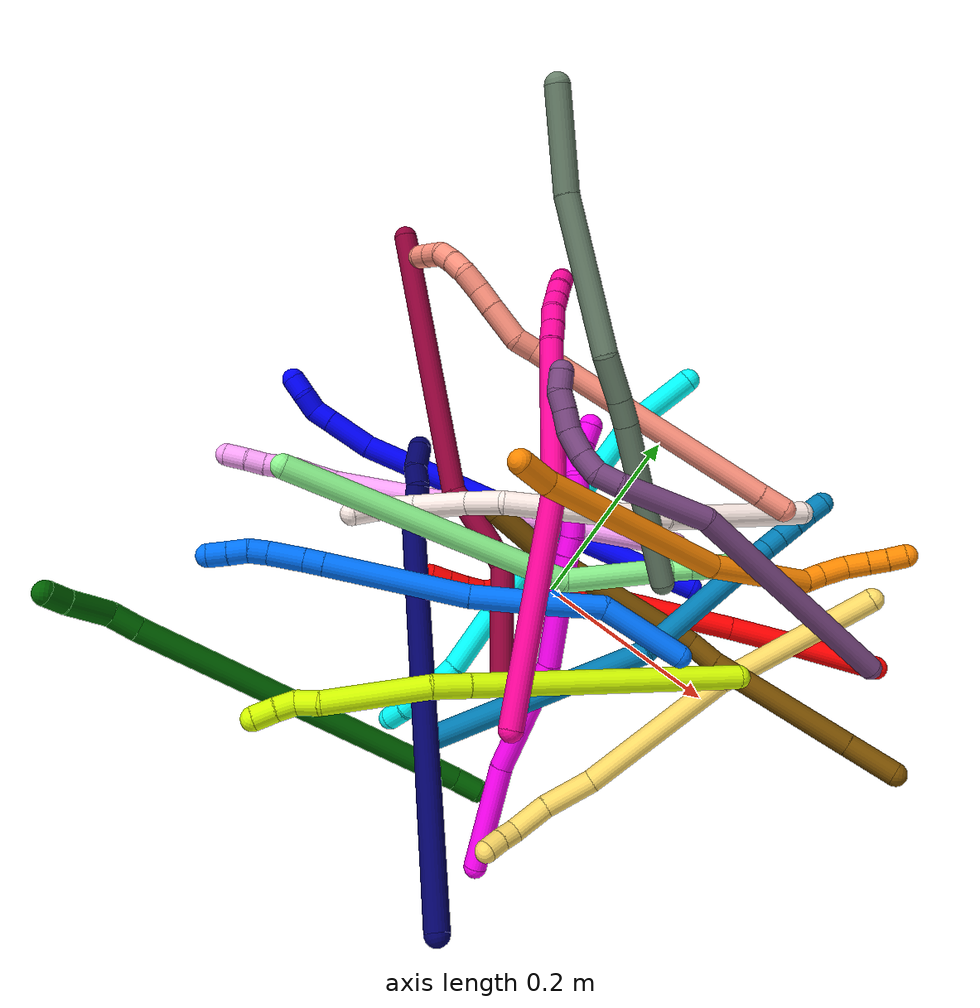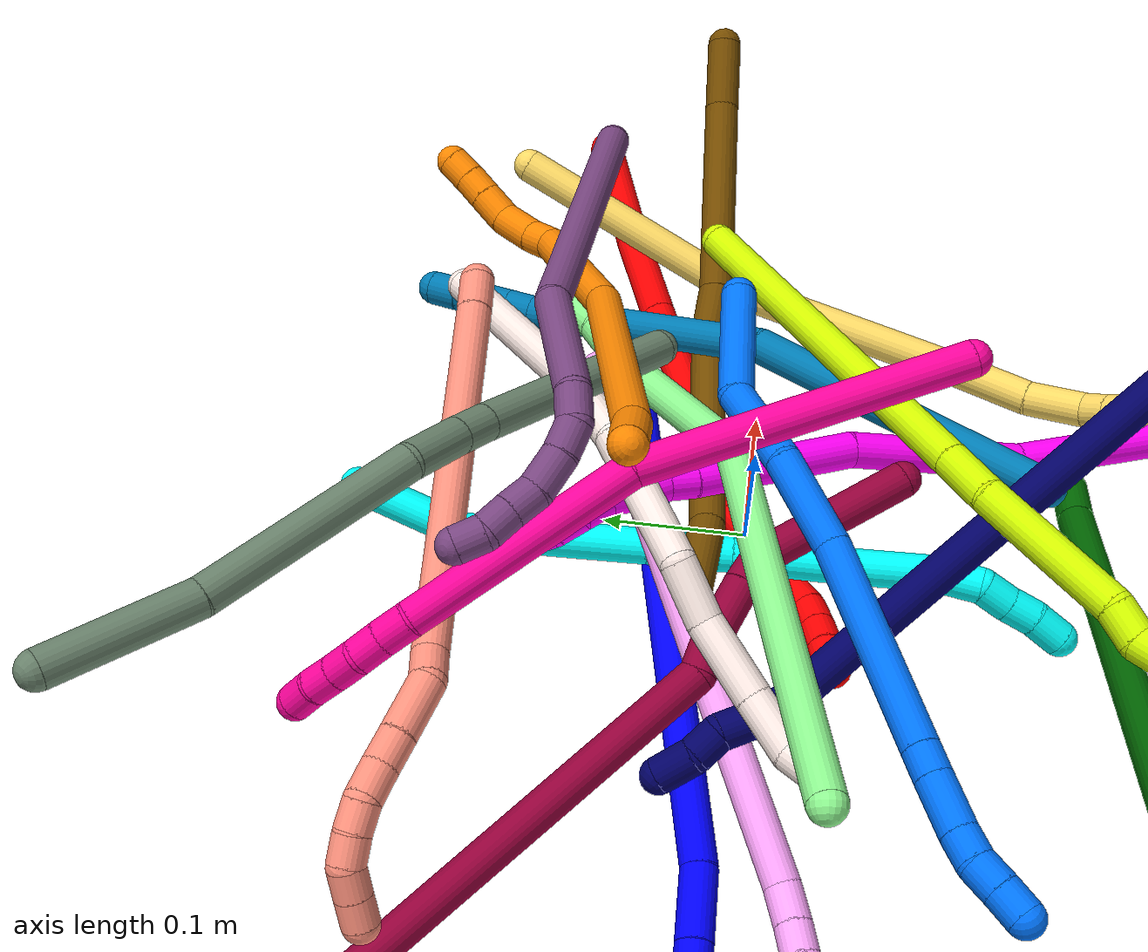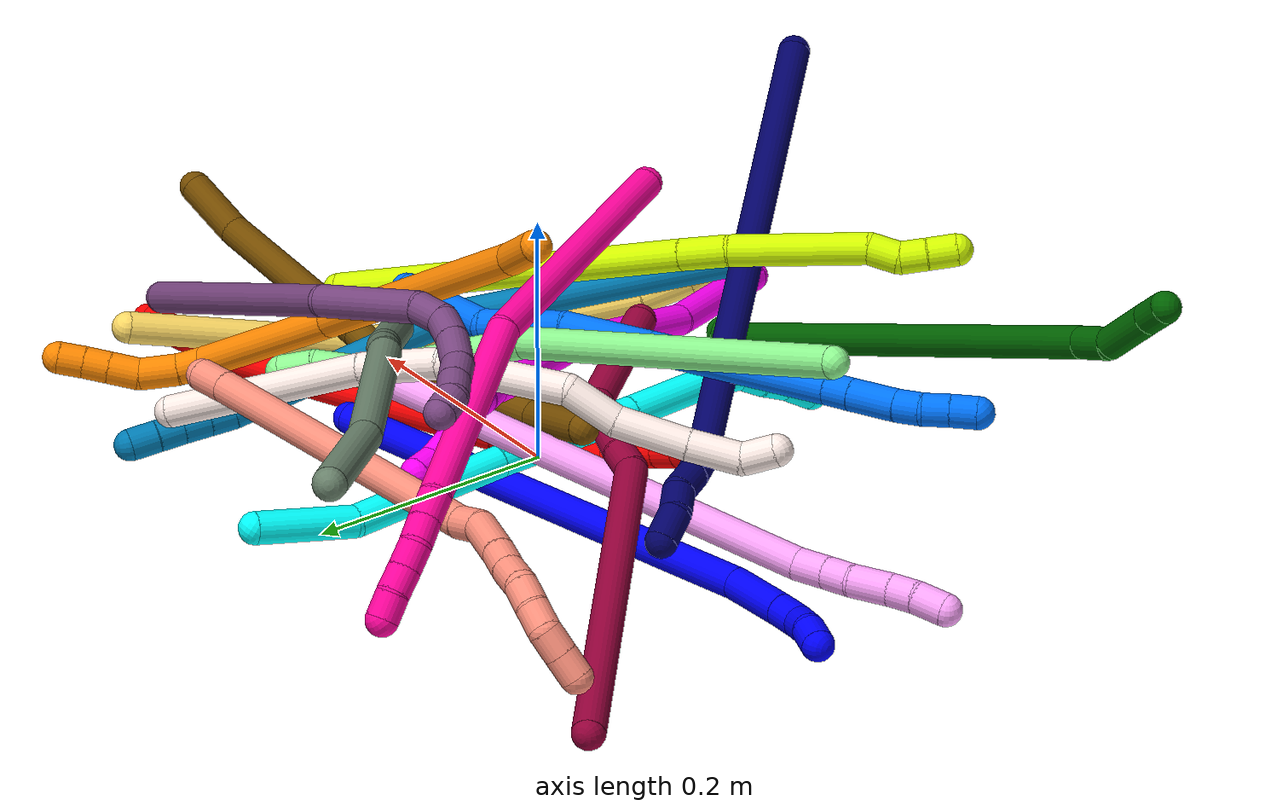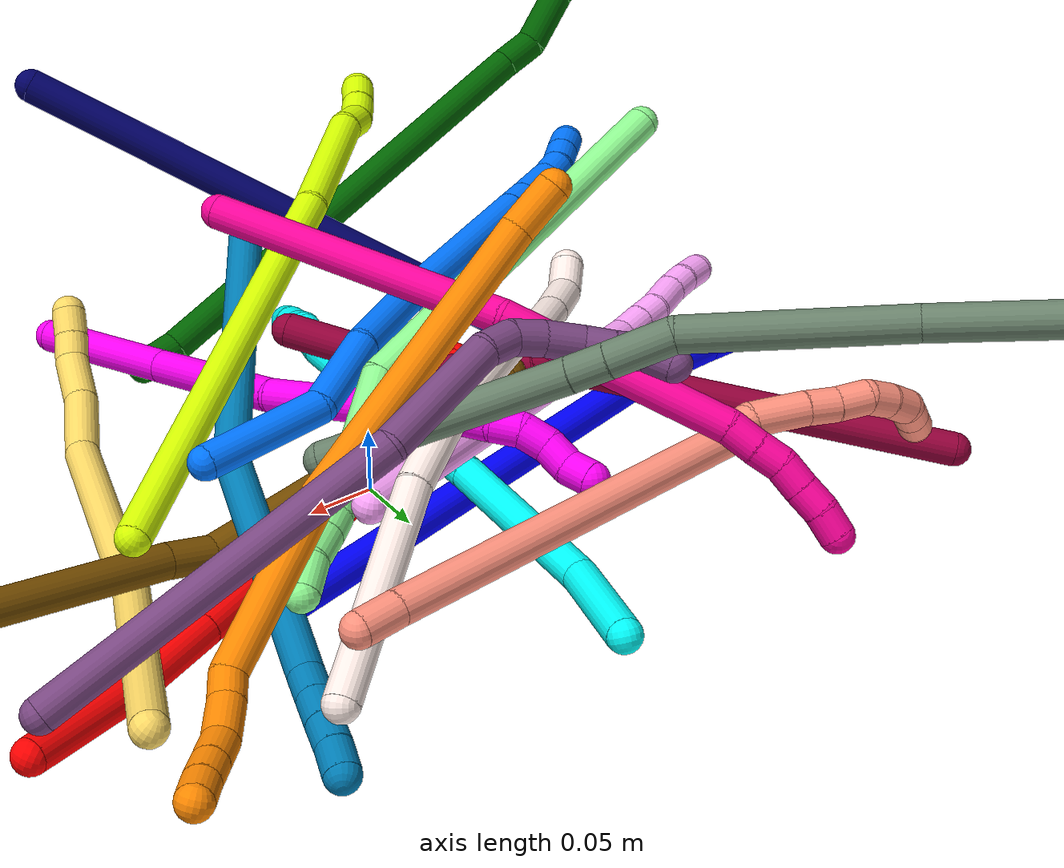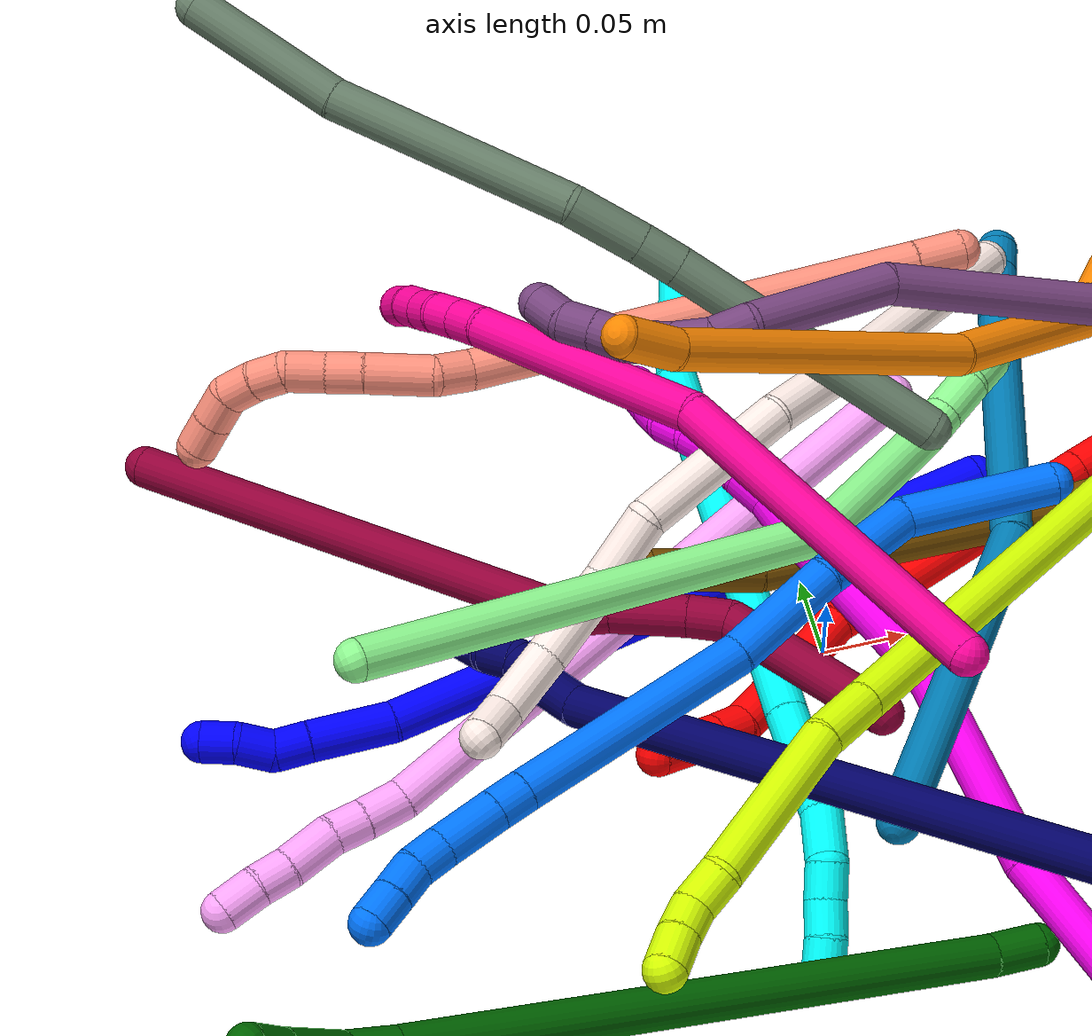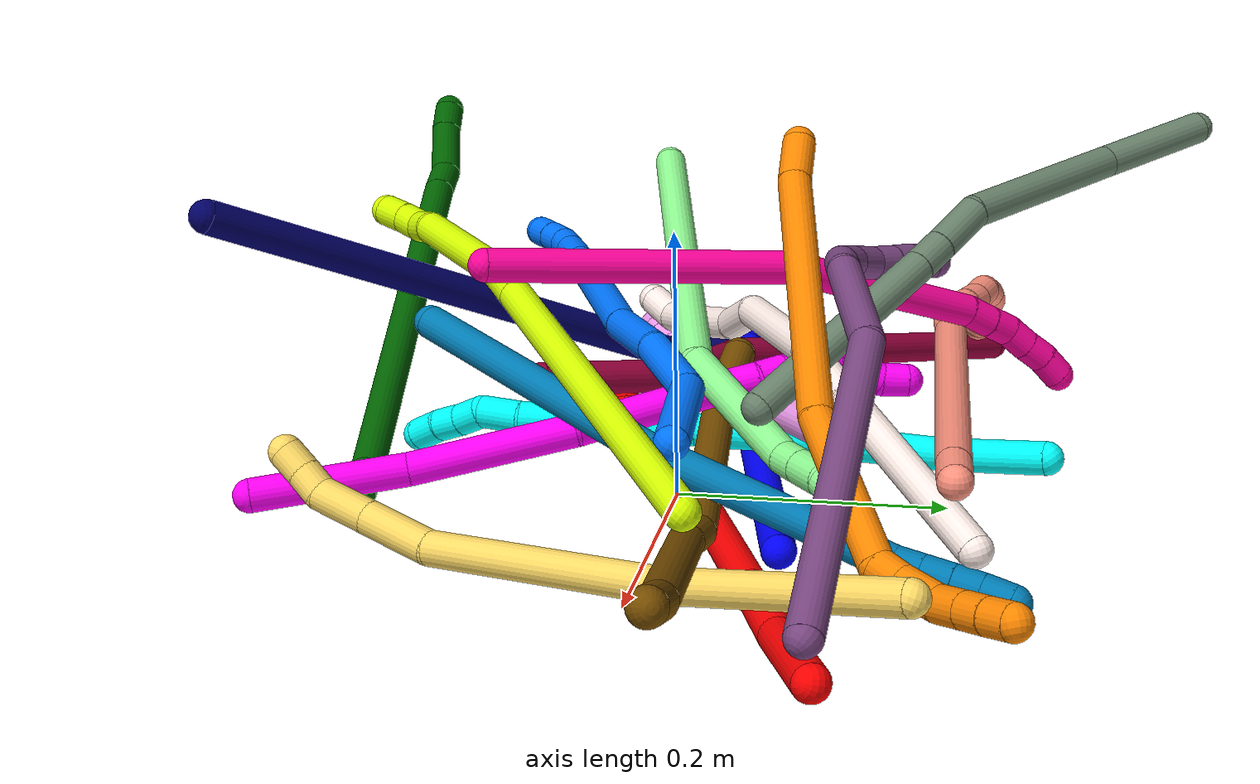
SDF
<sdf version="1.7">
 <world name="default">
  <plugin name="TubeGeneratorPlugin" filename="libtube_generator_plugin.so"/>
  <model name="photoneo_s_sensor">
   <static>1</static>
   <pose>0 0 2 1.57079 1.57079 3.14159</pose>
   <link name="link">
    <inertial><mass>0.1</mass></inertial>
    <sensor name="sensor" type="depth">
     <update_rate>30</update_rate>
     <camera>
      <horizontal_fov>1.22</horizontal_fov>
      <image><width>1920</width><height>1200</height><format>B8G8R8</format></image>
      <clip><near>0.1</near><far>4</far></clip>
      <depth_camera><output>points</output></depth_camera>
     </camera>
     <plugin name="camera_plugin" filename="libgazebo_ros_depth_camera.so">
      <baseline>0.2</baseline>
      <alwaysOn>1</alwaysOn>
      <updateRate>0.0</updateRate>
      <cameraName>camera_ir</cameraName>
      <imageTopicName>/camera/color/image_raw</imageTopicName>
      <cameraInfoTopicName>/camera/color/camera_info</cameraInfoTopicName>
      <depthImageTopicName>/camera/depth/image_raw</depthImageTopicName>
      <depthImageCameraInfoTopicName>/camera/depth/camera_info</depthImageCameraInfoTopicName>
      <pointCloudTopicName>/camera/depth/points</pointCloudTopicName>
      <frameName>fr_optical</frameName>
      <pointCloudCutoff>0.1</pointCloudCutoff>
      <pointCloudCutoffMax>2.0</pointCloudCutoffMax>
      <distortionK1>0</distortionK1>
      <distortionK2>0</distortionK2>
      <distortionK3>0</distortionK3>
      <distortionT1>0</distortionT1>
      <distortionT2>0</distortionT2>
      <CxPrime>0</CxPrime>
      <Cx>0</Cx>
      <Cy>0</Cy>
      <focalLength>0</focalLength>
      <hackBaseline>0</hackBaseline>
     </plugin>
    </sensor>
   </link>
  </model>
  <gravity>0 0 -9.8</gravity>
  <magnetic_field>6e-06 2.3e-05 -4.2e-05</magnetic_field>
  <atmosphere type="adiabatic"/>
  <physics name="default_physics" default="0" type="ode">
   <max_step_size>0.003</max_step_size>
   <real_time_factor>1</real_time_factor>
   <real_time_update_rate>1000</real_time_update_rate>
   <max_contacts>10000</max_contacts>
   <ode>
    <solver>
     <type>quick</type>
     <iters>100</iters>
     <sor>1.3</sor>
     <use_dynamic_moi_rescaling>0</use_dynamic_moi_rescaling>
    </solver>
    <constraints>
     <contact_max_correcting_vel>0</contact_max_correcting_vel>
     <contact_surface_layer>0.001</contact_surface_layer>
     <cfm>0</cfm>
     <erp>0.2</erp>
    </constraints>
   </ode>
  </physics>
  <scene><ambient>0.4 0.4 0.4 1</ambient><background>0.7 0.7 0.7 1</background><shadows>0</shadows></scene>
  <audio><device>default</device></audio>
  <spherical_coordinates>
   <surface_model>EARTH_WGS84</surface_model>
   <latitude_deg>0</latitude_deg>
   <longitude_deg>0</longitude_deg>
   <elevation>0</elevation>
   <heading_deg>0</heading_deg>
  </spherical_coordinates>
  <model name="bin">
   <static>1</static>
   <link name="bottom">
    <collision name="collision-bottom">
     <pose>0 0 -0.01 0 -0 0</pose>
     <geometry><box><size>0.8 0.6 0.02</size></box></geometry>
     <surface>
      <friction><ode><mu>100</mu><mu2>100</mu2></ode></friction>
      <contact><collide_bitmask>65535</collide_bitmask></contact>
     </surface>
    </collision>
   </link>
   <link name="west_wall">
    <collision name="collision-west_wall">
     <pose>-0.41 0 0.1 0 -0 0</pose>
     <geometry><box><size>0.02 0.6 0.2</size></box></geometry>
     <surface>
      <friction><ode><mu>100</mu><mu2>100</mu2></ode></friction>
      <contact><collide_bitmask>65535</collide_bitmask></contact>
     </surface>
    </collision>
   </link>
   <link name="east_wall">
    <collision name="collision-east_wall">
     <pose>0.41 0 0.1 0 -0 0</pose>
     <geometry><box><size>0.02 0.6 0.2</size></box></geometry>
     <surface>
      <friction><ode><mu>100</mu><mu2>100</mu2></ode></friction>
      <contact><collide_bitmask>65535</collide_bitmask></contact>
     </surface>
    </collision>
   </link>
   <link name="south_wall">
    <collision name="collision-south_wall">
     <pose>0 -0.31 0.1 0 -0 0</pose>
     <geometry><box><size>0.8 0.02 0.2</size></box></geometry>
     <surface>
      <friction><ode><mu>100</mu><mu2>100</mu2></ode></friction>
      <contact><collide_bitmask>65535</collide_bitmask></contact>
     </surface>
    </collision>
   </link>
   <link name="north_wall">
    <collision name="collision-north_wall">
     <pose>0 0.31 0.1 0 -0 0</pose>
     <geometry><box><size>0.8 0.02 0.2</size></box></geometry>
     <surface>
      <friction><ode><mu>100</mu><mu2>100</mu2></ode></friction>
      <contact><collide_bitmask>65535</collide_bitmask></contact>
     </surface>
    </collision>
   </link>
  </model>
  <model name="1">
   <static>0</static>
   <link name="1">
    <collision name="collision-cylinder-e_1_1_4">
     <pose>-0.014626 -0.003808 0.1927 0.019758 -0.075741 -0.000749</pose>
     <geometry><cylinder><radius>0.0125</radius><length>0.386584</length></cylinder></geometry>
     <surface>
      <friction><ode><mu>1.16</mu><mu2>1.16</mu2><slip1>0</slip1><slip2>0</slip2></ode></friction>
      <contact><ode><kp>1e+06</kp><kd>1</kd><max_vel>0</max_vel><min_depth>0.001</min_depth></ode></contact>
     </surface>
    </collision>
    <visual name="visual-cylinder-e_1_1_4">
     <pose>-0.014626 -0.003808 0.1927 0.019758 -0.075741 -0.000749</pose>
     <geometry><cylinder><radius>0.0125</radius><length>0.386584</length></cylinder></geometry>
     <material><ambient>0 0 1 1</ambient></material>
    </visual>
    <collision name="collision-cylinder-e_2_4_5">
     <pose>-0.027464 -0.005279 0.410327 -0.093455 0.071302 -0.003336</pose>
     <geometry><cylinder><radius>0.0125</radius><length>0.0502</length></cylinder></geometry>
     <surface>
      <friction><ode><mu>1.16</mu><mu2>1.16</mu2><slip1>0</slip1><slip2>0</slip2></ode></friction>
      <contact><ode><kp>1e+06</kp><kd>1</kd><max_vel>0</max_vel><min_depth>0.001</min_depth></ode></contact>
     </surface>
    </collision>
    <visual name="visual-cylinder-e_2_4_5">
     <pose>-0.027464 -0.005279 0.410327 -0.093455 0.071302 -0.003336</pose>
     <geometry><cylinder><radius>0.0125</radius><length>0.0502</length></cylinder></geometry>
     <material><ambient>0 0 1 1</ambient></material>
    </visual>
    <collision name="collision-cylinder-e_3_5_6">
     <pose>-0.025376 -0.001631 0.445723 -0.124664 0.028454 -0.001776</pose>
     <geometry><cylinder><radius>0.0125</radius><length>0.02111</length></cylinder></geometry>
     <surface>
      <friction><ode><mu>1.16</mu><mu2>1.16</mu2><slip1>0</slip1><slip2>0</slip2></ode></friction>
      <contact><ode><kp>1e+06</kp><kd>1</kd><max_vel>0</max_vel><min_depth>0.001</min_depth></ode></contact>
     </surface>
    </collision>
    <visual name="visual-cylinder-e_3_5_6">
     <pose>-0.025376 -0.001631 0.445723 -0.124664 0.028454 -0.001776</pose>
     <geometry><cylinder><radius>0.0125</radius><length>0.02111</length></cylinder></geometry>
     <material><ambient>0 0 1 1</ambient></material>
    </visual>
    <collision name="collision-cylinder-e_4_6_7">
     <pose>-0.019667 0.001277 0.465626 -0.167641 0.514419 -0.044192</pose>
     <geometry><cylinder><radius>0.0125</radius><length>0.021984</length></cylinder></geometry>
     <surface>
      <friction><ode><mu>1.16</mu><mu2>1.16</mu2><slip1>0</slip1><slip2>0</slip2></ode></friction>
      <contact><ode><kp>1e+06</kp><kd>1</kd><max_vel>0</max_vel><min_depth>0.001</min_depth></ode></contact>
     </surface>
    </collision>
    <visual name="visual-cylinder-e_4_6_7">
     <pose>-0.019667 0.001277 0.465626 -0.167641 0.514419 -0.044192</pose>
     <geometry><cylinder><radius>0.0125</radius><length>0.021984</length></cylinder></geometry>
     <material><ambient>0 0 1 1</ambient></material>
    </visual>
    <collision name="collision-cylinder-e_5_7_2">
     <pose>-0.011548 0.006767 0.483935 -0.413401 0.272726 -0.057531</pose>
     <geometry><cylinder><radius>0.0125</radius><length>0.020123</length></cylinder></geometry>
     <surface>
      <friction><ode><mu>1.16</mu><mu2>1.16</mu2><slip1>0</slip1><slip2>0</slip2></ode></friction>
      <contact><ode><kp>1e+06</kp><kd>1</kd><max_vel>0</max_vel><min_depth>0.001</min_depth></ode></contact>
     </surface>
    </collision>
    <visual name="visual-cylinder-e_5_7_2">
     <pose>-0.011548 0.006767 0.483935 -0.413401 0.272726 -0.057531</pose>
     <geometry><cylinder><radius>0.0125</radius><length>0.020123</length></cylinder></geometry>
     <material><ambient>0 0 1 1</ambient></material>
    </visual>
    <collision name="collision-sphere-2">
     <pose>-0.008838 0.010659 0.492808 0 -0 0</pose>
     <geometry><sphere><radius>0.0125</radius></sphere></geometry>
     <surface>
      <friction><ode><mu>1.16</mu><mu2>1.16</mu2><slip1>0</slip1><slip2>0</slip2></ode></friction>
      <contact><ode><kp>1e+06</kp><kd>1</kd><max_vel>0</max_vel><min_depth>0.001</min_depth></ode></contact>
     </surface>
    </collision>
    <visual name="visual-sphere-2">
     <pose>-0.008838 0.010659 0.492808 0 -0 0</pose>
     <geometry><sphere><radius>0.0125</radius></sphere></geometry>
     <material><ambient>0 0 1 1</ambient></material>
    </visual>
    <collision name="collision-sphere-7">
     <pose>-0.014259 0.002874 0.475062 0 -0 0</pose>
     <geometry><sphere><radius>0.0125</radius></sphere></geometry>
     <surface>
      <friction><ode><mu>1.16</mu><mu2>1.16</mu2><slip1>0</slip1><slip2>0</slip2></ode></friction>
      <contact><ode><kp>1e+06</kp><kd>1</kd><max_vel>0</max_vel><min_depth>0.001</min_depth></ode></contact>
     </surface>
    </collision>
    <visual name="visual-sphere-7">
     <pose>-0.014259 0.002874 0.475062 0 -0 0</pose>
     <geometry><sphere><radius>0.0125</radius></sphere></geometry>
     <material><ambient>0 0 1 1</ambient></material>
    </visual>
    <collision name="collision-sphere-6">
     <pose>-0.025075 -0.000319 0.456191 0 -0 0</pose>
     <geometry><sphere><radius>0.0125</radius></sphere></geometry>
     <surface>
      <friction><ode><mu>1.16</mu><mu2>1.16</mu2><slip1>0</slip1><slip2>0</slip2></ode></friction>
      <contact><ode><kp>1e+06</kp><kd>1</kd><max_vel>0</max_vel><min_depth>0.001</min_depth></ode></contact>
     </surface>
    </collision>
    <visual name="visual-sphere-6">
     <pose>-0.025075 -0.000319 0.456191 0 -0 0</pose>
     <geometry><sphere><radius>0.0125</radius></sphere></geometry>
     <material><ambient>0 0 1 1</ambient></material>
    </visual>
    <collision name="collision-sphere-5">
     <pose>-0.025676 -0.002943 0.435254 0 -0 0</pose>
     <geometry><sphere><radius>0.0125</radius></sphere></geometry>
     <surface>
      <friction><ode><mu>1.16</mu><mu2>1.16</mu2><slip1>0</slip1><slip2>0</slip2></ode></friction>
      <contact><ode><kp>1e+06</kp><kd>1</kd><max_vel>0</max_vel><min_depth>0.001</min_depth></ode></contact>
     </surface>
    </collision>
    <visual name="visual-sphere-5">
     <pose>-0.025676 -0.002943 0.435254 0 -0 0</pose>
     <geometry><sphere><radius>0.0125</radius></sphere></geometry>
     <material><ambient>0 0 1 1</ambient></material>
    </visual>
    <collision name="collision-sphere-1">
     <geometry><sphere><radius>0.0125</radius></sphere></geometry>
     <surface>
      <friction><ode><mu>1.16</mu><mu2>1.16</mu2><slip1>0</slip1><slip2>0</slip2></ode></friction>
      <contact><ode><kp>1e+06</kp><kd>1</kd><max_vel>0</max_vel><min_depth>0.001</min_depth></ode></contact>
     </surface>
    </collision>
    <visual name="visual-sphere-1">
     <geometry><sphere><radius>0.0125</radius></sphere></geometry>
     <material><ambient>0 0 1 1</ambient></material>
    </visual>
    <collision name="collision-sphere-4">
     <pose>-0.029252 -0.007616 0.3854 0 -0 0</pose>
     <geometry><sphere><radius>0.0125</radius></sphere></geometry>
     <surface>
      <friction><ode><mu>1.16</mu><mu2>1.16</mu2><slip1>0</slip1><slip2>0</slip2></ode></friction>
      <contact><ode><kp>1e+06</kp><kd>1</kd><max_vel>0</max_vel><min_depth>0.001</min_depth></ode></contact>
     </surface>
    </collision>
    <visual name="visual-sphere-4">
     <pose>-0.029252 -0.007616 0.3854 0 -0 0</pose>
     <geometry><sphere><radius>0.0125</radius></sphere></geometry>
     <material><ambient>0 0 1 1</ambient></material>
    </visual>
    <inertial>
     <pose>-0.016467 -0.003214 0.248953 0 -0 0</pose>
     <mass>0.5</mass>
     <inertia>
      <ixx>0.004828</ixx>
      <ixy>0</ixy>
      <ixz>0</ixz>
      <iyy>0.004843</iyy>
      <iyz>0</iyz>
      <izz>0.000495</izz>
     </inertia>
    </inertial>
   </link>
   <pose>0.120354 0.092074 0.011491 -1.52139 -0.738833 1.68665</pose>
  </model>
  <model name="2">
   <static>0</static>
   <link name="2">
    <collision name="collision-cylinder-e_1_1_4">
     <pose>-0.034417 -0.021229 0.018139 0.863728 -0.889203 -0.432279</pose>
     <geometry><cylinder><radius>0.0125</radius><length>0.088639</length></cylinder></geometry>
     <surface>
      <friction><ode><mu>1.16</mu><mu2>1.16</mu2><slip1>0</slip1><slip2>0</slip2></ode></friction>
      <contact><ode><kp>1e+06</kp><kd>1</kd><max_vel>0</max_vel><min_depth>0.001</min_depth></ode></contact>
     </surface>
    </collision>
    <visual name="visual-cylinder-e_1_1_4">
     <pose>-0.034417 -0.021229 0.018139 0.863728 -0.889203 -0.432279</pose>
     <geometry><cylinder><radius>0.0125</radius><length>0.088639</length></cylinder></geometry>
     <material><ambient>1 0 0 1</ambient></material>
    </visual>
    <collision name="collision-cylinder-e_2_4_5">
     <pose>-0.095466 -0.06404 0.048982 1.03876 -0.816106 -0.484634</pose>
     <geometry><cylinder><radius>0.0125</radius><length>0.073114</length></cylinder></geometry>
     <surface>
      <friction><ode><mu>1.16</mu><mu2>1.16</mu2><slip1>0</slip1><slip2>0</slip2></ode></friction>
      <contact><ode><kp>1e+06</kp><kd>1</kd><max_vel>0</max_vel><min_depth>0.001</min_depth></ode></contact>
     </surface>
    </collision>
    <visual name="visual-cylinder-e_2_4_5">
     <pose>-0.095466 -0.06404 0.048982 1.03876 -0.816106 -0.484634</pose>
     <geometry><cylinder><radius>0.0125</radius><length>0.073114</length></cylinder></geometry>
     <material><ambient>1 0 0 1</ambient></material>
    </visual>
    <collision name="collision-cylinder-e_3_5_6">
     <pose>-0.182433 -0.133904 0.088757 1.0598 -0.828446 -0.504135</pose>
     <geometry><cylinder><radius>0.0125</radius><length>0.16376</length></cylinder></geometry>
     <surface>
      <friction><ode><mu>1.16</mu><mu2>1.16</mu2><slip1>0</slip1><slip2>0</slip2></ode></friction>
      <contact><ode><kp>1e+06</kp><kd>1</kd><max_vel>0</max_vel><min_depth>0.001</min_depth></ode></contact>
     </surface>
    </collision>
    <visual name="visual-cylinder-e_3_5_6">
     <pose>-0.182433 -0.133904 0.088757 1.0598 -0.828446 -0.504135</pose>
     <geometry><cylinder><radius>0.0125</radius><length>0.16376</length></cylinder></geometry>
     <material><ambient>1 0 0 1</ambient></material>
    </visual>
    <collision name="collision-cylinder-e_4_6_7">
     <pose>-0.250382 -0.188253 0.119227 1.06001 -0.830535 -0.505622</pose>
     <geometry><cylinder><radius>0.0125</radius><length>0.020625</length></cylinder></geometry>
     <surface>
      <friction><ode><mu>1.16</mu><mu2>1.16</mu2><slip1>0</slip1><slip2>0</slip2></ode></friction>
      <contact><ode><kp>1e+06</kp><kd>1</kd><max_vel>0</max_vel><min_depth>0.001</min_depth></ode></contact>
     </surface>
    </collision>
    <visual name="visual-cylinder-e_4_6_7">
     <pose>-0.250382 -0.188253 0.119227 1.06001 -0.830535 -0.505622</pose>
     <geometry><cylinder><radius>0.0125</radius><length>0.020625</length></cylinder></geometry>
     <material><ambient>1 0 0 1</ambient></material>
    </visual>
    <collision name="collision-cylinder-e_5_7_8">
     <pose>-0.273144 -0.20528 0.123243 1.51467 -0.94374 -0.899028</pose>
     <geometry><cylinder><radius>0.0125</radius><length>0.037413</length></cylinder></geometry>
     <surface>
      <friction><ode><mu>1.16</mu><mu2>1.16</mu2><slip1>0</slip1><slip2>0</slip2></ode></friction>
      <contact><ode><kp>1e+06</kp><kd>1</kd><max_vel>0</max_vel><min_depth>0.001</min_depth></ode></contact>
     </surface>
    </collision>
    <visual name="visual-cylinder-e_5_7_8">
     <pose>-0.273144 -0.20528 0.123243 1.51467 -0.94374 -0.899028</pose>
     <geometry><cylinder><radius>0.0125</radius><length>0.037413</length></cylinder></geometry>
     <material><ambient>1 0 0 1</ambient></material>
    </visual>
    <collision name="collision-cylinder-e_6_8_9">
     <pose>-0.301272 -0.223167 0.126574 1.19727 -1.05029 -0.752788</pose>
     <geometry><cylinder><radius>0.0125</radius><length>0.029922</length></cylinder></geometry>
     <surface>
      <friction><ode><mu>1.16</mu><mu2>1.16</mu2><slip1>0</slip1><slip2>0</slip2></ode></friction>
      <contact><ode><kp>1e+06</kp><kd>1</kd><max_vel>0</max_vel><min_depth>0.001</min_depth></ode></contact>
     </surface>
    </collision>
    <visual name="visual-cylinder-e_6_8_9">
     <pose>-0.301272 -0.223167 0.126574 1.19727 -1.05029 -0.752788</pose>
     <geometry><cylinder><radius>0.0125</radius><length>0.029922</length></cylinder></geometry>
     <material><ambient>1 0 0 1</ambient></material>
    </visual>
    <collision name="collision-cylinder-e_7_9_10">
     <pose>-0.323887 -0.238626 0.129174 1.58425 -0.846059 -0.856174</pose>
     <geometry><cylinder><radius>0.0125</radius><length>0.025741</length></cylinder></geometry>
     <surface>
      <friction><ode><mu>1.16</mu><mu2>1.16</mu2><slip1>0</slip1><slip2>0</slip2></ode></friction>
      <contact><ode><kp>1e+06</kp><kd>1</kd><max_vel>0</max_vel><min_depth>0.001</min_depth></ode></contact>
     </surface>
    </collision>
    <visual name="visual-cylinder-e_7_9_10">
     <pose>-0.323887 -0.238626 0.129174 1.58425 -0.846059 -0.856174</pose>
     <geometry><cylinder><radius>0.0125</radius><length>0.025741</length></cylinder></geometry>
     <material><ambient>1 0 0 1</ambient></material>
    </visual>
    <collision name="collision-cylinder-e_8_10_11">
     <pose>-0.339179 -0.255248 0.131413 1.2877 -0.591191 -0.449387</pose>
     <geometry><cylinder><radius>0.0125</radius><length>0.020297</length></cylinder></geometry>
     <surface>
      <friction><ode><mu>1.16</mu><mu2>1.16</mu2><slip1>0</slip1><slip2>0</slip2></ode></friction>
      <contact><ode><kp>1e+06</kp><kd>1</kd><max_vel>0</max_vel><min_depth>0.001</min_depth></ode></contact>
     </surface>
    </collision>
    <visual name="visual-cylinder-e_8_10_11">
     <pose>-0.339179 -0.255248 0.131413 1.2877 -0.591191 -0.449387</pose>
     <geometry><cylinder><radius>0.0125</radius><length>0.020297</length></cylinder></geometry>
     <material><ambient>1 0 0 1</ambient></material>
    </visual>
    <collision name="collision-cylinder-e_9_11_12">
     <pose>-0.350062 -0.271512 0.136502 1.24793 -0.545094 -0.39713</pose>
     <geometry><cylinder><radius>0.0125</radius><length>0.020161</length></cylinder></geometry>
     <surface>
      <friction><ode><mu>1.16</mu><mu2>1.16</mu2><slip1>0</slip1><slip2>0</slip2></ode></friction>
      <contact><ode><kp>1e+06</kp><kd>1</kd><max_vel>0</max_vel><min_depth>0.001</min_depth></ode></contact>
     </surface>
    </collision>
    <visual name="visual-cylinder-e_9_11_12">
     <pose>-0.350062 -0.271512 0.136502 1.24793 -0.545094 -0.39713</pose>
     <geometry><cylinder><radius>0.0125</radius><length>0.020161</length></cylinder></geometry>
     <material><ambient>1 0 0 1</ambient></material>
    </visual>
    <collision name="collision-cylinder-e_10_12_2">
     <pose>-0.360792 -0.287573 0.142527 1.17549 -0.572186 -0.387092</pose>
     <geometry><cylinder><radius>0.0125</radius><length>0.020328</length></cylinder></geometry>
     <surface>
      <friction><ode><mu>1.16</mu><mu2>1.16</mu2><slip1>0</slip1><slip2>0</slip2></ode></friction>
      <contact><ode><kp>1e+06</kp><kd>1</kd><max_vel>0</max_vel><min_depth>0.001</min_depth></ode></contact>
     </surface>
    </collision>
    <visual name="visual-cylinder-e_10_12_2">
     <pose>-0.360792 -0.287573 0.142527 1.17549 -0.572186 -0.387092</pose>
     <geometry><cylinder><radius>0.0125</radius><length>0.020328</length></cylinder></geometry>
     <material><ambient>1 0 0 1</ambient></material>
    </visual>
    <collision name="collision-sphere-2">
     <pose>-0.366296 -0.295458 0.145818 0 -0 0</pose>
     <geometry><sphere><radius>0.0125</radius></sphere></geometry>
     <surface>
      <friction><ode><mu>1.16</mu><mu2>1.16</mu2><slip1>0</slip1><slip2>0</slip2></ode></friction>
      <contact><ode><kp>1e+06</kp><kd>1</kd><max_vel>0</max_vel><min_depth>0.001</min_depth></ode></contact>
     </surface>
    </collision>
    <visual name="visual-sphere-2">
     <pose>-0.366296 -0.295458 0.145818 0 -0 0</pose>
     <geometry><sphere><radius>0.0125</radius></sphere></geometry>
     <material><ambient>1 0 0 1</ambient></material>
    </visual>
    <collision name="collision-sphere-12">
     <pose>-0.355289 -0.279687 0.139236 0 -0 0</pose>
     <geometry><sphere><radius>0.0125</radius></sphere></geometry>
     <surface>
      <friction><ode><mu>1.16</mu><mu2>1.16</mu2><slip1>0</slip1><slip2>0</slip2></ode></friction>
      <contact><ode><kp>1e+06</kp><kd>1</kd><max_vel>0</max_vel><min_depth>0.001</min_depth></ode></contact>
     </surface>
    </collision>
    <visual name="visual-sphere-12">
     <pose>-0.355289 -0.279687 0.139236 0 -0 0</pose>
     <geometry><sphere><radius>0.0125</radius></sphere></geometry>
     <material><ambient>1 0 0 1</ambient></material>
    </visual>
    <collision name="collision-sphere-11">
     <pose>-0.344835 -0.263338 0.133767 0 -0 0</pose>
     <geometry><sphere><radius>0.0125</radius></sphere></geometry>
     <surface>
      <friction><ode><mu>1.16</mu><mu2>1.16</mu2><slip1>0</slip1><slip2>0</slip2></ode></friction>
      <contact><ode><kp>1e+06</kp><kd>1</kd><max_vel>0</max_vel><min_depth>0.001</min_depth></ode></contact>
     </surface>
    </collision>
    <visual name="visual-sphere-11">
     <pose>-0.344835 -0.263338 0.133767 0 -0 0</pose>
     <geometry><sphere><radius>0.0125</radius></sphere></geometry>
     <material><ambient>1 0 0 1</ambient></material>
    </visual>
    <collision name="collision-sphere-10">
     <pose>-0.333523 -0.247157 0.129059 0 -0 0</pose>
     <geometry><sphere><radius>0.0125</radius></sphere></geometry>
     <surface>
      <friction><ode><mu>1.16</mu><mu2>1.16</mu2><slip1>0</slip1><slip2>0</slip2></ode></friction>
      <contact><ode><kp>1e+06</kp><kd>1</kd><max_vel>0</max_vel><min_depth>0.001</min_depth></ode></contact>
     </surface>
    </collision>
    <visual name="visual-sphere-10">
     <pose>-0.333523 -0.247157 0.129059 0 -0 0</pose>
     <geometry><sphere><radius>0.0125</radius></sphere></geometry>
     <material><ambient>1 0 0 1</ambient></material>
    </visual>
    <collision name="collision-sphere-9">
     <pose>-0.314251 -0.230094 0.129289 0 -0 0</pose>
     <geometry><sphere><radius>0.0125</radius></sphere></geometry>
     <surface>
      <friction><ode><mu>1.16</mu><mu2>1.16</mu2><slip1>0</slip1><slip2>0</slip2></ode></friction>
      <contact><ode><kp>1e+06</kp><kd>1</kd><max_vel>0</max_vel><min_depth>0.001</min_depth></ode></contact>
     </surface>
    </collision>
    <visual name="visual-sphere-9">
     <pose>-0.314251 -0.230094 0.129289 0 -0 0</pose>
     <geometry><sphere><radius>0.0125</radius></sphere></geometry>
     <material><ambient>1 0 0 1</ambient></material>
    </visual>
    <collision name="collision-sphere-4">
     <pose>-0.068835 -0.042458 0.036278 0 -0 0</pose>
     <geometry><sphere><radius>0.0125</radius></sphere></geometry>
     <surface>
      <friction><ode><mu>1.16</mu><mu2>1.16</mu2><slip1>0</slip1><slip2>0</slip2></ode></friction>
      <contact><ode><kp>1e+06</kp><kd>1</kd><max_vel>0</max_vel><min_depth>0.001</min_depth></ode></contact>
     </surface>
    </collision>
    <visual name="visual-sphere-4">
     <pose>-0.068835 -0.042458 0.036278 0 -0 0</pose>
     <geometry><sphere><radius>0.0125</radius></sphere></geometry>
     <material><ambient>1 0 0 1</ambient></material>
    </visual>
    <collision name="collision-sphere-1">
     <geometry><sphere><radius>0.0125</radius></sphere></geometry>
     <surface>
      <friction><ode><mu>1.16</mu><mu2>1.16</mu2><slip1>0</slip1><slip2>0</slip2></ode></friction>
      <contact><ode><kp>1e+06</kp><kd>1</kd><max_vel>0</max_vel><min_depth>0.001</min_depth></ode></contact>
     </surface>
    </collision>
    <visual name="visual-sphere-1">
     <geometry><sphere><radius>0.0125</radius></sphere></geometry>
     <material><ambient>1 0 0 1</ambient></material>
    </visual>
    <collision name="collision-sphere-8">
     <pose>-0.288292 -0.216239 0.123859 0 -0 0</pose>
     <geometry><sphere><radius>0.0125</radius></sphere></geometry>
     <surface>
      <friction><ode><mu>1.16</mu><mu2>1.16</mu2><slip1>0</slip1><slip2>0</slip2></ode></friction>
      <contact><ode><kp>1e+06</kp><kd>1</kd><max_vel>0</max_vel><min_depth>0.001</min_depth></ode></contact>
     </surface>
    </collision>
    <visual name="visual-sphere-8">
     <pose>-0.288292 -0.216239 0.123859 0 -0 0</pose>
     <geometry><sphere><radius>0.0125</radius></sphere></geometry>
     <material><ambient>1 0 0 1</ambient></material>
    </visual>
    <collision name="collision-sphere-5">
     <pose>-0.122097 -0.085622 0.061687 0 -0 0</pose>
     <geometry><sphere><radius>0.0125</radius></sphere></geometry>
     <surface>
      <friction><ode><mu>1.16</mu><mu2>1.16</mu2><slip1>0</slip1><slip2>0</slip2></ode></friction>
      <contact><ode><kp>1e+06</kp><kd>1</kd><max_vel>0</max_vel><min_depth>0.001</min_depth></ode></contact>
     </surface>
    </collision>
    <visual name="visual-sphere-5">
     <pose>-0.122097 -0.085622 0.061687 0 -0 0</pose>
     <geometry><sphere><radius>0.0125</radius></sphere></geometry>
     <material><ambient>1 0 0 1</ambient></material>
    </visual>
    <collision name="collision-sphere-6">
     <pose>-0.242769 -0.182185 0.115827 0 -0 0</pose>
     <geometry><sphere><radius>0.0125</radius></sphere></geometry>
     <surface>
      <friction><ode><mu>1.16</mu><mu2>1.16</mu2><slip1>0</slip1><slip2>0</slip2></ode></friction>
      <contact><ode><kp>1e+06</kp><kd>1</kd><max_vel>0</max_vel><min_depth>0.001</min_depth></ode></contact>
     </surface>
    </collision>
    <visual name="visual-sphere-6">
     <pose>-0.242769 -0.182185 0.115827 0 -0 0</pose>
     <geometry><sphere><radius>0.0125</radius></sphere></geometry>
     <material><ambient>1 0 0 1</ambient></material>
    </visual>
    <collision name="collision-sphere-7">
     <pose>-0.257996 -0.194321 0.122627 0 -0 0</pose>
     <geometry><sphere><radius>0.0125</radius></sphere></geometry>
     <surface>
      <friction><ode><mu>1.16</mu><mu2>1.16</mu2><slip1>0</slip1><slip2>0</slip2></ode></friction>
      <contact><ode><kp>1e+06</kp><kd>1</kd><max_vel>0</max_vel><min_depth>0.001</min_depth></ode></contact>
     </surface>
    </collision>
    <visual name="visual-sphere-7">
     <pose>-0.257996 -0.194321 0.122627 0 -0 0</pose>
     <geometry><sphere><radius>0.0125</radius></sphere></geometry>
     <material><ambient>1 0 0 1</ambient></material>
    </visual>
    <inertial>
     <pose>-0.187834 -0.138751 0.084446 0 -0 0</pose>
     <mass>0.5</mass>
     <inertia>
      <ixx>0.000101</ixx>
      <ixy>0</ixy>
      <ixz>0</ixz>
      <iyy>0.000185</iyy>
      <iyz>0</iyz>
      <izz>0.000653</izz>
     </inertia>
    </inertial>
   </link>
   <pose>0.33089 0.13871 0.023168 -1.99876 -0.490523 0.970247</pose>
  </model>
  <model name="3">
   <static>0</static>
   <link name="3">
    <collision name="collision-cylinder-e_1_1_4">
     <pose>-0.000351 -0.034444 0.018563 1.0765 -0.008983 -0.005363</pose>
     <geometry><cylinder><radius>0.0125</radius><length>0.078259</length></cylinder></geometry>
     <surface>
      <friction><ode><mu>1.16</mu><mu2>1.16</mu2><slip1>0</slip1><slip2>0</slip2></ode></friction>
      <contact><ode><kp>1e+06</kp><kd>1</kd><max_vel>0</max_vel><min_depth>0.001</min_depth></ode></contact>
     </surface>
    </collision>
    <visual name="visual-cylinder-e_1_1_4">
     <pose>-0.000351 -0.034444 0.018563 1.0765 -0.008983 -0.005363</pose>
     <geometry><cylinder><radius>0.0125</radius><length>0.078259</length></cylinder></geometry>
     <material><ambient>0.003922 1 0.996078 1</ambient></material>
    </visual>
    <collision name="collision-cylinder-e_2_4_5">
     <pose>0.016247 -0.117613 0.077042 0.884425 0.26288 0.125029</pose>
     <geometry><cylinder><radius>0.0125</radius><length>0.130456</length></cylinder></geometry>
     <surface>
      <friction><ode><mu>1.16</mu><mu2>1.16</mu2><slip1>0</slip1><slip2>0</slip2></ode></friction>
      <contact><ode><kp>1e+06</kp><kd>1</kd><max_vel>0</max_vel><min_depth>0.001</min_depth></ode></contact>
     </surface>
    </collision>
    <visual name="visual-cylinder-e_2_4_5">
     <pose>0.016247 -0.117613 0.077042 0.884425 0.26288 0.125029</pose>
     <geometry><cylinder><radius>0.0125</radius><length>0.130456</length></cylinder></geometry>
     <material><ambient>0.003922 1 0.996078 1</ambient></material>
    </visual>
    <collision name="collision-cylinder-e_3_5_6">
     <pose>0.040949 -0.188507 0.133796 0.921304 0.271547 0.135385</pose>
     <geometry><cylinder><radius>0.0125</radius><length>0.057796</length></cylinder></geometry>
     <surface>
      <friction><ode><mu>1.16</mu><mu2>1.16</mu2><slip1>0</slip1><slip2>0</slip2></ode></friction>
      <contact><ode><kp>1e+06</kp><kd>1</kd><max_vel>0</max_vel><min_depth>0.001</min_depth></ode></contact>
     </surface>
    </collision>
    <visual name="visual-cylinder-e_3_5_6">
     <pose>0.040949 -0.188507 0.133796 0.921304 0.271547 0.135385</pose>
     <geometry><cylinder><radius>0.0125</radius><length>0.057796</length></cylinder></geometry>
     <material><ambient>0.003922 1 0.996078 1</ambient></material>
    </visual>
    <collision name="collision-cylinder-e_4_6_7">
     <pose>0.057413 -0.235989 0.169707 0.924993 0.268297 0.134368</pose>
     <geometry><cylinder><radius>0.0125</radius><length>0.06574</length></cylinder></geometry>
     <surface>
      <friction><ode><mu>1.16</mu><mu2>1.16</mu2><slip1>0</slip1><slip2>0</slip2></ode></friction>
      <contact><ode><kp>1e+06</kp><kd>1</kd><max_vel>0</max_vel><min_depth>0.001</min_depth></ode></contact>
     </surface>
    </collision>
    <visual name="visual-cylinder-e_4_6_7">
     <pose>0.057413 -0.235989 0.169707 0.924993 0.268297 0.134368</pose>
     <geometry><cylinder><radius>0.0125</radius><length>0.06574</length></cylinder></geometry>
     <material><ambient>0.003922 1 0.996078 1</ambient></material>
    </visual>
    <collision name="collision-cylinder-e_5_7_8">
     <pose>0.075996 -0.287848 0.209049 0.918751 0.287319 0.142871</pose>
     <geometry><cylinder><radius>0.0125</radius><length>0.069654</length></cylinder></geometry>
     <surface>
      <friction><ode><mu>1.16</mu><mu2>1.16</mu2><slip1>0</slip1><slip2>0</slip2></ode></friction>
      <contact><ode><kp>1e+06</kp><kd>1</kd><max_vel>0</max_vel><min_depth>0.001</min_depth></ode></contact>
     </surface>
    </collision>
    <visual name="visual-cylinder-e_5_7_8">
     <pose>0.075996 -0.287848 0.209049 0.918751 0.287319 0.142871</pose>
     <geometry><cylinder><radius>0.0125</radius><length>0.069654</length></cylinder></geometry>
     <material><ambient>0.003922 1 0.996078 1</ambient></material>
    </visual>
    <collision name="collision-cylinder-e_6_8_9">
     <pose>0.087256 -0.327242 0.239061 0.921843 0.086026 0.04274</pose>
     <geometry><cylinder><radius>0.0125</radius><length>0.032368</length></cylinder></geometry>
     <surface>
      <friction><ode><mu>1.16</mu><mu2>1.16</mu2><slip1>0</slip1><slip2>0</slip2></ode></friction>
      <contact><ode><kp>1e+06</kp><kd>1</kd><max_vel>0</max_vel><min_depth>0.001</min_depth></ode></contact>
     </surface>
    </collision>
    <visual name="visual-cylinder-e_6_8_9">
     <pose>0.087256 -0.327242 0.239061 0.921843 0.086026 0.04274</pose>
     <geometry><cylinder><radius>0.0125</radius><length>0.032368</length></cylinder></geometry>
     <material><ambient>0.003922 1 0.996078 1</ambient></material>
    </visual>
    <collision name="collision-cylinder-e_7_9_10">
     <pose>0.088554 -0.350749 0.250482 1.41484 -0.008558 -0.007318</pose>
     <geometry><cylinder><radius>0.0125</radius><length>0.021584</length></cylinder></geometry>
     <surface>
      <friction><ode><mu>1.16</mu><mu2>1.16</mu2><slip1>0</slip1><slip2>0</slip2></ode></friction>
      <contact><ode><kp>1e+06</kp><kd>1</kd><max_vel>0</max_vel><min_depth>0.001</min_depth></ode></contact>
     </surface>
    </collision>
    <visual name="visual-cylinder-e_7_9_10">
     <pose>0.088554 -0.350749 0.250482 1.41484 -0.008558 -0.007318</pose>
     <geometry><cylinder><radius>0.0125</radius><length>0.021584</length></cylinder></geometry>
     <material><ambient>0.003922 1 0.996078 1</ambient></material>
    </visual>
    <collision name="collision-cylinder-e_8_10_11">
     <pose>0.088896 -0.371485 0.254842 1.31049 0.041644 0.032006</pose>
     <geometry><cylinder><radius>0.0125</radius><length>0.020872</length></cylinder></geometry>
     <surface>
      <friction><ode><mu>1.16</mu><mu2>1.16</mu2><slip1>0</slip1><slip2>0</slip2></ode></friction>
      <contact><ode><kp>1e+06</kp><kd>1</kd><max_vel>0</max_vel><min_depth>0.001</min_depth></ode></contact>
     </surface>
    </collision>
    <visual name="visual-cylinder-e_8_10_11">
     <pose>0.088896 -0.371485 0.254842 1.31049 0.041644 0.032006</pose>
     <geometry><cylinder><radius>0.0125</radius><length>0.020872</length></cylinder></geometry>
     <material><ambient>0.003922 1 0.996078 1</ambient></material>
    </visual>
    <collision name="collision-cylinder-e_9_11_2">
     <pose>0.088657 -0.393095 0.258895 1.45261 -0.057933 -0.051464</pose>
     <geometry><cylinder><radius>0.0125</radius><length>0.023271</length></cylinder></geometry>
     <surface>
      <friction><ode><mu>1.16</mu><mu2>1.16</mu2><slip1>0</slip1><slip2>0</slip2></ode></friction>
      <contact><ode><kp>1e+06</kp><kd>1</kd><max_vel>0</max_vel><min_depth>0.001</min_depth></ode></contact>
     </surface>
    </collision>
    <visual name="visual-cylinder-e_9_11_2">
     <pose>0.088657 -0.393095 0.258895 1.45261 -0.057933 -0.051464</pose>
     <geometry><cylinder><radius>0.0125</radius><length>0.023271</length></cylinder></geometry>
     <material><ambient>0.003922 1 0.996078 1</ambient></material>
    </visual>
    <collision name="collision-sphere-2">
     <pose>0.087983 -0.404631 0.260265 0 -0 0</pose>
     <geometry><sphere><radius>0.0125</radius></sphere></geometry>
     <surface>
      <friction><ode><mu>1.16</mu><mu2>1.16</mu2><slip1>0</slip1><slip2>0</slip2></ode></friction>
      <contact><ode><kp>1e+06</kp><kd>1</kd><max_vel>0</max_vel><min_depth>0.001</min_depth></ode></contact>
     </surface>
    </collision>
    <visual name="visual-sphere-2">
     <pose>0.087983 -0.404631 0.260265 0 -0 0</pose>
     <geometry><sphere><radius>0.0125</radius></sphere></geometry>
     <material><ambient>0.003922 1 0.996078 1</ambient></material>
    </visual>
    <collision name="collision-sphere-11">
     <pose>0.089331 -0.38156 0.257526 0 -0 0</pose>
     <geometry><sphere><radius>0.0125</radius></sphere></geometry>
     <surface>
      <friction><ode><mu>1.16</mu><mu2>1.16</mu2><slip1>0</slip1><slip2>0</slip2></ode></friction>
      <contact><ode><kp>1e+06</kp><kd>1</kd><max_vel>0</max_vel><min_depth>0.001</min_depth></ode></contact>
     </surface>
    </collision>
    <visual name="visual-sphere-11">
     <pose>0.089331 -0.38156 0.257526 0 -0 0</pose>
     <geometry><sphere><radius>0.0125</radius></sphere></geometry>
     <material><ambient>0.003922 1 0.996078 1</ambient></material>
    </visual>
    <collision name="collision-sphere-10">
     <pose>0.088462 -0.361409 0.252158 0 -0 0</pose>
     <geometry><sphere><radius>0.0125</radius></sphere></geometry>
     <surface>
      <friction><ode><mu>1.16</mu><mu2>1.16</mu2><slip1>0</slip1><slip2>0</slip2></ode></friction>
      <contact><ode><kp>1e+06</kp><kd>1</kd><max_vel>0</max_vel><min_depth>0.001</min_depth></ode></contact>
     </surface>
    </collision>
    <visual name="visual-sphere-10">
     <pose>0.088462 -0.361409 0.252158 0 -0 0</pose>
     <geometry><sphere><radius>0.0125</radius></sphere></geometry>
     <material><ambient>0.003922 1 0.996078 1</ambient></material>
    </visual>
    <collision name="collision-sphere-9">
     <pose>0.088647 -0.340088 0.248806 0 -0 0</pose>
     <geometry><sphere><radius>0.0125</radius></sphere></geometry>
     <surface>
      <friction><ode><mu>1.16</mu><mu2>1.16</mu2><slip1>0</slip1><slip2>0</slip2></ode></friction>
      <contact><ode><kp>1e+06</kp><kd>1</kd><max_vel>0</max_vel><min_depth>0.001</min_depth></ode></contact>
     </surface>
    </collision>
    <visual name="visual-sphere-9">
     <pose>0.088647 -0.340088 0.248806 0 -0 0</pose>
     <geometry><sphere><radius>0.0125</radius></sphere></geometry>
     <material><ambient>0.003922 1 0.996078 1</ambient></material>
    </visual>
    <collision name="collision-sphere-4">
     <pose>-0.000703 -0.068889 0.037125 0 -0 0</pose>
     <geometry><sphere><radius>0.0125</radius></sphere></geometry>
     <surface>
      <friction><ode><mu>1.16</mu><mu2>1.16</mu2><slip1>0</slip1><slip2>0</slip2></ode></friction>
      <contact><ode><kp>1e+06</kp><kd>1</kd><max_vel>0</max_vel><min_depth>0.001</min_depth></ode></contact>
     </surface>
    </collision>
    <visual name="visual-sphere-4">
     <pose>-0.000703 -0.068889 0.037125 0 -0 0</pose>
     <geometry><sphere><radius>0.0125</radius></sphere></geometry>
     <material><ambient>0.003922 1 0.996078 1</ambient></material>
    </visual>
    <collision name="collision-sphere-1">
     <geometry><sphere><radius>0.0125</radius></sphere></geometry>
     <surface>
      <friction><ode><mu>1.16</mu><mu2>1.16</mu2><slip1>0</slip1><slip2>0</slip2></ode></friction>
      <contact><ode><kp>1e+06</kp><kd>1</kd><max_vel>0</max_vel><min_depth>0.001</min_depth></ode></contact>
     </surface>
    </collision>
    <visual name="visual-sphere-1">
     <geometry><sphere><radius>0.0125</radius></sphere></geometry>
     <material><ambient>0.003922 1 0.996078 1</ambient></material>
    </visual>
    <collision name="collision-sphere-8">
     <pose>0.085866 -0.314396 0.229317 0 -0 0</pose>
     <geometry><sphere><radius>0.0125</radius></sphere></geometry>
     <surface>
      <friction><ode><mu>1.16</mu><mu2>1.16</mu2><slip1>0</slip1><slip2>0</slip2></ode></friction>
      <contact><ode><kp>1e+06</kp><kd>1</kd><max_vel>0</max_vel><min_depth>0.001</min_depth></ode></contact>
     </surface>
    </collision>
    <visual name="visual-sphere-8">
     <pose>0.085866 -0.314396 0.229317 0 -0 0</pose>
     <geometry><sphere><radius>0.0125</radius></sphere></geometry>
     <material><ambient>0.003922 1 0.996078 1</ambient></material>
    </visual>
    <collision name="collision-sphere-5">
     <pose>0.033198 -0.166336 0.11696 0 -0 0</pose>
     <geometry><sphere><radius>0.0125</radius></sphere></geometry>
     <surface>
      <friction><ode><mu>1.16</mu><mu2>1.16</mu2><slip1>0</slip1><slip2>0</slip2></ode></friction>
      <contact><ode><kp>1e+06</kp><kd>1</kd><max_vel>0</max_vel><min_depth>0.001</min_depth></ode></contact>
     </surface>
    </collision>
    <visual name="visual-sphere-5">
     <pose>0.033198 -0.166336 0.11696 0 -0 0</pose>
     <geometry><sphere><radius>0.0125</radius></sphere></geometry>
     <material><ambient>0.003922 1 0.996078 1</ambient></material>
    </visual>
    <collision name="collision-sphere-6">
     <pose>0.0487 -0.210678 0.150633 0 -0 0</pose>
     <geometry><sphere><radius>0.0125</radius></sphere></geometry>
     <surface>
      <friction><ode><mu>1.16</mu><mu2>1.16</mu2><slip1>0</slip1><slip2>0</slip2></ode></friction>
      <contact><ode><kp>1e+06</kp><kd>1</kd><max_vel>0</max_vel><min_depth>0.001</min_depth></ode></contact>
     </surface>
    </collision>
    <visual name="visual-sphere-6">
     <pose>0.0487 -0.210678 0.150633 0 -0 0</pose>
     <geometry><sphere><radius>0.0125</radius></sphere></geometry>
     <material><ambient>0.003922 1 0.996078 1</ambient></material>
    </visual>
    <collision name="collision-sphere-7">
     <pose>0.066127 -0.261301 0.188782 0 -0 0</pose>
     <geometry><sphere><radius>0.0125</radius></sphere></geometry>
     <surface>
      <friction><ode><mu>1.16</mu><mu2>1.16</mu2><slip1>0</slip1><slip2>0</slip2></ode></friction>
      <contact><ode><kp>1e+06</kp><kd>1</kd><max_vel>0</max_vel><min_depth>0.001</min_depth></ode></contact>
     </surface>
    </collision>
    <visual name="visual-sphere-7">
     <pose>0.066127 -0.261301 0.188782 0 -0 0</pose>
     <geometry><sphere><radius>0.0125</radius></sphere></geometry>
     <material><ambient>0.003922 1 0.996078 1</ambient></material>
    </visual>
    <inertial>
     <pose>0.044362 -0.199123 0.138884 0 -0 0</pose>
     <mass>0.5</mass>
     <inertia>
      <ixx>0.000346</ixx>
      <ixy>0</ixy>
      <ixz>0</ixz>
      <iyy>0.000197</iyy>
      <iyz>0</iyz>
      <izz>0.000196</izz>
     </inertia>
    </inertial>
   </link>
   <pose>-0.016737 0.270159 0.036966 0.616482 0.031678 -0.271851</pose>
  </model>
  <model name="4">
   <static>0</static>
   <link name="4">
    <collision name="collision-cylinder-e_1_1_4">
     <pose>-0.155553 -0.105173 -0.004821 1.6166 -0.975791 -1.01422</pose>
     <geometry><cylinder><radius>0.0125</radius><length>0.375667</length></cylinder></geometry>
     <surface>
      <friction><ode><mu>1.16</mu><mu2>1.16</mu2><slip1>0</slip1><slip2>0</slip2></ode></friction>
      <contact><ode><kp>1e+06</kp><kd>1</kd><max_vel>0</max_vel><min_depth>0.001</min_depth></ode></contact>
     </surface>
    </collision>
    <visual name="visual-cylinder-e_1_1_4">
     <pose>-0.155553 -0.105173 -0.004821 1.6166 -0.975791 -1.01422</pose>
     <geometry><cylinder><radius>0.0125</radius><length>0.375667</length></cylinder></geometry>
     <material><ambient>1 0.65098 0.996078 1</ambient></material>
    </visual>
    <collision name="collision-cylinder-e_2_4_5">
     <pose>-0.322325 -0.216629 -0.006997 1.1725 -1.02473 -0.715012</pose>
     <geometry><cylinder><radius>0.0125</radius><length>0.026255</length></cylinder></geometry>
     <surface>
      <friction><ode><mu>1.16</mu><mu2>1.16</mu2><slip1>0</slip1><slip2>0</slip2></ode></friction>
      <contact><ode><kp>1e+06</kp><kd>1</kd><max_vel>0</max_vel><min_depth>0.001</min_depth></ode></contact>
     </surface>
    </collision>
    <visual name="visual-cylinder-e_2_4_5">
     <pose>-0.322325 -0.216629 -0.006997 1.1725 -1.02473 -0.715012</pose>
     <geometry><cylinder><radius>0.0125</radius><length>0.026255</length></cylinder></geometry>
     <material><ambient>1 0.65098 0.996078 1</ambient></material>
    </visual>
    <collision name="collision-cylinder-e_3_5_6">
     <pose>-0.342813 -0.227583 -0.001947 1.09504 -1.05521 -0.682732</pose>
     <geometry><cylinder><radius>0.0125</radius><length>0.021309</length></cylinder></geometry>
     <surface>
      <friction><ode><mu>1.16</mu><mu2>1.16</mu2><slip1>0</slip1><slip2>0</slip2></ode></friction>
      <contact><ode><kp>1e+06</kp><kd>1</kd><max_vel>0</max_vel><min_depth>0.001</min_depth></ode></contact>
     </surface>
    </collision>
    <visual name="visual-cylinder-e_3_5_6">
     <pose>-0.342813 -0.227583 -0.001947 1.09504 -1.05521 -0.682732</pose>
     <geometry><cylinder><radius>0.0125</radius><length>0.021309</length></cylinder></geometry>
     <material><ambient>1 0.65098 0.996078 1</ambient></material>
    </visual>
    <collision name="collision-cylinder-e_4_6_7">
     <pose>-0.364407 -0.242014 0.002811 1.33436 -0.887146 -0.716253</pose>
     <geometry><cylinder><radius>0.0125</radius><length>0.031793</length></cylinder></geometry>
     <surface>
      <friction><ode><mu>1.16</mu><mu2>1.16</mu2><slip1>0</slip1><slip2>0</slip2></ode></friction>
      <contact><ode><kp>1e+06</kp><kd>1</kd><max_vel>0</max_vel><min_depth>0.001</min_depth></ode></contact>
     </surface>
    </collision>
    <visual name="visual-cylinder-e_4_6_7">
     <pose>-0.364407 -0.242014 0.002811 1.33436 -0.887146 -0.716253</pose>
     <geometry><cylinder><radius>0.0125</radius><length>0.031793</length></cylinder></geometry>
     <material><ambient>1 0.65098 0.996078 1</ambient></material>
    </visual>
    <collision name="collision-cylinder-e_5_7_8">
     <pose>-0.385465 -0.25706 0.007032 1.2308 -1.00018 -0.737303</pose>
     <geometry><cylinder><radius>0.0125</radius><length>0.020757</length></cylinder></geometry>
     <surface>
      <friction><ode><mu>1.16</mu><mu2>1.16</mu2><slip1>0</slip1><slip2>0</slip2></ode></friction>
      <contact><ode><kp>1e+06</kp><kd>1</kd><max_vel>0</max_vel><min_depth>0.001</min_depth></ode></contact>
     </surface>
    </collision>
    <visual name="visual-cylinder-e_5_7_8">
     <pose>-0.385465 -0.25706 0.007032 1.2308 -1.00018 -0.737303</pose>
     <geometry><cylinder><radius>0.0125</radius><length>0.020757</length></cylinder></geometry>
     <material><ambient>1 0.65098 0.996078 1</ambient></material>
    </visual>
    <collision name="collision-cylinder-e_6_8_2">
     <pose>-0.404485 -0.268728 0.009226 1.51998 -1.0148 -0.9722</pose>
     <geometry><cylinder><radius>0.0125</radius><length>0.024219</length></cylinder></geometry>
     <surface>
      <friction><ode><mu>1.16</mu><mu2>1.16</mu2><slip1>0</slip1><slip2>0</slip2></ode></friction>
      <contact><ode><kp>1e+06</kp><kd>1</kd><max_vel>0</max_vel><min_depth>0.001</min_depth></ode></contact>
     </surface>
    </collision>
    <visual name="visual-cylinder-e_6_8_2">
     <pose>-0.404485 -0.268728 0.009226 1.51998 -1.0148 -0.9722</pose>
     <geometry><cylinder><radius>0.0125</radius><length>0.024219</length></cylinder></geometry>
     <material><ambient>1 0.65098 0.996078 1</ambient></material>
    </visual>
    <collision name="collision-sphere-2">
     <pose>-0.41477 -0.275111 0.009551 0 -0 0</pose>
     <geometry><sphere><radius>0.0125</radius></sphere></geometry>
     <surface>
      <friction><ode><mu>1.16</mu><mu2>1.16</mu2><slip1>0</slip1><slip2>0</slip2></ode></friction>
      <contact><ode><kp>1e+06</kp><kd>1</kd><max_vel>0</max_vel><min_depth>0.001</min_depth></ode></contact>
     </surface>
    </collision>
    <visual name="visual-sphere-2">
     <pose>-0.41477 -0.275111 0.009551 0 -0 0</pose>
     <geometry><sphere><radius>0.0125</radius></sphere></geometry>
     <material><ambient>1 0.65098 0.996078 1</ambient></material>
    </visual>
    <collision name="collision-sphere-4">
     <pose>-0.311107 -0.210345 -0.009641 0 -0 0</pose>
     <geometry><sphere><radius>0.0125</radius></sphere></geometry>
     <surface>
      <friction><ode><mu>1.16</mu><mu2>1.16</mu2><slip1>0</slip1><slip2>0</slip2></ode></friction>
      <contact><ode><kp>1e+06</kp><kd>1</kd><max_vel>0</max_vel><min_depth>0.001</min_depth></ode></contact>
     </surface>
    </collision>
    <visual name="visual-sphere-4">
     <pose>-0.311107 -0.210345 -0.009641 0 -0 0</pose>
     <geometry><sphere><radius>0.0125</radius></sphere></geometry>
     <material><ambient>1 0.65098 0.996078 1</ambient></material>
    </visual>
    <collision name="collision-sphere-1">
     <geometry><sphere><radius>0.0125</radius></sphere></geometry>
     <surface>
      <friction><ode><mu>1.16</mu><mu2>1.16</mu2><slip1>0</slip1><slip2>0</slip2></ode></friction>
      <contact><ode><kp>1e+06</kp><kd>1</kd><max_vel>0</max_vel><min_depth>0.001</min_depth></ode></contact>
     </surface>
    </collision>
    <visual name="visual-sphere-1">
     <geometry><sphere><radius>0.0125</radius></sphere></geometry>
     <material><ambient>1 0.65098 0.996078 1</ambient></material>
    </visual>
    <collision name="collision-sphere-8">
     <pose>-0.3942 -0.262345 0.008902 0 -0 0</pose>
     <geometry><sphere><radius>0.0125</radius></sphere></geometry>
     <surface>
      <friction><ode><mu>1.16</mu><mu2>1.16</mu2><slip1>0</slip1><slip2>0</slip2></ode></friction>
      <contact><ode><kp>1e+06</kp><kd>1</kd><max_vel>0</max_vel><min_depth>0.001</min_depth></ode></contact>
     </surface>
    </collision>
    <visual name="visual-sphere-8">
     <pose>-0.3942 -0.262345 0.008902 0 -0 0</pose>
     <geometry><sphere><radius>0.0125</radius></sphere></geometry>
     <material><ambient>1 0.65098 0.996078 1</ambient></material>
    </visual>
    <collision name="collision-sphere-5">
     <pose>-0.333544 -0.222913 -0.004353 0 -0 0</pose>
     <geometry><sphere><radius>0.0125</radius></sphere></geometry>
     <surface>
      <friction><ode><mu>1.16</mu><mu2>1.16</mu2><slip1>0</slip1><slip2>0</slip2></ode></friction>
      <contact><ode><kp>1e+06</kp><kd>1</kd><max_vel>0</max_vel><min_depth>0.001</min_depth></ode></contact>
     </surface>
    </collision>
    <visual name="visual-sphere-5">
     <pose>-0.333544 -0.222913 -0.004353 0 -0 0</pose>
     <geometry><sphere><radius>0.0125</radius></sphere></geometry>
     <material><ambient>1 0.65098 0.996078 1</ambient></material>
    </visual>
    <collision name="collision-sphere-6">
     <pose>-0.352083 -0.232252 0.000459 0 -0 0</pose>
     <geometry><sphere><radius>0.0125</radius></sphere></geometry>
     <surface>
      <friction><ode><mu>1.16</mu><mu2>1.16</mu2><slip1>0</slip1><slip2>0</slip2></ode></friction>
      <contact><ode><kp>1e+06</kp><kd>1</kd><max_vel>0</max_vel><min_depth>0.001</min_depth></ode></contact>
     </surface>
    </collision>
    <visual name="visual-sphere-6">
     <pose>-0.352083 -0.232252 0.000459 0 -0 0</pose>
     <geometry><sphere><radius>0.0125</radius></sphere></geometry>
     <material><ambient>1 0.65098 0.996078 1</ambient></material>
    </visual>
    <collision name="collision-sphere-7">
     <pose>-0.376731 -0.251775 0.005163 0 -0 0</pose>
     <geometry><sphere><radius>0.0125</radius></sphere></geometry>
     <surface>
      <friction><ode><mu>1.16</mu><mu2>1.16</mu2><slip1>0</slip1><slip2>0</slip2></ode></friction>
      <contact><ode><kp>1e+06</kp><kd>1</kd><max_vel>0</max_vel><min_depth>0.001</min_depth></ode></contact>
     </surface>
    </collision>
    <visual name="visual-sphere-7">
     <pose>-0.376731 -0.251775 0.005163 0 -0 0</pose>
     <geometry><sphere><radius>0.0125</radius></sphere></geometry>
     <material><ambient>1 0.65098 0.996078 1</ambient></material>
    </visual>
    <inertial>
     <pose>-0.207174 -0.139171 -0.003155 0 -0 0</pose>
     <mass>0.5</mass>
     <inertia>
      <ixx>-0.000829</ixx>
      <ixy>0</ixy>
      <ixz>0</ixz>
      <iyy>0.00088</iyy>
      <iyz>0</iyz>
      <izz>0.00617</izz>
     </inertia>
    </inertial>
   </link>
   <pose>0.070466 0.113282 0.082748 -0.018467 -0.207807 -0.165407</pose>
  </model>
  <model name="5">
   <static>0</static>
   <link name="5">
    <collision name="collision-cylinder-e_1_1_4">
     <pose>-0.018793 -0.0859 0.023698 1.30161 -0.207853 -0.158515</pose>
     <geometry><cylinder><radius>0.0125</radius><length>0.182138</length></cylinder></geometry>
     <surface>
      <friction><ode><mu>1.16</mu><mu2>1.16</mu2><slip1>0</slip1><slip2>0</slip2></ode></friction>
      <contact><ode><kp>1e+06</kp><kd>1</kd><max_vel>0</max_vel><min_depth>0.001</min_depth></ode></contact>
     </surface>
    </collision>
    <visual name="visual-cylinder-e_1_1_4">
     <pose>-0.018793 -0.0859 0.023698 1.30161 -0.207853 -0.158515</pose>
     <geometry><cylinder><radius>0.0125</radius><length>0.182138</length></cylinder></geometry>
     <material><ambient>1 0.858824 0.4 1</ambient></material>
    </visual>
    <collision name="collision-cylinder-e_2_4_5">
     <pose>-0.07235 -0.251766 0.064221 1.36342 -0.402234 -0.327912</pose>
     <geometry><cylinder><radius>0.0125</radius><length>0.177608</length></cylinder></geometry>
     <surface>
      <friction><ode><mu>1.16</mu><mu2>1.16</mu2><slip1>0</slip1><slip2>0</slip2></ode></friction>
      <contact><ode><kp>1e+06</kp><kd>1</kd><max_vel>0</max_vel><min_depth>0.001</min_depth></ode></contact>
     </surface>
    </collision>
    <visual name="visual-cylinder-e_2_4_5">
     <pose>-0.07235 -0.251766 0.064221 1.36342 -0.402234 -0.327912</pose>
     <geometry><cylinder><radius>0.0125</radius><length>0.177608</length></cylinder></geometry>
     <material><ambient>1 0.858824 0.4 1</ambient></material>
    </visual>
    <collision name="collision-cylinder-e_3_5_6">
     <pose>-0.116819 -0.35861 0.07929 1.63602 -0.345792 -0.368604</pose>
     <geometry><cylinder><radius>0.0125</radius><length>0.057262</length></cylinder></geometry>
     <surface>
      <friction><ode><mu>1.16</mu><mu2>1.16</mu2><slip1>0</slip1><slip2>0</slip2></ode></friction>
      <contact><ode><kp>1e+06</kp><kd>1</kd><max_vel>0</max_vel><min_depth>0.001</min_depth></ode></contact>
     </surface>
    </collision>
    <visual name="visual-cylinder-e_3_5_6">
     <pose>-0.116819 -0.35861 0.07929 1.63602 -0.345792 -0.368604</pose>
     <geometry><cylinder><radius>0.0125</radius><length>0.057262</length></cylinder></geometry>
     <material><ambient>1 0.858824 0.4 1</ambient></material>
    </visual>
    <collision name="collision-cylinder-e_4_6_7">
     <pose>-0.137017 -0.403827 0.075852 1.6623 -0.517974 -0.56518</pose>
     <geometry><cylinder><radius>0.0125</radius><length>0.042389</length></cylinder></geometry>
     <surface>
      <friction><ode><mu>1.16</mu><mu2>1.16</mu2><slip1>0</slip1><slip2>0</slip2></ode></friction>
      <contact><ode><kp>1e+06</kp><kd>1</kd><max_vel>0</max_vel><min_depth>0.001</min_depth></ode></contact>
     </surface>
    </collision>
    <visual name="visual-cylinder-e_4_6_7">
     <pose>-0.137017 -0.403827 0.075852 1.6623 -0.517974 -0.56518</pose>
     <geometry><cylinder><radius>0.0125</radius><length>0.042389</length></cylinder></geometry>
     <material><ambient>1 0.858824 0.4 1</ambient></material>
    </visual>
    <collision name="collision-cylinder-e_5_7_8">
     <pose>-0.152433 -0.429723 0.069662 2.10852 -0.50985 -0.860321</pose>
     <geometry><cylinder><radius>0.0125</radius><length>0.020167</length></cylinder></geometry>
     <surface>
      <friction><ode><mu>1.16</mu><mu2>1.16</mu2><slip1>0</slip1><slip2>0</slip2></ode></friction>
      <contact><ode><kp>1e+06</kp><kd>1</kd><max_vel>0</max_vel><min_depth>0.001</min_depth></ode></contact>
     </surface>
    </collision>
    <visual name="visual-cylinder-e_5_7_8">
     <pose>-0.152433 -0.429723 0.069662 2.10852 -0.50985 -0.860321</pose>
     <geometry><cylinder><radius>0.0125</radius><length>0.020167</length></cylinder></geometry>
     <material><ambient>1 0.858824 0.4 1</ambient></material>
    </visual>
    <collision name="collision-cylinder-e_6_8_2">
     <pose>-0.163019 -0.444512 0.060678 2.12515 -0.587723 -0.995349</pose>
     <geometry><cylinder><radius>0.0125</radius><length>0.020436</length></cylinder></geometry>
     <surface>
      <friction><ode><mu>1.16</mu><mu2>1.16</mu2><slip1>0</slip1><slip2>0</slip2></ode></friction>
      <contact><ode><kp>1e+06</kp><kd>1</kd><max_vel>0</max_vel><min_depth>0.001</min_depth></ode></contact>
     </surface>
    </collision>
    <visual name="visual-cylinder-e_6_8_2">
     <pose>-0.163019 -0.444512 0.060678 2.12515 -0.587723 -0.995349</pose>
     <geometry><cylinder><radius>0.0125</radius><length>0.020436</length></cylinder></geometry>
     <material><ambient>1 0.858824 0.4 1</ambient></material>
    </visual>
    <collision name="collision-sphere-2">
     <pose>-0.168684 -0.451742 0.056202 0 -0 0</pose>
     <geometry><sphere><radius>0.0125</radius></sphere></geometry>
     <surface>
      <friction><ode><mu>1.16</mu><mu2>1.16</mu2><slip1>0</slip1><slip2>0</slip2></ode></friction>
      <contact><ode><kp>1e+06</kp><kd>1</kd><max_vel>0</max_vel><min_depth>0.001</min_depth></ode></contact>
     </surface>
    </collision>
    <visual name="visual-sphere-2">
     <pose>-0.168684 -0.451742 0.056202 0 -0 0</pose>
     <geometry><sphere><radius>0.0125</radius></sphere></geometry>
     <material><ambient>1 0.858824 0.4 1</ambient></material>
    </visual>
    <collision name="collision-sphere-4">
     <pose>-0.037586 -0.1718 0.047396 0 -0 0</pose>
     <geometry><sphere><radius>0.0125</radius></sphere></geometry>
     <surface>
      <friction><ode><mu>1.16</mu><mu2>1.16</mu2><slip1>0</slip1><slip2>0</slip2></ode></friction>
      <contact><ode><kp>1e+06</kp><kd>1</kd><max_vel>0</max_vel><min_depth>0.001</min_depth></ode></contact>
     </surface>
    </collision>
    <visual name="visual-sphere-4">
     <pose>-0.037586 -0.1718 0.047396 0 -0 0</pose>
     <geometry><sphere><radius>0.0125</radius></sphere></geometry>
     <material><ambient>1 0.858824 0.4 1</ambient></material>
    </visual>
    <collision name="collision-sphere-1">
     <geometry><sphere><radius>0.0125</radius></sphere></geometry>
     <surface>
      <friction><ode><mu>1.16</mu><mu2>1.16</mu2><slip1>0</slip1><slip2>0</slip2></ode></friction>
      <contact><ode><kp>1e+06</kp><kd>1</kd><max_vel>0</max_vel><min_depth>0.001</min_depth></ode></contact>
     </surface>
    </collision>
    <visual name="visual-sphere-1">
     <geometry><sphere><radius>0.0125</radius></sphere></geometry>
     <material><ambient>1 0.858824 0.4 1</ambient></material>
    </visual>
    <collision name="collision-sphere-8">
     <pose>-0.157354 -0.437282 0.065154 0 -0 0</pose>
     <geometry><sphere><radius>0.0125</radius></sphere></geometry>
     <surface>
      <friction><ode><mu>1.16</mu><mu2>1.16</mu2><slip1>0</slip1><slip2>0</slip2></ode></friction>
      <contact><ode><kp>1e+06</kp><kd>1</kd><max_vel>0</max_vel><min_depth>0.001</min_depth></ode></contact>
     </surface>
    </collision>
    <visual name="visual-sphere-8">
     <pose>-0.157354 -0.437282 0.065154 0 -0 0</pose>
     <geometry><sphere><radius>0.0125</radius></sphere></geometry>
     <material><ambient>1 0.858824 0.4 1</ambient></material>
    </visual>
    <collision name="collision-sphere-5">
     <pose>-0.107115 -0.331732 0.081046 0 -0 0</pose>
     <geometry><sphere><radius>0.0125</radius></sphere></geometry>
     <surface>
      <friction><ode><mu>1.16</mu><mu2>1.16</mu2><slip1>0</slip1><slip2>0</slip2></ode></friction>
      <contact><ode><kp>1e+06</kp><kd>1</kd><max_vel>0</max_vel><min_depth>0.001</min_depth></ode></contact>
     </surface>
    </collision>
    <visual name="visual-sphere-5">
     <pose>-0.107115 -0.331732 0.081046 0 -0 0</pose>
     <geometry><sphere><radius>0.0125</radius></sphere></geometry>
     <material><ambient>1 0.858824 0.4 1</ambient></material>
    </visual>
    <collision name="collision-sphere-6">
     <pose>-0.126523 -0.385489 0.077535 0 -0 0</pose>
     <geometry><sphere><radius>0.0125</radius></sphere></geometry>
     <surface>
      <friction><ode><mu>1.16</mu><mu2>1.16</mu2><slip1>0</slip1><slip2>0</slip2></ode></friction>
      <contact><ode><kp>1e+06</kp><kd>1</kd><max_vel>0</max_vel><min_depth>0.001</min_depth></ode></contact>
     </surface>
    </collision>
    <visual name="visual-sphere-6">
     <pose>-0.126523 -0.385489 0.077535 0 -0 0</pose>
     <geometry><sphere><radius>0.0125</radius></sphere></geometry>
     <material><ambient>1 0.858824 0.4 1</ambient></material>
    </visual>
    <collision name="collision-sphere-7">
     <pose>-0.147511 -0.422164 0.07417 0 -0 0</pose>
     <geometry><sphere><radius>0.0125</radius></sphere></geometry>
     <surface>
      <friction><ode><mu>1.16</mu><mu2>1.16</mu2><slip1>0</slip1><slip2>0</slip2></ode></friction>
      <contact><ode><kp>1e+06</kp><kd>1</kd><max_vel>0</max_vel><min_depth>0.001</min_depth></ode></contact>
     </surface>
    </collision>
    <visual name="visual-sphere-7">
     <pose>-0.147511 -0.422164 0.07417 0 -0 0</pose>
     <geometry><sphere><radius>0.0125</radius></sphere></geometry>
     <material><ambient>1 0.858824 0.4 1</ambient></material>
    </visual>
    <inertial>
     <pose>-0.070352 -0.231528 0.052246 0 -0 0</pose>
     <mass>0.5</mass>
     <inertia>
      <ixx>0.000685</ixx>
      <ixy>0</ixy>
      <ixz>0</ixz>
      <iyy>3.7e-05</iyy>
      <iyz>0</iyz>
      <izz>0.001241</izz>
     </inertia>
    </inertial>
   </link>
   <pose>0.27656 0.191671 0.055272 3.04478 0.539977 2.35806</pose>
  </model>
  <model name="6">
   <static>0</static>
   <link name="6">
    <collision name="collision-cylinder-e_1_1_4">
     <pose>-0.004829 -0.003568 0.013738 0.254129 -0.327934 -0.042268</pose>
     <geometry><cylinder><radius>0.0125</radius><length>0.029986</length></cylinder></geometry>
     <surface>
      <friction><ode><mu>1.16</mu><mu2>1.16</mu2><slip1>0</slip1><slip2>0</slip2></ode></friction>
      <contact><ode><kp>1e+06</kp><kd>1</kd><max_vel>0</max_vel><min_depth>0.001</min_depth></ode></contact>
     </surface>
    </collision>
    <visual name="visual-cylinder-e_1_1_4">
     <pose>-0.004829 -0.003568 0.013738 0.254129 -0.327934 -0.042268</pose>
     <geometry><cylinder><radius>0.0125</radius><length>0.029986</length></cylinder></geometry>
     <material><ambient>0 0.392157 0.003922 1</ambient></material>
    </visual>
    <collision name="collision-cylinder-e_2_4_5">
     <pose>-0.079361 -0.023447 0.198653 0.094996 -0.385119 -0.018535</pose>
     <geometry><cylinder><radius>0.0125</radius><length>0.371084</length></cylinder></geometry>
     <surface>
      <friction><ode><mu>1.16</mu><mu2>1.16</mu2><slip1>0</slip1><slip2>0</slip2></ode></friction>
      <contact><ode><kp>1e+06</kp><kd>1</kd><max_vel>0</max_vel><min_depth>0.001</min_depth></ode></contact>
     </surface>
    </collision>
    <visual name="visual-cylinder-e_2_4_5">
     <pose>-0.079361 -0.023447 0.198653 0.094996 -0.385119 -0.018535</pose>
     <geometry><cylinder><radius>0.0125</radius><length>0.371084</length></cylinder></geometry>
     <material><ambient>0 0.392157 0.003922 1</ambient></material>
    </visual>
    <collision name="collision-cylinder-e_3_5_6">
     <pose>-0.155457 -0.041521 0.383361 0.129631 -0.438204 -0.028904</pose>
     <geometry><cylinder><radius>0.0125</radius><length>0.030139</length></cylinder></geometry>
     <surface>
      <friction><ode><mu>1.16</mu><mu2>1.16</mu2><slip1>0</slip1><slip2>0</slip2></ode></friction>
      <contact><ode><kp>1e+06</kp><kd>1</kd><max_vel>0</max_vel><min_depth>0.001</min_depth></ode></contact>
     </surface>
    </collision>
    <visual name="visual-cylinder-e_3_5_6">
     <pose>-0.155457 -0.041521 0.383361 0.129631 -0.438204 -0.028904</pose>
     <geometry><cylinder><radius>0.0125</radius><length>0.030139</length></cylinder></geometry>
     <material><ambient>0 0.392157 0.003922 1</ambient></material>
    </visual>
    <collision name="collision-cylinder-e_4_6_7">
     <pose>-0.171754 -0.03587 0.416288 -0.365124 -0.444973 0.083484</pose>
     <geometry><cylinder><radius>0.0125</radius><length>0.046011</length></cylinder></geometry>
     <surface>
      <friction><ode><mu>1.16</mu><mu2>1.16</mu2><slip1>0</slip1><slip2>0</slip2></ode></friction>
      <contact><ode><kp>1e+06</kp><kd>1</kd><max_vel>0</max_vel><min_depth>0.001</min_depth></ode></contact>
     </surface>
    </collision>
    <visual name="visual-cylinder-e_4_6_7">
     <pose>-0.171754 -0.03587 0.416288 -0.365124 -0.444973 0.083484</pose>
     <geometry><cylinder><radius>0.0125</radius><length>0.046011</length></cylinder></geometry>
     <material><ambient>0 0.392157 0.003922 1</ambient></material>
    </visual>
    <collision name="collision-cylinder-e_5_7_2">
     <pose>-0.187544 -0.025486 0.444972 -0.309536 -0.543233 0.086846</pose>
     <geometry><cylinder><radius>0.0125</radius><length>0.022779</length></cylinder></geometry>
     <surface>
      <friction><ode><mu>1.16</mu><mu2>1.16</mu2><slip1>0</slip1><slip2>0</slip2></ode></friction>
      <contact><ode><kp>1e+06</kp><kd>1</kd><max_vel>0</max_vel><min_depth>0.001</min_depth></ode></contact>
     </surface>
    </collision>
    <visual name="visual-cylinder-e_5_7_2">
     <pose>-0.187544 -0.025486 0.444972 -0.309536 -0.543233 0.086846</pose>
     <geometry><cylinder><radius>0.0125</radius><length>0.022779</length></cylinder></geometry>
     <material><ambient>0 0.392157 0.003922 1</ambient></material>
    </visual>
    <collision name="collision-sphere-2">
     <pose>-0.193431 -0.022516 0.454258 0 -0 0</pose>
     <geometry><sphere><radius>0.0125</radius></sphere></geometry>
     <surface>
      <friction><ode><mu>1.16</mu><mu2>1.16</mu2><slip1>0</slip1><slip2>0</slip2></ode></friction>
      <contact><ode><kp>1e+06</kp><kd>1</kd><max_vel>0</max_vel><min_depth>0.001</min_depth></ode></contact>
     </surface>
    </collision>
    <visual name="visual-sphere-2">
     <pose>-0.193431 -0.022516 0.454258 0 -0 0</pose>
     <geometry><sphere><radius>0.0125</radius></sphere></geometry>
     <material><ambient>0 0.392157 0.003922 1</ambient></material>
    </visual>
    <collision name="collision-sphere-7">
     <pose>-0.181656 -0.028456 0.435685 0 -0 0</pose>
     <geometry><sphere><radius>0.0125</radius></sphere></geometry>
     <surface>
      <friction><ode><mu>1.16</mu><mu2>1.16</mu2><slip1>0</slip1><slip2>0</slip2></ode></friction>
      <contact><ode><kp>1e+06</kp><kd>1</kd><max_vel>0</max_vel><min_depth>0.001</min_depth></ode></contact>
     </surface>
    </collision>
    <visual name="visual-sphere-7">
     <pose>-0.181656 -0.028456 0.435685 0 -0 0</pose>
     <geometry><sphere><radius>0.0125</radius></sphere></geometry>
     <material><ambient>0 0.392157 0.003922 1</ambient></material>
    </visual>
    <collision name="collision-sphere-6">
     <pose>-0.161852 -0.043285 0.396892 0 -0 0</pose>
     <geometry><sphere><radius>0.0125</radius></sphere></geometry>
     <surface>
      <friction><ode><mu>1.16</mu><mu2>1.16</mu2><slip1>0</slip1><slip2>0</slip2></ode></friction>
      <contact><ode><kp>1e+06</kp><kd>1</kd><max_vel>0</max_vel><min_depth>0.001</min_depth></ode></contact>
     </surface>
    </collision>
    <visual name="visual-sphere-6">
     <pose>-0.161852 -0.043285 0.396892 0 -0 0</pose>
     <geometry><sphere><radius>0.0125</radius></sphere></geometry>
     <material><ambient>0 0.392157 0.003922 1</ambient></material>
    </visual>
    <collision name="collision-sphere-5">
     <pose>-0.149063 -0.039757 0.36983 0 -0 0</pose>
     <geometry><sphere><radius>0.0125</radius></sphere></geometry>
     <surface>
      <friction><ode><mu>1.16</mu><mu2>1.16</mu2><slip1>0</slip1><slip2>0</slip2></ode></friction>
      <contact><ode><kp>1e+06</kp><kd>1</kd><max_vel>0</max_vel><min_depth>0.001</min_depth></ode></contact>
     </surface>
    </collision>
    <visual name="visual-sphere-5">
     <pose>-0.149063 -0.039757 0.36983 0 -0 0</pose>
     <geometry><sphere><radius>0.0125</radius></sphere></geometry>
     <material><ambient>0 0.392157 0.003922 1</ambient></material>
    </visual>
    <collision name="collision-sphere-1">
     <geometry><sphere><radius>0.0125</radius></sphere></geometry>
     <surface>
      <friction><ode><mu>1.16</mu><mu2>1.16</mu2><slip1>0</slip1><slip2>0</slip2></ode></friction>
      <contact><ode><kp>1e+06</kp><kd>1</kd><max_vel>0</max_vel><min_depth>0.001</min_depth></ode></contact>
     </surface>
    </collision>
    <visual name="visual-sphere-1">
     <geometry><sphere><radius>0.0125</radius></sphere></geometry>
     <material><ambient>0 0.392157 0.003922 1</ambient></material>
    </visual>
    <collision name="collision-sphere-4">
     <pose>-0.009658 -0.007137 0.027477 0 -0 0</pose>
     <geometry><sphere><radius>0.0125</radius></sphere></geometry>
     <surface>
      <friction><ode><mu>1.16</mu><mu2>1.16</mu2><slip1>0</slip1><slip2>0</slip2></ode></friction>
      <contact><ode><kp>1e+06</kp><kd>1</kd><max_vel>0</max_vel><min_depth>0.001</min_depth></ode></contact>
     </surface>
    </collision>
    <visual name="visual-sphere-4">
     <pose>-0.009658 -0.007137 0.027477 0 -0 0</pose>
     <geometry><sphere><radius>0.0125</radius></sphere></geometry>
     <material><ambient>0 0.392157 0.003922 1</ambient></material>
    </visual>
    <inertial>
     <pose>-0.092909 -0.02458 0.229946 0 -0 0</pose>
     <mass>0.5</mass>
     <inertia>
      <ixx>0.003888</ixx>
      <ixy>0</ixy>
      <ixz>0</ixz>
      <iyy>0.004199</iyy>
      <iyz>0</iyz>
      <izz>0.002022</izz>
     </inertia>
    </inertial>
   </link>
   <pose>0.061751 -0.223973 0.011529 1.26748 0.503784 -1.19303</pose>
  </model>
  <model name="7">
   <static>0</static>
   <link name="7">
    <collision name="collision-cylinder-e_1_1_4">
     <pose>-0.00865 0.035133 -0.198859 -2.96672 -0.042811 0.479083</pose>
     <geometry><cylinder><radius>0.0125</radius><length>0.404247</length></cylinder></geometry>
     <surface>
      <friction><ode><mu>1.16</mu><mu2>1.16</mu2><slip1>0</slip1><slip2>0</slip2></ode></friction>
      <contact><ode><kp>1e+06</kp><kd>1</kd><max_vel>0</max_vel><min_depth>0.001</min_depth></ode></contact>
     </surface>
    </collision>
    <visual name="visual-cylinder-e_1_1_4">
     <pose>-0.00865 0.035133 -0.198859 -2.96672 -0.042811 0.479083</pose>
     <geometry><cylinder><radius>0.0125</radius><length>0.404247</length></cylinder></geometry>
     <material><ambient>0.003922 0 0.403922 1</ambient></material>
    </visual>
    <collision name="collision-cylinder-e_2_4_5">
     <pose>-0.021521 0.071237 -0.408885 -3.0549 -0.360051 2.67366</pose>
     <geometry><cylinder><radius>0.0125</radius><length>0.023957</length></cylinder></geometry>
     <surface>
      <friction><ode><mu>1.16</mu><mu2>1.16</mu2><slip1>0</slip1><slip2>0</slip2></ode></friction>
      <contact><ode><kp>1e+06</kp><kd>1</kd><max_vel>0</max_vel><min_depth>0.001</min_depth></ode></contact>
     </surface>
    </collision>
    <visual name="visual-cylinder-e_2_4_5">
     <pose>-0.021521 0.071237 -0.408885 -3.0549 -0.360051 2.67366</pose>
     <geometry><cylinder><radius>0.0125</radius><length>0.023957</length></cylinder></geometry>
     <material><ambient>0.003922 0 0.403922 1</ambient></material>
    </visual>
    <collision name="collision-cylinder-e_3_5_6">
     <pose>-0.031188 0.073552 -0.430688 -3.0158 -0.470165 2.62733</pose>
     <geometry><cylinder><radius>0.0125</radius><length>0.024046</length></cylinder></geometry>
     <surface>
      <friction><ode><mu>1.16</mu><mu2>1.16</mu2><slip1>0</slip1><slip2>0</slip2></ode></friction>
      <contact><ode><kp>1e+06</kp><kd>1</kd><max_vel>0</max_vel><min_depth>0.001</min_depth></ode></contact>
     </surface>
    </collision>
    <visual name="visual-cylinder-e_3_5_6">
     <pose>-0.031188 0.073552 -0.430688 -3.0158 -0.470165 2.62733</pose>
     <geometry><cylinder><radius>0.0125</radius><length>0.024046</length></cylinder></geometry>
     <material><ambient>0.003922 0 0.403922 1</ambient></material>
    </visual>
    <collision name="collision-cylinder-e_4_6_7">
     <pose>-0.037133 0.075743 -0.451703 -3.06024 -0.047716 1.06055</pose>
     <geometry><cylinder><radius>0.0125</radius><length>0.020856</length></cylinder></geometry>
     <surface>
      <friction><ode><mu>1.16</mu><mu2>1.16</mu2><slip1>0</slip1><slip2>0</slip2></ode></friction>
      <contact><ode><kp>1e+06</kp><kd>1</kd><max_vel>0</max_vel><min_depth>0.001</min_depth></ode></contact>
     </surface>
    </collision>
    <visual name="visual-cylinder-e_4_6_7">
     <pose>-0.037133 0.075743 -0.451703 -3.06024 -0.047716 1.06055</pose>
     <geometry><cylinder><radius>0.0125</radius><length>0.020856</length></cylinder></geometry>
     <material><ambient>0.003922 0 0.403922 1</ambient></material>
    </visual>
    <collision name="collision-cylinder-e_5_7_2">
     <pose>-0.039221 0.081755 -0.474398 -2.74439 -0.118615 0.573797</pose>
     <geometry><cylinder><radius>0.0125</radius><length>0.026894</length></cylinder></geometry>
     <surface>
      <friction><ode><mu>1.16</mu><mu2>1.16</mu2><slip1>0</slip1><slip2>0</slip2></ode></friction>
      <contact><ode><kp>1e+06</kp><kd>1</kd><max_vel>0</max_vel><min_depth>0.001</min_depth></ode></contact>
     </surface>
    </collision>
    <visual name="visual-cylinder-e_5_7_2">
     <pose>-0.039221 0.081755 -0.474398 -2.74439 -0.118615 0.573797</pose>
     <geometry><cylinder><radius>0.0125</radius><length>0.026894</length></cylinder></geometry>
     <material><ambient>0.003922 0 0.403922 1</ambient></material>
    </visual>
    <collision name="collision-sphere-2">
     <pose>-0.040813 0.08692 -0.486711 0 -0 0</pose>
     <geometry><sphere><radius>0.0125</radius></sphere></geometry>
     <surface>
      <friction><ode><mu>1.16</mu><mu2>1.16</mu2><slip1>0</slip1><slip2>0</slip2></ode></friction>
      <contact><ode><kp>1e+06</kp><kd>1</kd><max_vel>0</max_vel><min_depth>0.001</min_depth></ode></contact>
     </surface>
    </collision>
    <visual name="visual-sphere-2">
     <pose>-0.040813 0.08692 -0.486711 0 -0 0</pose>
     <geometry><sphere><radius>0.0125</radius></sphere></geometry>
     <material><ambient>0.003922 0 0.403922 1</ambient></material>
    </visual>
    <collision name="collision-sphere-7">
     <pose>-0.03763 0.07659 -0.462084 0 -0 0</pose>
     <geometry><sphere><radius>0.0125</radius></sphere></geometry>
     <surface>
      <friction><ode><mu>1.16</mu><mu2>1.16</mu2><slip1>0</slip1><slip2>0</slip2></ode></friction>
      <contact><ode><kp>1e+06</kp><kd>1</kd><max_vel>0</max_vel><min_depth>0.001</min_depth></ode></contact>
     </surface>
    </collision>
    <visual name="visual-sphere-7">
     <pose>-0.03763 0.07659 -0.462084 0 -0 0</pose>
     <geometry><sphere><radius>0.0125</radius></sphere></geometry>
     <material><ambient>0.003922 0 0.403922 1</ambient></material>
    </visual>
    <collision name="collision-sphere-6">
     <pose>-0.036635 0.074897 -0.441321 0 -0 0</pose>
     <geometry><sphere><radius>0.0125</radius></sphere></geometry>
     <surface>
      <friction><ode><mu>1.16</mu><mu2>1.16</mu2><slip1>0</slip1><slip2>0</slip2></ode></friction>
      <contact><ode><kp>1e+06</kp><kd>1</kd><max_vel>0</max_vel><min_depth>0.001</min_depth></ode></contact>
     </surface>
    </collision>
    <visual name="visual-sphere-6">
     <pose>-0.036635 0.074897 -0.441321 0 -0 0</pose>
     <geometry><sphere><radius>0.0125</radius></sphere></geometry>
     <material><ambient>0.003922 0 0.403922 1</ambient></material>
    </visual>
    <collision name="collision-sphere-5">
     <pose>-0.025742 0.072207 -0.420054 0 -0 0</pose>
     <geometry><sphere><radius>0.0125</radius></sphere></geometry>
     <surface>
      <friction><ode><mu>1.16</mu><mu2>1.16</mu2><slip1>0</slip1><slip2>0</slip2></ode></friction>
      <contact><ode><kp>1e+06</kp><kd>1</kd><max_vel>0</max_vel><min_depth>0.001</min_depth></ode></contact>
     </surface>
    </collision>
    <visual name="visual-sphere-5">
     <pose>-0.025742 0.072207 -0.420054 0 -0 0</pose>
     <geometry><sphere><radius>0.0125</radius></sphere></geometry>
     <material><ambient>0.003922 0 0.403922 1</ambient></material>
    </visual>
    <collision name="collision-sphere-1">
     <geometry><sphere><radius>0.0125</radius></sphere></geometry>
     <surface>
      <friction><ode><mu>1.16</mu><mu2>1.16</mu2><slip1>0</slip1><slip2>0</slip2></ode></friction>
      <contact><ode><kp>1e+06</kp><kd>1</kd><max_vel>0</max_vel><min_depth>0.001</min_depth></ode></contact>
     </surface>
    </collision>
    <visual name="visual-sphere-1">
     <geometry><sphere><radius>0.0125</radius></sphere></geometry>
     <material><ambient>0.003922 0 0.403922 1</ambient></material>
    </visual>
    <collision name="collision-sphere-4">
     <pose>-0.017301 0.070266 -0.397717 0 -0 0</pose>
     <geometry><sphere><radius>0.0125</radius></sphere></geometry>
     <surface>
      <friction><ode><mu>1.16</mu><mu2>1.16</mu2><slip1>0</slip1><slip2>0</slip2></ode></friction>
      <contact><ode><kp>1e+06</kp><kd>1</kd><max_vel>0</max_vel><min_depth>0.001</min_depth></ode></contact>
     </surface>
    </collision>
    <visual name="visual-sphere-4">
     <pose>-0.017301 0.070266 -0.397717 0 -0 0</pose>
     <geometry><sphere><radius>0.0125</radius></sphere></geometry>
     <material><ambient>0.003922 0 0.403922 1</ambient></material>
    </visual>
    <inertial>
     <pose>-0.013183 0.042912 -0.245438 0 -0 0</pose>
     <mass>0.5</mass>
     <inertia>
      <ixx>0.007438</ixx>
      <ixy>0</ixy>
      <ixz>0</ixz>
      <iyy>-0.002251</iyy>
      <iyz>0</iyz>
      <izz>-0.000761</izz>
     </inertia>
    </inertial>
   </link>
   <pose>0.087237 -0.312136 0.221485 -1.08804 0.781294 -1.88874</pose>
  </model>
  <model name="8">
   <static>0</static>
   <link name="8">
    <collision name="collision-cylinder-e_1_1_4">
     <pose>0.055899 -0.045679 -0.129007 2.80129 0.38777 1.7039</pose>
     <geometry><cylinder><radius>0.0125</radius><length>0.295662</length></cylinder></geometry>
     <surface>
      <friction><ode><mu>1.16</mu><mu2>1.16</mu2><slip1>0</slip1><slip2>0</slip2></ode></friction>
      <contact><ode><kp>1e+06</kp><kd>1</kd><max_vel>0</max_vel><min_depth>0.001</min_depth></ode></contact>
     </surface>
    </collision>
    <visual name="visual-cylinder-e_1_1_4">
     <pose>0.055899 -0.045679 -0.129007 2.80129 0.38777 1.7039</pose>
     <geometry><cylinder><radius>0.0125</radius><length>0.295662</length></cylinder></geometry>
     <material><ambient>0.584314 0 0.227451 1</ambient></material>
    </visual>
    <collision name="collision-cylinder-e_2_4_5">
     <pose>0.121019 -0.09403 -0.264956 2.77418 0.892005 2.40031</pose>
     <geometry><cylinder><radius>0.0125</radius><length>0.023696</length></cylinder></geometry>
     <surface>
      <friction><ode><mu>1.16</mu><mu2>1.16</mu2><slip1>0</slip1><slip2>0</slip2></ode></friction>
      <contact><ode><kp>1e+06</kp><kd>1</kd><max_vel>0</max_vel><min_depth>0.001</min_depth></ode></contact>
     </surface>
    </collision>
    <visual name="visual-cylinder-e_2_4_5">
     <pose>0.121019 -0.09403 -0.264956 2.77418 0.892005 2.40031</pose>
     <geometry><cylinder><radius>0.0125</radius><length>0.023696</length></cylinder></geometry>
     <material><ambient>0.584314 0 0.227451 1</ambient></material>
    </visual>
    <collision name="collision-cylinder-e_3_5_6">
     <pose>0.145969 -0.101044 -0.287815 2.87526 0.761539 2.49573</pose>
     <geometry><cylinder><radius>0.0125</radius><length>0.045588</length></cylinder></geometry>
     <surface>
      <friction><ode><mu>1.16</mu><mu2>1.16</mu2><slip1>0</slip1><slip2>0</slip2></ode></friction>
      <contact><ode><kp>1e+06</kp><kd>1</kd><max_vel>0</max_vel><min_depth>0.001</min_depth></ode></contact>
     </surface>
    </collision>
    <visual name="visual-cylinder-e_3_5_6">
     <pose>0.145969 -0.101044 -0.287815 2.87526 0.761539 2.49573</pose>
     <geometry><cylinder><radius>0.0125</radius><length>0.045588</length></cylinder></geometry>
     <material><ambient>0.584314 0 0.227451 1</ambient></material>
    </visual>
    <collision name="collision-cylinder-e_4_6_7">
     <pose>0.169603 -0.107626 -0.312921 2.90255 0.696146 2.50233</pose>
     <geometry><cylinder><radius>0.0125</radius><length>0.024655</length></cylinder></geometry>
     <surface>
      <friction><ode><mu>1.16</mu><mu2>1.16</mu2><slip1>0</slip1><slip2>0</slip2></ode></friction>
      <contact><ode><kp>1e+06</kp><kd>1</kd><max_vel>0</max_vel><min_depth>0.001</min_depth></ode></contact>
     </surface>
    </collision>
    <visual name="visual-cylinder-e_4_6_7">
     <pose>0.169603 -0.107626 -0.312921 2.90255 0.696146 2.50233</pose>
     <geometry><cylinder><radius>0.0125</radius><length>0.024655</length></cylinder></geometry>
     <material><ambient>0.584314 0 0.227451 1</ambient></material>
    </visual>
    <collision name="collision-cylinder-e_5_7_2">
     <pose>0.187899 -0.12534 -0.374068 2.85212 0.189381 1.15499</pose>
     <geometry><cylinder><radius>0.0125</radius><length>0.110399</length></cylinder></geometry>
     <surface>
      <friction><ode><mu>1.16</mu><mu2>1.16</mu2><slip1>0</slip1><slip2>0</slip2></ode></friction>
      <contact><ode><kp>1e+06</kp><kd>1</kd><max_vel>0</max_vel><min_depth>0.001</min_depth></ode></contact>
     </surface>
    </collision>
    <visual name="visual-cylinder-e_5_7_2">
     <pose>0.187899 -0.12534 -0.374068 2.85212 0.189381 1.15499</pose>
     <geometry><cylinder><radius>0.0125</radius><length>0.110399</length></cylinder></geometry>
     <material><ambient>0.584314 0 0.227451 1</ambient></material>
    </visual>
    <collision name="collision-sphere-2">
     <pose>0.198291 -0.140815 -0.426025 0 -0 0</pose>
     <geometry><sphere><radius>0.0125</radius></sphere></geometry>
     <surface>
      <friction><ode><mu>1.16</mu><mu2>1.16</mu2><slip1>0</slip1><slip2>0</slip2></ode></friction>
      <contact><ode><kp>1e+06</kp><kd>1</kd><max_vel>0</max_vel><min_depth>0.001</min_depth></ode></contact>
     </surface>
    </collision>
    <visual name="visual-sphere-2">
     <pose>0.198291 -0.140815 -0.426025 0 -0 0</pose>
     <geometry><sphere><radius>0.0125</radius></sphere></geometry>
     <material><ambient>0.584314 0 0.227451 1</ambient></material>
    </visual>
    <collision name="collision-sphere-7">
     <pose>0.177508 -0.109865 -0.322111 0 -0 0</pose>
     <geometry><sphere><radius>0.0125</radius></sphere></geometry>
     <surface>
      <friction><ode><mu>1.16</mu><mu2>1.16</mu2><slip1>0</slip1><slip2>0</slip2></ode></friction>
      <contact><ode><kp>1e+06</kp><kd>1</kd><max_vel>0</max_vel><min_depth>0.001</min_depth></ode></contact>
     </surface>
    </collision>
    <visual name="visual-sphere-7">
     <pose>0.177508 -0.109865 -0.322111 0 -0 0</pose>
     <geometry><sphere><radius>0.0125</radius></sphere></geometry>
     <material><ambient>0.584314 0 0.227451 1</ambient></material>
    </visual>
    <collision name="collision-sphere-6">
     <pose>0.161698 -0.105386 -0.303731 0 -0 0</pose>
     <geometry><sphere><radius>0.0125</radius></sphere></geometry>
     <surface>
      <friction><ode><mu>1.16</mu><mu2>1.16</mu2><slip1>0</slip1><slip2>0</slip2></ode></friction>
      <contact><ode><kp>1e+06</kp><kd>1</kd><max_vel>0</max_vel><min_depth>0.001</min_depth></ode></contact>
     </surface>
    </collision>
    <visual name="visual-sphere-6">
     <pose>0.161698 -0.105386 -0.303731 0 -0 0</pose>
     <geometry><sphere><radius>0.0125</radius></sphere></geometry>
     <material><ambient>0.584314 0 0.227451 1</ambient></material>
    </visual>
    <collision name="collision-sphere-5">
     <pose>0.130241 -0.096702 -0.271899 0 -0 0</pose>
     <geometry><sphere><radius>0.0125</radius></sphere></geometry>
     <surface>
      <friction><ode><mu>1.16</mu><mu2>1.16</mu2><slip1>0</slip1><slip2>0</slip2></ode></friction>
      <contact><ode><kp>1e+06</kp><kd>1</kd><max_vel>0</max_vel><min_depth>0.001</min_depth></ode></contact>
     </surface>
    </collision>
    <visual name="visual-sphere-5">
     <pose>0.130241 -0.096702 -0.271899 0 -0 0</pose>
     <geometry><sphere><radius>0.0125</radius></sphere></geometry>
     <material><ambient>0.584314 0 0.227451 1</ambient></material>
    </visual>
    <collision name="collision-sphere-1">
     <geometry><sphere><radius>0.0125</radius></sphere></geometry>
     <surface>
      <friction><ode><mu>1.16</mu><mu2>1.16</mu2><slip1>0</slip1><slip2>0</slip2></ode></friction>
      <contact><ode><kp>1e+06</kp><kd>1</kd><max_vel>0</max_vel><min_depth>0.001</min_depth></ode></contact>
     </surface>
    </collision>
    <visual name="visual-sphere-1">
     <geometry><sphere><radius>0.0125</radius></sphere></geometry>
     <material><ambient>0.584314 0 0.227451 1</ambient></material>
    </visual>
    <collision name="collision-sphere-4">
     <pose>0.111797 -0.091358 -0.258014 0 -0 0</pose>
     <geometry><sphere><radius>0.0125</radius></sphere></geometry>
     <surface>
      <friction><ode><mu>1.16</mu><mu2>1.16</mu2><slip1>0</slip1><slip2>0</slip2></ode></friction>
      <contact><ode><kp>1e+06</kp><kd>1</kd><max_vel>0</max_vel><min_depth>0.001</min_depth></ode></contact>
     </surface>
    </collision>
    <visual name="visual-sphere-4">
     <pose>0.111797 -0.091358 -0.258014 0 -0 0</pose>
     <geometry><sphere><radius>0.0125</radius></sphere></geometry>
     <material><ambient>0.584314 0 0.227451 1</ambient></material>
    </visual>
    <inertial>
     <pose>0.101949 -0.073662 -0.213107 0 -0 0</pose>
     <mass>0.5</mass>
     <inertia>
      <ixx>0.001885</ixx>
      <ixy>0</ixy>
      <ixz>0</ixz>
      <iyy>0.002601</iyy>
      <iyz>0</iyz>
      <izz>-0.000179</izz>
     </inertia>
    </inertial>
   </link>
   <pose>-0.361946 0.220104 0.01209 -1.4068 -0.022413 0.435105</pose>
  </model>
  <model name="9">
   <static>0</static>
   <link name="9">
    <collision name="collision-cylinder-e_1_1_4">
     <pose>0.008374 -0.001356 0.116958 0.011593 0.071474 0.000414</pose>
     <geometry><cylinder><radius>0.0125</radius><length>0.23453</length></cylinder></geometry>
     <surface>
      <friction><ode><mu>1.16</mu><mu2>1.16</mu2><slip1>0</slip1><slip2>0</slip2></ode></friction>
      <contact><ode><kp>1e+06</kp><kd>1</kd><max_vel>0</max_vel><min_depth>0.001</min_depth></ode></contact>
     </surface>
    </collision>
    <visual name="visual-cylinder-e_1_1_4">
     <pose>0.008374 -0.001356 0.116958 0.011593 0.071474 0.000414</pose>
     <geometry><cylinder><radius>0.0125</radius><length>0.23453</length></cylinder></geometry>
     <material><ambient>0 0.490196 0.709804 1</ambient></material>
    </visual>
    <collision name="collision-cylinder-e_2_4_5">
     <pose>0.014217 0.022747 0.321392 -0.283211 -0.027781 0.003961</pose>
     <geometry><cylinder><radius>0.0125</radius><length>0.182284</length></cylinder></geometry>
     <surface>
      <friction><ode><mu>1.16</mu><mu2>1.16</mu2><slip1>0</slip1><slip2>0</slip2></ode></friction>
      <contact><ode><kp>1e+06</kp><kd>1</kd><max_vel>0</max_vel><min_depth>0.001</min_depth></ode></contact>
     </surface>
    </collision>
    <visual name="visual-cylinder-e_2_4_5">
     <pose>0.014217 0.022747 0.321392 -0.283211 -0.027781 0.003961</pose>
     <geometry><cylinder><radius>0.0125</radius><length>0.182284</length></cylinder></geometry>
     <material><ambient>0 0.490196 0.709804 1</ambient></material>
    </visual>
    <collision name="collision-cylinder-e_3_5_6">
     <pose>0.010219 0.050167 0.418648 -0.197927 -0.145978 0.014519</pose>
     <geometry><cylinder><radius>0.0125</radius><length>0.02016</length></cylinder></geometry>
     <surface>
      <friction><ode><mu>1.16</mu><mu2>1.16</mu2><slip1>0</slip1><slip2>0</slip2></ode></friction>
      <contact><ode><kp>1e+06</kp><kd>1</kd><max_vel>0</max_vel><min_depth>0.001</min_depth></ode></contact>
     </surface>
    </collision>
    <visual name="visual-cylinder-e_3_5_6">
     <pose>0.010219 0.050167 0.418648 -0.197927 -0.145978 0.014519</pose>
     <geometry><cylinder><radius>0.0125</radius><length>0.02016</length></cylinder></geometry>
     <material><ambient>0 0.490196 0.709804 1</ambient></material>
    </visual>
    <collision name="collision-cylinder-e_4_6_7">
     <pose>0.007209 0.054195 0.438751 -0.197539 -0.14558 0.014451</pose>
     <geometry><cylinder><radius>0.0125</radius><length>0.021285</length></cylinder></geometry>
     <surface>
      <friction><ode><mu>1.16</mu><mu2>1.16</mu2><slip1>0</slip1><slip2>0</slip2></ode></friction>
      <contact><ode><kp>1e+06</kp><kd>1</kd><max_vel>0</max_vel><min_depth>0.001</min_depth></ode></contact>
     </surface>
    </collision>
    <visual name="visual-cylinder-e_4_6_7">
     <pose>0.007209 0.054195 0.438751 -0.197539 -0.14558 0.014451</pose>
     <geometry><cylinder><radius>0.0125</radius><length>0.021285</length></cylinder></geometry>
     <material><ambient>0 0.490196 0.709804 1</ambient></material>
    </visual>
    <collision name="collision-cylinder-e_5_7_8">
     <pose>0.004256 0.0585 0.458794 -0.226439 -0.14035 0.015984</pose>
     <geometry><cylinder><radius>0.0125</radius><length>0.020144</length></cylinder></geometry>
     <surface>
      <friction><ode><mu>1.16</mu><mu2>1.16</mu2><slip1>0</slip1><slip2>0</slip2></ode></friction>
      <contact><ode><kp>1e+06</kp><kd>1</kd><max_vel>0</max_vel><min_depth>0.001</min_depth></ode></contact>
     </surface>
    </collision>
    <visual name="visual-cylinder-e_5_7_8">
     <pose>0.004256 0.0585 0.458794 -0.226439 -0.14035 0.015984</pose>
     <geometry><cylinder><radius>0.0125</radius><length>0.020144</length></cylinder></geometry>
     <material><ambient>0 0.490196 0.709804 1</ambient></material>
    </visual>
    <collision name="collision-cylinder-e_6_8_2">
     <pose>0.001977 0.062779 0.479082 -0.19064 -0.080628 0.007713</pose>
     <geometry><cylinder><radius>0.0125</radius><length>0.021598</length></cylinder></geometry>
     <surface>
      <friction><ode><mu>1.16</mu><mu2>1.16</mu2><slip1>0</slip1><slip2>0</slip2></ode></friction>
      <contact><ode><kp>1e+06</kp><kd>1</kd><max_vel>0</max_vel><min_depth>0.001</min_depth></ode></contact>
     </surface>
    </collision>
    <visual name="visual-cylinder-e_6_8_2">
     <pose>0.001977 0.062779 0.479082 -0.19064 -0.080628 0.007713</pose>
     <geometry><cylinder><radius>0.0125</radius><length>0.021598</length></cylinder></geometry>
     <material><ambient>0 0.490196 0.709804 1</ambient></material>
    </visual>
    <collision name="collision-sphere-2">
     <pose>0.001107 0.064818 0.48965 0 -0 0</pose>
     <geometry><sphere><radius>0.0125</radius></sphere></geometry>
     <surface>
      <friction><ode><mu>1.16</mu><mu2>1.16</mu2><slip1>0</slip1><slip2>0</slip2></ode></friction>
      <contact><ode><kp>1e+06</kp><kd>1</kd><max_vel>0</max_vel><min_depth>0.001</min_depth></ode></contact>
     </surface>
    </collision>
    <visual name="visual-sphere-2">
     <pose>0.001107 0.064818 0.48965 0 -0 0</pose>
     <geometry><sphere><radius>0.0125</radius></sphere></geometry>
     <material><ambient>0 0.490196 0.709804 1</ambient></material>
    </visual>
    <collision name="collision-sphere-4">
     <pose>0.016749 -0.002712 0.233915 0 -0 0</pose>
     <geometry><sphere><radius>0.0125</radius></sphere></geometry>
     <surface>
      <friction><ode><mu>1.16</mu><mu2>1.16</mu2><slip1>0</slip1><slip2>0</slip2></ode></friction>
      <contact><ode><kp>1e+06</kp><kd>1</kd><max_vel>0</max_vel><min_depth>0.001</min_depth></ode></contact>
     </surface>
    </collision>
    <visual name="visual-sphere-4">
     <pose>0.016749 -0.002712 0.233915 0 -0 0</pose>
     <geometry><sphere><radius>0.0125</radius></sphere></geometry>
     <material><ambient>0 0.490196 0.709804 1</ambient></material>
    </visual>
    <collision name="collision-sphere-1">
     <geometry><sphere><radius>0.0125</radius></sphere></geometry>
     <surface>
      <friction><ode><mu>1.16</mu><mu2>1.16</mu2><slip1>0</slip1><slip2>0</slip2></ode></friction>
      <contact><ode><kp>1e+06</kp><kd>1</kd><max_vel>0</max_vel><min_depth>0.001</min_depth></ode></contact>
     </surface>
    </collision>
    <visual name="visual-sphere-1">
     <geometry><sphere><radius>0.0125</radius></sphere></geometry>
     <material><ambient>0 0.490196 0.709804 1</ambient></material>
    </visual>
    <collision name="collision-sphere-8">
     <pose>0.002847 0.060739 0.468513 0 -0 0</pose>
     <geometry><sphere><radius>0.0125</radius></sphere></geometry>
     <surface>
      <friction><ode><mu>1.16</mu><mu2>1.16</mu2><slip1>0</slip1><slip2>0</slip2></ode></friction>
      <contact><ode><kp>1e+06</kp><kd>1</kd><max_vel>0</max_vel><min_depth>0.001</min_depth></ode></contact>
     </surface>
    </collision>
    <visual name="visual-sphere-8">
     <pose>0.002847 0.060739 0.468513 0 -0 0</pose>
     <geometry><sphere><radius>0.0125</radius></sphere></geometry>
     <material><ambient>0 0.490196 0.709804 1</ambient></material>
    </visual>
    <collision name="collision-sphere-5">
     <pose>0.011685 0.048206 0.40887 0 -0 0</pose>
     <geometry><sphere><radius>0.0125</radius></sphere></geometry>
     <surface>
      <friction><ode><mu>1.16</mu><mu2>1.16</mu2><slip1>0</slip1><slip2>0</slip2></ode></friction>
      <contact><ode><kp>1e+06</kp><kd>1</kd><max_vel>0</max_vel><min_depth>0.001</min_depth></ode></contact>
     </surface>
    </collision>
    <visual name="visual-sphere-5">
     <pose>0.011685 0.048206 0.40887 0 -0 0</pose>
     <geometry><sphere><radius>0.0125</radius></sphere></geometry>
     <material><ambient>0 0.490196 0.709804 1</ambient></material>
    </visual>
    <collision name="collision-sphere-6">
     <pose>0.008753 0.052128 0.428425 0 -0 0</pose>
     <geometry><sphere><radius>0.0125</radius></sphere></geometry>
     <surface>
      <friction><ode><mu>1.16</mu><mu2>1.16</mu2><slip1>0</slip1><slip2>0</slip2></ode></friction>
      <contact><ode><kp>1e+06</kp><kd>1</kd><max_vel>0</max_vel><min_depth>0.001</min_depth></ode></contact>
     </surface>
    </collision>
    <visual name="visual-sphere-6">
     <pose>0.008753 0.052128 0.428425 0 -0 0</pose>
     <geometry><sphere><radius>0.0125</radius></sphere></geometry>
     <material><ambient>0 0.490196 0.709804 1</ambient></material>
    </visual>
    <collision name="collision-sphere-7">
     <pose>0.005665 0.056261 0.449076 0 -0 0</pose>
     <geometry><sphere><radius>0.0125</radius></sphere></geometry>
     <surface>
      <friction><ode><mu>1.16</mu><mu2>1.16</mu2><slip1>0</slip1><slip2>0</slip2></ode></friction>
      <contact><ode><kp>1e+06</kp><kd>1</kd><max_vel>0</max_vel><min_depth>0.001</min_depth></ode></contact>
     </surface>
    </collision>
    <visual name="visual-sphere-7">
     <pose>0.005665 0.056261 0.449076 0 -0 0</pose>
     <geometry><sphere><radius>0.0125</radius></sphere></geometry>
     <material><ambient>0 0.490196 0.709804 1</ambient></material>
    </visual>
    <inertial>
     <pose>0.010087 0.017055 0.246765 0 -0 0</pose>
     <mass>0.5</mass>
     <inertia>
      <ixx>0.001602</ixx>
      <ixy>0</ixy>
      <ixz>0</ixz>
      <iyy>0.001589</iyy>
      <iyz>0</iyz>
      <izz>-0.000156</izz>
     </inertia>
    </inertial>
   </link>
   <pose>-0.015243 -0.18789 0.120003 -1.81686 0.945577 -0.733025</pose>
  </model>
  <model name="10">
   <static>0</static>
   <link name="10">
    <collision name="collision-cylinder-e_1_1_4">
     <pose>-0.006989 0.04264 -0.036196 -2.27463 -0.124318 0.26734</pose>
     <geometry><cylinder><radius>0.0125</radius><length>0.112732</length></cylinder></geometry>
     <surface>
      <friction><ode><mu>1.16</mu><mu2>1.16</mu2><slip1>0</slip1><slip2>0</slip2></ode></friction>
      <contact><ode><kp>1e+06</kp><kd>1</kd><max_vel>0</max_vel><min_depth>0.001</min_depth></ode></contact>
     </surface>
    </collision>
    <visual name="visual-cylinder-e_1_1_4">
     <pose>-0.006989 0.04264 -0.036196 -2.27463 -0.124318 0.26734</pose>
     <geometry><cylinder><radius>0.0125</radius><length>0.112732</length></cylinder></geometry>
     <material><ambient>1 0 0.964706 1</ambient></material>
    </visual>
    <collision name="collision-cylinder-e_2_4_5">
     <pose>-0.029721 0.137284 -0.103005 -2.10284 -0.255187 0.441467</pose>
     <geometry><cylinder><radius>0.0125</radius><length>0.124732</length></cylinder></geometry>
     <surface>
      <friction><ode><mu>1.16</mu><mu2>1.16</mu2><slip1>0</slip1><slip2>0</slip2></ode></friction>
      <contact><ode><kp>1e+06</kp><kd>1</kd><max_vel>0</max_vel><min_depth>0.001</min_depth></ode></contact>
     </surface>
    </collision>
    <visual name="visual-cylinder-e_2_4_5">
     <pose>-0.029721 0.137284 -0.103005 -2.10284 -0.255187 0.441467</pose>
     <geometry><cylinder><radius>0.0125</radius><length>0.124732</length></cylinder></geometry>
     <material><ambient>1 0 0.964706 1</ambient></material>
    </visual>
    <collision name="collision-cylinder-e_3_5_6">
     <pose>-0.058094 0.229533 -0.175205 -2.3726 -0.214882 0.520987</pose>
     <geometry><cylinder><radius>0.0125</radius><length>0.118465</length></cylinder></geometry>
     <surface>
      <friction><ode><mu>1.16</mu><mu2>1.16</mu2><slip1>0</slip1><slip2>0</slip2></ode></friction>
      <contact><ode><kp>1e+06</kp><kd>1</kd><max_vel>0</max_vel><min_depth>0.001</min_depth></ode></contact>
     </surface>
    </collision>
    <visual name="visual-cylinder-e_3_5_6">
     <pose>-0.058094 0.229533 -0.175205 -2.3726 -0.214882 0.520987</pose>
     <geometry><cylinder><radius>0.0125</radius><length>0.118465</length></cylinder></geometry>
     <material><ambient>1 0 0.964706 1</ambient></material>
    </visual>
    <collision name="collision-cylinder-e_4_6_7">
     <pose>-0.072908 0.277341 -0.223175 -2.27183 -0.21708 0.46081</pose>
     <geometry><cylinder><radius>0.0125</radius><length>0.020273</length></cylinder></geometry>
     <surface>
      <friction><ode><mu>1.16</mu><mu2>1.16</mu2><slip1>0</slip1><slip2>0</slip2></ode></friction>
      <contact><ode><kp>1e+06</kp><kd>1</kd><max_vel>0</max_vel><min_depth>0.001</min_depth></ode></contact>
     </surface>
    </collision>
    <visual name="visual-cylinder-e_4_6_7">
     <pose>-0.072908 0.277341 -0.223175 -2.27183 -0.21708 0.46081</pose>
     <geometry><cylinder><radius>0.0125</radius><length>0.020273</length></cylinder></geometry>
     <material><ambient>1 0 0.964706 1</ambient></material>
    </visual>
    <collision name="collision-cylinder-e_5_7_8">
     <pose>-0.0769 0.291462 -0.23808 -2.48564 -0.166699 0.48152</pose>
     <geometry><cylinder><radius>0.0125</radius><length>0.021804</length></cylinder></geometry>
     <surface>
      <friction><ode><mu>1.16</mu><mu2>1.16</mu2><slip1>0</slip1><slip2>0</slip2></ode></friction>
      <contact><ode><kp>1e+06</kp><kd>1</kd><max_vel>0</max_vel><min_depth>0.001</min_depth></ode></contact>
     </surface>
    </collision>
    <visual name="visual-cylinder-e_5_7_8">
     <pose>-0.0769 0.291462 -0.23808 -2.48564 -0.166699 0.48152</pose>
     <geometry><cylinder><radius>0.0125</radius><length>0.021804</length></cylinder></geometry>
     <material><ambient>1 0 0.964706 1</ambient></material>
    </visual>
    <collision name="collision-cylinder-e_6_8_9">
     <pose>-0.080297 0.305448 -0.253465 -2.31676 -0.155696 0.352885</pose>
     <geometry><cylinder><radius>0.0125</radius><length>0.020479</length></cylinder></geometry>
     <surface>
      <friction><ode><mu>1.16</mu><mu2>1.16</mu2><slip1>0</slip1><slip2>0</slip2></ode></friction>
      <contact><ode><kp>1e+06</kp><kd>1</kd><max_vel>0</max_vel><min_depth>0.001</min_depth></ode></contact>
     </surface>
    </collision>
    <visual name="visual-cylinder-e_6_8_9">
     <pose>-0.080297 0.305448 -0.253465 -2.31676 -0.155696 0.352885</pose>
     <geometry><cylinder><radius>0.0125</radius><length>0.020479</length></cylinder></geometry>
     <material><ambient>1 0 0.964706 1</ambient></material>
    </visual>
    <collision name="collision-cylinder-e_7_9_10">
     <pose>-0.081608 0.318361 -0.269339 -2.59485 0.026172 -0.093277</pose>
     <geometry><cylinder><radius>0.0125</radius><length>0.0211</length></cylinder></geometry>
     <surface>
      <friction><ode><mu>1.16</mu><mu2>1.16</mu2><slip1>0</slip1><slip2>0</slip2></ode></friction>
      <contact><ode><kp>1e+06</kp><kd>1</kd><max_vel>0</max_vel><min_depth>0.001</min_depth></ode></contact>
     </surface>
    </collision>
    <visual name="visual-cylinder-e_7_9_10">
     <pose>-0.081608 0.318361 -0.269339 -2.59485 0.026172 -0.093277</pose>
     <geometry><cylinder><radius>0.0125</radius><length>0.0211</length></cylinder></geometry>
     <material><ambient>1 0 0.964706 1</ambient></material>
    </visual>
    <collision name="collision-cylinder-e_8_10_11">
     <pose>-0.07793 0.329938 -0.285629 -2.44475 0.344099 -0.892411</pose>
     <geometry><cylinder><radius>0.0125</radius><length>0.020173</length></cylinder></geometry>
     <surface>
      <friction><ode><mu>1.16</mu><mu2>1.16</mu2><slip1>0</slip1><slip2>0</slip2></ode></friction>
      <contact><ode><kp>1e+06</kp><kd>1</kd><max_vel>0</max_vel><min_depth>0.001</min_depth></ode></contact>
     </surface>
    </collision>
    <visual name="visual-cylinder-e_8_10_11">
     <pose>-0.07793 0.329938 -0.285629 -2.44475 0.344099 -0.892411</pose>
     <geometry><cylinder><radius>0.0125</radius><length>0.020173</length></cylinder></geometry>
     <material><ambient>1 0 0.964706 1</ambient></material>
    </visual>
    <collision name="collision-cylinder-e_9_11_12">
     <pose>-0.070413 0.343991 -0.297614 -2.10446 0.418737 -0.712883</pose>
     <geometry><cylinder><radius>0.0125</radius><length>0.020237</length></cylinder></geometry>
     <surface>
      <friction><ode><mu>1.16</mu><mu2>1.16</mu2><slip1>0</slip1><slip2>0</slip2></ode></friction>
      <contact><ode><kp>1e+06</kp><kd>1</kd><max_vel>0</max_vel><min_depth>0.001</min_depth></ode></contact>
     </surface>
    </collision>
    <visual name="visual-cylinder-e_9_11_12">
     <pose>-0.070413 0.343991 -0.297614 -2.10446 0.418737 -0.712883</pose>
     <geometry><cylinder><radius>0.0125</radius><length>0.020237</length></cylinder></geometry>
     <material><ambient>1 0 0.964706 1</ambient></material>
    </visual>
    <collision name="collision-cylinder-e_10_12_2">
     <pose>-0.06588 0.360136 -0.308048 -2.18166 0.041837 -0.080335</pose>
     <geometry><cylinder><radius>0.0125</radius><length>0.020005</length></cylinder></geometry>
     <surface>
      <friction><ode><mu>1.16</mu><mu2>1.16</mu2><slip1>0</slip1><slip2>0</slip2></ode></friction>
      <contact><ode><kp>1e+06</kp><kd>1</kd><max_vel>0</max_vel><min_depth>0.001</min_depth></ode></contact>
     </surface>
    </collision>
    <visual name="visual-cylinder-e_10_12_2">
     <pose>-0.06588 0.360136 -0.308048 -2.18166 0.041837 -0.080335</pose>
     <geometry><cylinder><radius>0.0125</radius><length>0.020005</length></cylinder></geometry>
     <material><ambient>1 0 0.964706 1</ambient></material>
    </visual>
    <collision name="collision-sphere-2">
     <pose>-0.065462 0.368323 -0.31378 0 -0 0</pose>
     <geometry><sphere><radius>0.0125</radius></sphere></geometry>
     <surface>
      <friction><ode><mu>1.16</mu><mu2>1.16</mu2><slip1>0</slip1><slip2>0</slip2></ode></friction>
      <contact><ode><kp>1e+06</kp><kd>1</kd><max_vel>0</max_vel><min_depth>0.001</min_depth></ode></contact>
     </surface>
    </collision>
    <visual name="visual-sphere-2">
     <pose>-0.065462 0.368323 -0.31378 0 -0 0</pose>
     <geometry><sphere><radius>0.0125</radius></sphere></geometry>
     <material><ambient>1 0 0.964706 1</ambient></material>
    </visual>
    <collision name="collision-sphere-12">
     <pose>-0.066298 0.35195 -0.302316 0 -0 0</pose>
     <geometry><sphere><radius>0.0125</radius></sphere></geometry>
     <surface>
      <friction><ode><mu>1.16</mu><mu2>1.16</mu2><slip1>0</slip1><slip2>0</slip2></ode></friction>
      <contact><ode><kp>1e+06</kp><kd>1</kd><max_vel>0</max_vel><min_depth>0.001</min_depth></ode></contact>
     </surface>
    </collision>
    <visual name="visual-sphere-12">
     <pose>-0.066298 0.35195 -0.302316 0 -0 0</pose>
     <geometry><sphere><radius>0.0125</radius></sphere></geometry>
     <material><ambient>1 0 0.964706 1</ambient></material>
    </visual>
    <collision name="collision-sphere-11">
     <pose>-0.074527 0.336032 -0.292911 0 -0 0</pose>
     <geometry><sphere><radius>0.0125</radius></sphere></geometry>
     <surface>
      <friction><ode><mu>1.16</mu><mu2>1.16</mu2><slip1>0</slip1><slip2>0</slip2></ode></friction>
      <contact><ode><kp>1e+06</kp><kd>1</kd><max_vel>0</max_vel><min_depth>0.001</min_depth></ode></contact>
     </surface>
    </collision>
    <visual name="visual-sphere-11">
     <pose>-0.074527 0.336032 -0.292911 0 -0 0</pose>
     <geometry><sphere><radius>0.0125</radius></sphere></geometry>
     <material><ambient>1 0 0.964706 1</ambient></material>
    </visual>
    <collision name="collision-sphere-10">
     <pose>-0.081332 0.323844 -0.278348 0 -0 0</pose>
     <geometry><sphere><radius>0.0125</radius></sphere></geometry>
     <surface>
      <friction><ode><mu>1.16</mu><mu2>1.16</mu2><slip1>0</slip1><slip2>0</slip2></ode></friction>
      <contact><ode><kp>1e+06</kp><kd>1</kd><max_vel>0</max_vel><min_depth>0.001</min_depth></ode></contact>
     </surface>
    </collision>
    <visual name="visual-sphere-10">
     <pose>-0.081332 0.323844 -0.278348 0 -0 0</pose>
     <geometry><sphere><radius>0.0125</radius></sphere></geometry>
     <material><ambient>1 0 0.964706 1</ambient></material>
    </visual>
    <collision name="collision-sphere-9">
     <pose>-0.081884 0.312878 -0.26033 0 -0 0</pose>
     <geometry><sphere><radius>0.0125</radius></sphere></geometry>
     <surface>
      <friction><ode><mu>1.16</mu><mu2>1.16</mu2><slip1>0</slip1><slip2>0</slip2></ode></friction>
      <contact><ode><kp>1e+06</kp><kd>1</kd><max_vel>0</max_vel><min_depth>0.001</min_depth></ode></contact>
     </surface>
    </collision>
    <visual name="visual-sphere-9">
     <pose>-0.081884 0.312878 -0.26033 0 -0 0</pose>
     <geometry><sphere><radius>0.0125</radius></sphere></geometry>
     <material><ambient>1 0 0.964706 1</ambient></material>
    </visual>
    <collision name="collision-sphere-4">
     <pose>-0.013979 0.08528 -0.072391 0 -0 0</pose>
     <geometry><sphere><radius>0.0125</radius></sphere></geometry>
     <surface>
      <friction><ode><mu>1.16</mu><mu2>1.16</mu2><slip1>0</slip1><slip2>0</slip2></ode></friction>
      <contact><ode><kp>1e+06</kp><kd>1</kd><max_vel>0</max_vel><min_depth>0.001</min_depth></ode></contact>
     </surface>
    </collision>
    <visual name="visual-sphere-4">
     <pose>-0.013979 0.08528 -0.072391 0 -0 0</pose>
     <geometry><sphere><radius>0.0125</radius></sphere></geometry>
     <material><ambient>1 0 0.964706 1</ambient></material>
    </visual>
    <collision name="collision-sphere-1">
     <geometry><sphere><radius>0.0125</radius></sphere></geometry>
     <surface>
      <friction><ode><mu>1.16</mu><mu2>1.16</mu2><slip1>0</slip1><slip2>0</slip2></ode></friction>
      <contact><ode><kp>1e+06</kp><kd>1</kd><max_vel>0</max_vel><min_depth>0.001</min_depth></ode></contact>
     </surface>
    </collision>
    <visual name="visual-sphere-1">
     <geometry><sphere><radius>0.0125</radius></sphere></geometry>
     <material><ambient>1 0 0.964706 1</ambient></material>
    </visual>
    <collision name="collision-sphere-8">
     <pose>-0.078709 0.298019 -0.246599 0 -0 0</pose>
     <geometry><sphere><radius>0.0125</radius></sphere></geometry>
     <surface>
      <friction><ode><mu>1.16</mu><mu2>1.16</mu2><slip1>0</slip1><slip2>0</slip2></ode></friction>
      <contact><ode><kp>1e+06</kp><kd>1</kd><max_vel>0</max_vel><min_depth>0.001</min_depth></ode></contact>
     </surface>
    </collision>
    <visual name="visual-sphere-8">
     <pose>-0.078709 0.298019 -0.246599 0 -0 0</pose>
     <geometry><sphere><radius>0.0125</radius></sphere></geometry>
     <material><ambient>1 0 0.964706 1</ambient></material>
    </visual>
    <collision name="collision-sphere-5">
     <pose>-0.045464 0.189289 -0.133618 0 -0 0</pose>
     <geometry><sphere><radius>0.0125</radius></sphere></geometry>
     <surface>
      <friction><ode><mu>1.16</mu><mu2>1.16</mu2><slip1>0</slip1><slip2>0</slip2></ode></friction>
      <contact><ode><kp>1e+06</kp><kd>1</kd><max_vel>0</max_vel><min_depth>0.001</min_depth></ode></contact>
     </surface>
    </collision>
    <visual name="visual-sphere-5">
     <pose>-0.045464 0.189289 -0.133618 0 -0 0</pose>
     <geometry><sphere><radius>0.0125</radius></sphere></geometry>
     <material><ambient>1 0 0.964706 1</ambient></material>
    </visual>
    <collision name="collision-sphere-6">
     <pose>-0.070725 0.269776 -0.216791 0 -0 0</pose>
     <geometry><sphere><radius>0.0125</radius></sphere></geometry>
     <surface>
      <friction><ode><mu>1.16</mu><mu2>1.16</mu2><slip1>0</slip1><slip2>0</slip2></ode></friction>
      <contact><ode><kp>1e+06</kp><kd>1</kd><max_vel>0</max_vel><min_depth>0.001</min_depth></ode></contact>
     </surface>
    </collision>
    <visual name="visual-sphere-6">
     <pose>-0.070725 0.269776 -0.216791 0 -0 0</pose>
     <geometry><sphere><radius>0.0125</radius></sphere></geometry>
     <material><ambient>1 0 0.964706 1</ambient></material>
    </visual>
    <collision name="collision-sphere-7">
     <pose>-0.075091 0.284905 -0.22956 0 -0 0</pose>
     <geometry><sphere><radius>0.0125</radius></sphere></geometry>
     <surface>
      <friction><ode><mu>1.16</mu><mu2>1.16</mu2><slip1>0</slip1><slip2>0</slip2></ode></friction>
      <contact><ode><kp>1e+06</kp><kd>1</kd><max_vel>0</max_vel><min_depth>0.001</min_depth></ode></contact>
     </surface>
    </collision>
    <visual name="visual-sphere-7">
     <pose>-0.075091 0.284905 -0.22956 0 -0 0</pose>
     <geometry><sphere><radius>0.0125</radius></sphere></geometry>
     <material><ambient>1 0 0.964706 1</ambient></material>
    </visual>
    <inertial>
     <pose>-0.044427 0.189788 -0.152441 0 -0 0</pose>
     <mass>0.5</mass>
     <inertia><ixx>0.00056</ixx><ixy>0</ixy><ixz>0</ixz><iyy>-2e-05</iyy><iyz>0</iyz><izz>-0.000274</izz></inertia>
    </inertial>
   </link>
   <pose>0.106021 -0.288488 0.023379 -0.504681 1.53517 -0.835259</pose>
  </model>
  <model name="11">
   <static>0</static>
   <link name="11">
    <collision name="collision-cylinder-e_1_1_4">
     <pose>-0.03276 -0.073902 -0.008542 1.68587 -0.414803 -0.463804</pose>
     <geometry><cylinder><radius>0.0125</radius><length>0.162574</length></cylinder></geometry>
     <surface>
      <friction><ode><mu>1.16</mu><mu2>1.16</mu2><slip1>0</slip1><slip2>0</slip2></ode></friction>
      <contact><ode><kp>1e+06</kp><kd>1</kd><max_vel>0</max_vel><min_depth>0.001</min_depth></ode></contact>
     </surface>
    </collision>
    <visual name="visual-cylinder-e_1_1_4">
     <pose>-0.03276 -0.073902 -0.008542 1.68587 -0.414803 -0.463804</pose>
     <geometry><cylinder><radius>0.0125</radius><length>0.162574</length></cylinder></geometry>
     <material><ambient>1 0.933333 0.909804 1</ambient></material>
    </visual>
    <collision name="collision-cylinder-e_2_4_5">
     <pose>-0.08274 -0.17603 -0.018203 1.61043 -0.547458 -0.568447</pose>
     <geometry><cylinder><radius>0.0125</radius><length>0.066169</length></cylinder></geometry>
     <surface>
      <friction><ode><mu>1.16</mu><mu2>1.16</mu2><slip1>0</slip1><slip2>0</slip2></ode></friction>
      <contact><ode><kp>1e+06</kp><kd>1</kd><max_vel>0</max_vel><min_depth>0.001</min_depth></ode></contact>
     </surface>
    </collision>
    <visual name="visual-cylinder-e_2_4_5">
     <pose>-0.08274 -0.17603 -0.018203 1.61043 -0.547458 -0.568447</pose>
     <geometry><cylinder><radius>0.0125</radius><length>0.066169</length></cylinder></geometry>
     <material><ambient>1 0.933333 0.909804 1</ambient></material>
    </visual>
    <collision name="collision-cylinder-e_3_5_6">
     <pose>-0.137594 -0.240393 -0.02207 1.64669 -0.804251 -0.860407</pose>
     <geometry><cylinder><radius>0.0125</radius><length>0.10449</length></cylinder></geometry>
     <surface>
      <friction><ode><mu>1.16</mu><mu2>1.16</mu2><slip1>0</slip1><slip2>0</slip2></ode></friction>
      <contact><ode><kp>1e+06</kp><kd>1</kd><max_vel>0</max_vel><min_depth>0.001</min_depth></ode></contact>
     </surface>
    </collision>
    <visual name="visual-cylinder-e_3_5_6">
     <pose>-0.137594 -0.240393 -0.02207 1.64669 -0.804251 -0.860407</pose>
     <geometry><cylinder><radius>0.0125</radius><length>0.10449</length></cylinder></geometry>
     <material><ambient>1 0.933333 0.909804 1</ambient></material>
    </visual>
    <collision name="collision-cylinder-e_4_6_7">
     <pose>-0.194731 -0.282156 -0.02983 2.29836 -1.20208 -1.98305</pose>
     <geometry><cylinder><radius>0.0125</radius><length>0.04182</length></cylinder></geometry>
     <surface>
      <friction><ode><mu>1.16</mu><mu2>1.16</mu2><slip1>0</slip1><slip2>0</slip2></ode></friction>
      <contact><ode><kp>1e+06</kp><kd>1</kd><max_vel>0</max_vel><min_depth>0.001</min_depth></ode></contact>
     </surface>
    </collision>
    <visual name="visual-cylinder-e_4_6_7">
     <pose>-0.194731 -0.282156 -0.02983 2.29836 -1.20208 -1.98305</pose>
     <geometry><cylinder><radius>0.0125</radius><length>0.04182</length></cylinder></geometry>
     <material><ambient>1 0.933333 0.909804 1</ambient></material>
    </visual>
    <collision name="collision-cylinder-e_5_7_8">
     <pose>-0.237146 -0.302964 -0.042049 2.01405 -0.937977 -1.35126</pose>
     <geometry><cylinder><radius>0.0125</radius><length>0.056824</length></cylinder></geometry>
     <surface>
      <friction><ode><mu>1.16</mu><mu2>1.16</mu2><slip1>0</slip1><slip2>0</slip2></ode></friction>
      <contact><ode><kp>1e+06</kp><kd>1</kd><max_vel>0</max_vel><min_depth>0.001</min_depth></ode></contact>
     </surface>
    </collision>
    <visual name="visual-cylinder-e_5_7_8">
     <pose>-0.237146 -0.302964 -0.042049 2.01405 -0.937977 -1.35126</pose>
     <geometry><cylinder><radius>0.0125</radius><length>0.056824</length></cylinder></geometry>
     <material><ambient>1 0.933333 0.909804 1</ambient></material>
    </visual>
    <collision name="collision-cylinder-e_6_8_9">
     <pose>-0.276047 -0.330292 -0.054188 1.95654 -0.884003 -1.22539</pose>
     <geometry><cylinder><radius>0.0125</radius><length>0.041357</length></cylinder></geometry>
     <surface>
      <friction><ode><mu>1.16</mu><mu2>1.16</mu2><slip1>0</slip1><slip2>0</slip2></ode></friction>
      <contact><ode><kp>1e+06</kp><kd>1</kd><max_vel>0</max_vel><min_depth>0.001</min_depth></ode></contact>
     </surface>
    </collision>
    <visual name="visual-cylinder-e_6_8_9">
     <pose>-0.276047 -0.330292 -0.054188 1.95654 -0.884003 -1.22539</pose>
     <geometry><cylinder><radius>0.0125</radius><length>0.041357</length></cylinder></geometry>
     <material><ambient>1 0.933333 0.909804 1</ambient></material>
    </visual>
    <collision name="collision-cylinder-e_7_9_2">
     <pose>-0.297005 -0.354388 -0.062535 1.84906 -0.380348 -0.499722</pose>
     <geometry><cylinder><radius>0.0125</radius><length>0.026766</length></cylinder></geometry>
     <surface>
      <friction><ode><mu>1.16</mu><mu2>1.16</mu2><slip1>0</slip1><slip2>0</slip2></ode></friction>
      <contact><ode><kp>1e+06</kp><kd>1</kd><max_vel>0</max_vel><min_depth>0.001</min_depth></ode></contact>
     </surface>
    </collision>
    <visual name="visual-cylinder-e_7_9_2">
     <pose>-0.297005 -0.354388 -0.062535 1.84906 -0.380348 -0.499722</pose>
     <geometry><cylinder><radius>0.0125</radius><length>0.026766</length></cylinder></geometry>
     <material><ambient>1 0.933333 0.909804 1</ambient></material>
    </visual>
    <collision name="collision-sphere-2">
     <pose>-0.301974 -0.366337 -0.065948 0 -0 0</pose>
     <geometry><sphere><radius>0.0125</radius></sphere></geometry>
     <surface>
      <friction><ode><mu>1.16</mu><mu2>1.16</mu2><slip1>0</slip1><slip2>0</slip2></ode></friction>
      <contact><ode><kp>1e+06</kp><kd>1</kd><max_vel>0</max_vel><min_depth>0.001</min_depth></ode></contact>
     </surface>
    </collision>
    <visual name="visual-sphere-2">
     <pose>-0.301974 -0.366337 -0.065948 0 -0 0</pose>
     <geometry><sphere><radius>0.0125</radius></sphere></geometry>
     <material><ambient>1 0.933333 0.909804 1</ambient></material>
    </visual>
    <collision name="collision-sphere-9">
     <pose>-0.292037 -0.342439 -0.059121 0 -0 0</pose>
     <geometry><sphere><radius>0.0125</radius></sphere></geometry>
     <surface>
      <friction><ode><mu>1.16</mu><mu2>1.16</mu2><slip1>0</slip1><slip2>0</slip2></ode></friction>
      <contact><ode><kp>1e+06</kp><kd>1</kd><max_vel>0</max_vel><min_depth>0.001</min_depth></ode></contact>
     </surface>
    </collision>
    <visual name="visual-sphere-9">
     <pose>-0.292037 -0.342439 -0.059121 0 -0 0</pose>
     <geometry><sphere><radius>0.0125</radius></sphere></geometry>
     <material><ambient>1 0.933333 0.909804 1</ambient></material>
    </visual>
    <collision name="collision-sphere-4">
     <pose>-0.065519 -0.147803 -0.017084 0 -0 0</pose>
     <geometry><sphere><radius>0.0125</radius></sphere></geometry>
     <surface>
      <friction><ode><mu>1.16</mu><mu2>1.16</mu2><slip1>0</slip1><slip2>0</slip2></ode></friction>
      <contact><ode><kp>1e+06</kp><kd>1</kd><max_vel>0</max_vel><min_depth>0.001</min_depth></ode></contact>
     </surface>
    </collision>
    <visual name="visual-sphere-4">
     <pose>-0.065519 -0.147803 -0.017084 0 -0 0</pose>
     <geometry><sphere><radius>0.0125</radius></sphere></geometry>
     <material><ambient>1 0.933333 0.909804 1</ambient></material>
    </visual>
    <collision name="collision-sphere-1">
     <geometry><sphere><radius>0.0125</radius></sphere></geometry>
     <surface>
      <friction><ode><mu>1.16</mu><mu2>1.16</mu2><slip1>0</slip1><slip2>0</slip2></ode></friction>
      <contact><ode><kp>1e+06</kp><kd>1</kd><max_vel>0</max_vel><min_depth>0.001</min_depth></ode></contact>
     </surface>
    </collision>
    <visual name="visual-sphere-1">
     <geometry><sphere><radius>0.0125</radius></sphere></geometry>
     <material><ambient>1 0.933333 0.909804 1</ambient></material>
    </visual>
    <collision name="collision-sphere-8">
     <pose>-0.260057 -0.318144 -0.049255 0 -0 0</pose>
     <geometry><sphere><radius>0.0125</radius></sphere></geometry>
     <surface>
      <friction><ode><mu>1.16</mu><mu2>1.16</mu2><slip1>0</slip1><slip2>0</slip2></ode></friction>
      <contact><ode><kp>1e+06</kp><kd>1</kd><max_vel>0</max_vel><min_depth>0.001</min_depth></ode></contact>
     </surface>
    </collision>
    <visual name="visual-sphere-8">
     <pose>-0.260057 -0.318144 -0.049255 0 -0 0</pose>
     <geometry><sphere><radius>0.0125</radius></sphere></geometry>
     <material><ambient>1 0.933333 0.909804 1</ambient></material>
    </visual>
    <collision name="collision-sphere-5">
     <pose>-0.099961 -0.204257 -0.019322 0 -0 0</pose>
     <geometry><sphere><radius>0.0125</radius></sphere></geometry>
     <surface>
      <friction><ode><mu>1.16</mu><mu2>1.16</mu2><slip1>0</slip1><slip2>0</slip2></ode></friction>
      <contact><ode><kp>1e+06</kp><kd>1</kd><max_vel>0</max_vel><min_depth>0.001</min_depth></ode></contact>
     </surface>
    </collision>
    <visual name="visual-sphere-5">
     <pose>-0.099961 -0.204257 -0.019322 0 -0 0</pose>
     <geometry><sphere><radius>0.0125</radius></sphere></geometry>
     <material><ambient>1 0.933333 0.909804 1</ambient></material>
    </visual>
    <collision name="collision-sphere-6">
     <pose>-0.175227 -0.276528 -0.024818 0 -0 0</pose>
     <geometry><sphere><radius>0.0125</radius></sphere></geometry>
     <surface>
      <friction><ode><mu>1.16</mu><mu2>1.16</mu2><slip1>0</slip1><slip2>0</slip2></ode></friction>
      <contact><ode><kp>1e+06</kp><kd>1</kd><max_vel>0</max_vel><min_depth>0.001</min_depth></ode></contact>
     </surface>
    </collision>
    <visual name="visual-sphere-6">
     <pose>-0.175227 -0.276528 -0.024818 0 -0 0</pose>
     <geometry><sphere><radius>0.0125</radius></sphere></geometry>
     <material><ambient>1 0.933333 0.909804 1</ambient></material>
    </visual>
    <collision name="collision-sphere-7">
     <pose>-0.214236 -0.287785 -0.034842 0 -0 0</pose>
     <geometry><sphere><radius>0.0125</radius></sphere></geometry>
     <surface>
      <friction><ode><mu>1.16</mu><mu2>1.16</mu2><slip1>0</slip1><slip2>0</slip2></ode></friction>
      <contact><ode><kp>1e+06</kp><kd>1</kd><max_vel>0</max_vel><min_depth>0.001</min_depth></ode></contact>
     </surface>
    </collision>
    <visual name="visual-sphere-7">
     <pose>-0.214236 -0.287785 -0.034842 0 -0 0</pose>
     <geometry><sphere><radius>0.0125</radius></sphere></geometry>
     <material><ambient>1 0.933333 0.909804 1</ambient></material>
    </visual>
    <inertial>
     <pose>-0.132326 -0.201883 -0.024902 0 -0 0</pose>
     <mass>0.5</mass>
     <inertia>
      <ixx>0.000112</ixx>
      <ixy>0</ixy>
      <ixz>0</ixz>
      <iyy>-0.000155</iyy>
      <iyz>0</iyz>
      <izz>0.000696</izz>
     </inertia>
    </inertial>
   </link>
   <pose>0.165459 0.22511 0.040488 -1.24752 -0.726379 0.2512</pose>
  </model>
  <model name="12">
   <static>0</static>
   <link name="12">
    <collision name="collision-cylinder-e_1_1_4">
     <pose>-0.007888 0.005642 -0.02495 -2.91921 -0.299114 1.86618</pose>
     <geometry><cylinder><radius>0.0125</radius><length>0.053537</length></cylinder></geometry>
     <surface>
      <friction><ode><mu>1.16</mu><mu2>1.16</mu2><slip1>0</slip1><slip2>0</slip2></ode></friction>
      <contact><ode><kp>1e+06</kp><kd>1</kd><max_vel>0</max_vel><min_depth>0.001</min_depth></ode></contact>
     </surface>
    </collision>
    <visual name="visual-cylinder-e_1_1_4">
     <pose>-0.007888 0.005642 -0.02495 -2.91921 -0.299114 1.86618</pose>
     <geometry><cylinder><radius>0.0125</radius><length>0.053537</length></cylinder></geometry>
     <material><ambient>0.466667 0.301961 0 1</ambient></material>
    </visual>
    <collision name="collision-cylinder-e_2_4_5">
     <pose>-0.04683 0.015765 -0.12236 -3.07983 -0.404197 2.84232</pose>
     <geometry><cylinder><radius>0.0125</radius><length>0.157922</length></cylinder></geometry>
     <surface>
      <friction><ode><mu>1.16</mu><mu2>1.16</mu2><slip1>0</slip1><slip2>0</slip2></ode></friction>
      <contact><ode><kp>1e+06</kp><kd>1</kd><max_vel>0</max_vel><min_depth>0.001</min_depth></ode></contact>
     </surface>
    </collision>
    <visual name="visual-cylinder-e_2_4_5">
     <pose>-0.04683 0.015765 -0.12236 -3.07983 -0.404197 2.84232</pose>
     <geometry><cylinder><radius>0.0125</radius><length>0.157922</length></cylinder></geometry>
     <material><ambient>0.466667 0.301961 0 1</ambient></material>
    </visual>
    <collision name="collision-cylinder-e_3_5_6">
     <pose>-0.086125 0.022604 -0.209293 -2.98003 -0.512023 2.54169</pose>
     <geometry><cylinder><radius>0.0125</radius><length>0.033641</length></cylinder></geometry>
     <surface>
      <friction><ode><mu>1.16</mu><mu2>1.16</mu2><slip1>0</slip1><slip2>0</slip2></ode></friction>
      <contact><ode><kp>1e+06</kp><kd>1</kd><max_vel>0</max_vel><min_depth>0.001</min_depth></ode></contact>
     </surface>
    </collision>
    <visual name="visual-cylinder-e_3_5_6">
     <pose>-0.086125 0.022604 -0.209293 -2.98003 -0.512023 2.54169</pose>
     <geometry><cylinder><radius>0.0125</radius><length>0.033641</length></cylinder></geometry>
     <material><ambient>0.466667 0.301961 0 1</ambient></material>
    </visual>
    <collision name="collision-cylinder-e_4_6_7">
     <pose>-0.143717 0.004885 -0.300152 2.88456 -0.558482 -2.29473</pose>
     <geometry><cylinder><radius>0.0125</radius><length>0.186264</length></cylinder></geometry>
     <surface>
      <friction><ode><mu>1.16</mu><mu2>1.16</mu2><slip1>0</slip1><slip2>0</slip2></ode></friction>
      <contact><ode><kp>1e+06</kp><kd>1</kd><max_vel>0</max_vel><min_depth>0.001</min_depth></ode></contact>
     </surface>
    </collision>
    <visual name="visual-cylinder-e_4_6_7">
     <pose>-0.143717 0.004885 -0.300152 2.88456 -0.558482 -2.29473</pose>
     <geometry><cylinder><radius>0.0125</radius><length>0.186264</length></cylinder></geometry>
     <material><ambient>0.466667 0.301961 0 1</ambient></material>
    </visual>
    <collision name="collision-cylinder-e_5_7_2">
     <pose>-0.216501 -0.024106 -0.399973 2.77812 -0.751638 -2.26988</pose>
     <geometry><cylinder><radius>0.0125</radius><length>0.068635</length></cylinder></geometry>
     <surface>
      <friction><ode><mu>1.16</mu><mu2>1.16</mu2><slip1>0</slip1><slip2>0</slip2></ode></friction>
      <contact><ode><kp>1e+06</kp><kd>1</kd><max_vel>0</max_vel><min_depth>0.001</min_depth></ode></contact>
     </surface>
    </collision>
    <visual name="visual-cylinder-e_5_7_2">
     <pose>-0.216501 -0.024106 -0.399973 2.77812 -0.751638 -2.26988</pose>
     <geometry><cylinder><radius>0.0125</radius><length>0.068635</length></cylinder></geometry>
     <material><ambient>0.466667 0.301961 0 1</ambient></material>
    </visual>
    <collision name="collision-sphere-2">
     <pose>-0.239934 -0.03302 -0.423406 0 -0 0</pose>
     <geometry><sphere><radius>0.0125</radius></sphere></geometry>
     <surface>
      <friction><ode><mu>1.16</mu><mu2>1.16</mu2><slip1>0</slip1><slip2>0</slip2></ode></friction>
      <contact><ode><kp>1e+06</kp><kd>1</kd><max_vel>0</max_vel><min_depth>0.001</min_depth></ode></contact>
     </surface>
    </collision>
    <visual name="visual-sphere-2">
     <pose>-0.239934 -0.03302 -0.423406 0 -0 0</pose>
     <geometry><sphere><radius>0.0125</radius></sphere></geometry>
     <material><ambient>0.466667 0.301961 0 1</ambient></material>
    </visual>
    <collision name="collision-sphere-7">
     <pose>-0.193067 -0.015193 -0.376539 0 -0 0</pose>
     <geometry><sphere><radius>0.0125</radius></sphere></geometry>
     <surface>
      <friction><ode><mu>1.16</mu><mu2>1.16</mu2><slip1>0</slip1><slip2>0</slip2></ode></friction>
      <contact><ode><kp>1e+06</kp><kd>1</kd><max_vel>0</max_vel><min_depth>0.001</min_depth></ode></contact>
     </surface>
    </collision>
    <visual name="visual-sphere-7">
     <pose>-0.193067 -0.015193 -0.376539 0 -0 0</pose>
     <geometry><sphere><radius>0.0125</radius></sphere></geometry>
     <material><ambient>0.466667 0.301961 0 1</ambient></material>
    </visual>
    <collision name="collision-sphere-6">
     <pose>-0.094366 0.024963 -0.223765 0 -0 0</pose>
     <geometry><sphere><radius>0.0125</radius></sphere></geometry>
     <surface>
      <friction><ode><mu>1.16</mu><mu2>1.16</mu2><slip1>0</slip1><slip2>0</slip2></ode></friction>
      <contact><ode><kp>1e+06</kp><kd>1</kd><max_vel>0</max_vel><min_depth>0.001</min_depth></ode></contact>
     </surface>
    </collision>
    <visual name="visual-sphere-6">
     <pose>-0.094366 0.024963 -0.223765 0 -0 0</pose>
     <geometry><sphere><radius>0.0125</radius></sphere></geometry>
     <material><ambient>0.466667 0.301961 0 1</ambient></material>
    </visual>
    <collision name="collision-sphere-5">
     <pose>-0.077884 0.020246 -0.19482 0 -0 0</pose>
     <geometry><sphere><radius>0.0125</radius></sphere></geometry>
     <surface>
      <friction><ode><mu>1.16</mu><mu2>1.16</mu2><slip1>0</slip1><slip2>0</slip2></ode></friction>
      <contact><ode><kp>1e+06</kp><kd>1</kd><max_vel>0</max_vel><min_depth>0.001</min_depth></ode></contact>
     </surface>
    </collision>
    <visual name="visual-sphere-5">
     <pose>-0.077884 0.020246 -0.19482 0 -0 0</pose>
     <geometry><sphere><radius>0.0125</radius></sphere></geometry>
     <material><ambient>0.466667 0.301961 0 1</ambient></material>
    </visual>
    <collision name="collision-sphere-1">
     <geometry><sphere><radius>0.0125</radius></sphere></geometry>
     <surface>
      <friction><ode><mu>1.16</mu><mu2>1.16</mu2><slip1>0</slip1><slip2>0</slip2></ode></friction>
      <contact><ode><kp>1e+06</kp><kd>1</kd><max_vel>0</max_vel><min_depth>0.001</min_depth></ode></contact>
     </surface>
    </collision>
    <visual name="visual-sphere-1">
     <geometry><sphere><radius>0.0125</radius></sphere></geometry>
     <material><ambient>0.466667 0.301961 0 1</ambient></material>
    </visual>
    <collision name="collision-sphere-4">
     <pose>-0.015776 0.011284 -0.0499 0 -0 0</pose>
     <geometry><sphere><radius>0.0125</radius></sphere></geometry>
     <surface>
      <friction><ode><mu>1.16</mu><mu2>1.16</mu2><slip1>0</slip1><slip2>0</slip2></ode></friction>
      <contact><ode><kp>1e+06</kp><kd>1</kd><max_vel>0</max_vel><min_depth>0.001</min_depth></ode></contact>
     </surface>
    </collision>
    <visual name="visual-sphere-4">
     <pose>-0.015776 0.011284 -0.0499 0 -0 0</pose>
     <geometry><sphere><radius>0.0125</radius></sphere></geometry>
     <material><ambient>0.466667 0.301961 0 1</ambient></material>
    </visual>
    <inertial>
     <pose>-0.104688 0.005615 -0.222119 0 -0 0</pose>
     <mass>0.5</mass>
     <inertia>
      <ixx>-0.000897</ixx>
      <ixy>0</ixy>
      <ixz>0</ixz>
      <iyy>0.000499</iyy>
      <iyz>0</iyz>
      <izz>0.000517</izz>
     </inertia>
    </inertial>
   </link>
   <pose>0.38788 0.054849 0.09171 -1.18628 0.443117 -0.931529</pose>
  </model>
  <model name="13">
   <static>0</static>
   <link name="13">
    <collision name="collision-cylinder-e_1_1_4">
     <pose>0.043556 0.061212 -0.132065 -2.70757 0.290748 -1.17234</pose>
     <geometry><cylinder><radius>0.0125</radius><length>0.303876</length></cylinder></geometry>
     <surface>
      <friction><ode><mu>1.16</mu><mu2>1.16</mu2><slip1>0</slip1><slip2>0</slip2></ode></friction>
      <contact><ode><kp>1e+06</kp><kd>1</kd><max_vel>0</max_vel><min_depth>0.001</min_depth></ode></contact>
     </surface>
    </collision>
    <visual name="visual-cylinder-e_1_1_4">
     <pose>0.043556 0.061212 -0.132065 -2.70757 0.290748 -1.17234</pose>
     <geometry><cylinder><radius>0.0125</radius><length>0.303876</length></cylinder></geometry>
     <material><ambient>0.564706 0.984314 0.572549 1</ambient></material>
    </visual>
    <collision name="collision-cylinder-e_2_4_5">
     <pose>0.128152 0.138155 -0.305091 -2.7749 0.751995 -2.26336</pose>
     <geometry><cylinder><radius>0.0125</radius><length>0.12016</length></cylinder></geometry>
     <surface>
      <friction><ode><mu>1.16</mu><mu2>1.16</mu2><slip1>0</slip1><slip2>0</slip2></ode></friction>
      <contact><ode><kp>1e+06</kp><kd>1</kd><max_vel>0</max_vel><min_depth>0.001</min_depth></ode></contact>
     </surface>
    </collision>
    <visual name="visual-cylinder-e_2_4_5">
     <pose>0.128152 0.138155 -0.305091 -2.7749 0.751995 -2.26336</pose>
     <geometry><cylinder><radius>0.0125</radius><length>0.12016</length></cylinder></geometry>
     <material><ambient>0.564706 0.984314 0.572549 1</ambient></material>
    </visual>
    <collision name="collision-cylinder-e_3_5_6">
     <pose>0.175491 0.153732 -0.354629 3.12357 0.633266 3.0866</pose>
     <geometry><cylinder><radius>0.0125</radius><length>0.021284</length></cylinder></geometry>
     <surface>
      <friction><ode><mu>1.16</mu><mu2>1.16</mu2><slip1>0</slip1><slip2>0</slip2></ode></friction>
      <contact><ode><kp>1e+06</kp><kd>1</kd><max_vel>0</max_vel><min_depth>0.001</min_depth></ode></contact>
     </surface>
    </collision>
    <visual name="visual-cylinder-e_3_5_6">
     <pose>0.175491 0.153732 -0.354629 3.12357 0.633266 3.0866</pose>
     <geometry><cylinder><radius>0.0125</radius><length>0.021284</length></cylinder></geometry>
     <material><ambient>0.564706 0.984314 0.572549 1</ambient></material>
    </visual>
    <collision name="collision-cylinder-e_4_6_7">
     <pose>0.189696 0.153199 -0.374634 3.10851 0.605093 3.03568</pose>
     <geometry><cylinder><radius>0.0125</radius><length>0.027804</length></cylinder></geometry>
     <surface>
      <friction><ode><mu>1.16</mu><mu2>1.16</mu2><slip1>0</slip1><slip2>0</slip2></ode></friction>
      <contact><ode><kp>1e+06</kp><kd>1</kd><max_vel>0</max_vel><min_depth>0.001</min_depth></ode></contact>
     </surface>
    </collision>
    <visual name="visual-cylinder-e_4_6_7">
     <pose>0.189696 0.153199 -0.374634 3.10851 0.605093 3.03568</pose>
     <geometry><cylinder><radius>0.0125</radius><length>0.027804</length></cylinder></geometry>
     <material><ambient>0.564706 0.984314 0.572549 1</ambient></material>
    </visual>
    <collision name="collision-cylinder-e_5_7_2">
     <pose>0.207107 0.155477 -0.395184 -2.85826 0.785485 -2.47847</pose>
     <geometry><cylinder><radius>0.0125</radius><length>0.026875</length></cylinder></geometry>
     <surface>
      <friction><ode><mu>1.16</mu><mu2>1.16</mu2><slip1>0</slip1><slip2>0</slip2></ode></friction>
      <contact><ode><kp>1e+06</kp><kd>1</kd><max_vel>0</max_vel><min_depth>0.001</min_depth></ode></contact>
     </surface>
    </collision>
    <visual name="visual-cylinder-e_5_7_2">
     <pose>0.207107 0.155477 -0.395184 -2.85826 0.785485 -2.47847</pose>
     <geometry><cylinder><radius>0.0125</radius><length>0.026875</length></cylinder></geometry>
     <material><ambient>0.564706 0.984314 0.572549 1</ambient></material>
    </visual>
    <collision name="collision-sphere-2">
     <pose>0.21661 0.158133 -0.404306 0 -0 0</pose>
     <geometry><sphere><radius>0.0125</radius></sphere></geometry>
     <surface>
      <friction><ode><mu>1.16</mu><mu2>1.16</mu2><slip1>0</slip1><slip2>0</slip2></ode></friction>
      <contact><ode><kp>1e+06</kp><kd>1</kd><max_vel>0</max_vel><min_depth>0.001</min_depth></ode></contact>
     </surface>
    </collision>
    <visual name="visual-sphere-2">
     <pose>0.21661 0.158133 -0.404306 0 -0 0</pose>
     <geometry><sphere><radius>0.0125</radius></sphere></geometry>
     <material><ambient>0.564706 0.984314 0.572549 1</ambient></material>
    </visual>
    <collision name="collision-sphere-7">
     <pose>0.197604 0.152821 -0.386061 0 -0 0</pose>
     <geometry><sphere><radius>0.0125</radius></sphere></geometry>
     <surface>
      <friction><ode><mu>1.16</mu><mu2>1.16</mu2><slip1>0</slip1><slip2>0</slip2></ode></friction>
      <contact><ode><kp>1e+06</kp><kd>1</kd><max_vel>0</max_vel><min_depth>0.001</min_depth></ode></contact>
     </surface>
    </collision>
    <visual name="visual-sphere-7">
     <pose>0.197604 0.152821 -0.386061 0 -0 0</pose>
     <geometry><sphere><radius>0.0125</radius></sphere></geometry>
     <material><ambient>0.564706 0.984314 0.572549 1</ambient></material>
    </visual>
    <collision name="collision-sphere-6">
     <pose>0.181789 0.153578 -0.363207 0 -0 0</pose>
     <geometry><sphere><radius>0.0125</radius></sphere></geometry>
     <surface>
      <friction><ode><mu>1.16</mu><mu2>1.16</mu2><slip1>0</slip1><slip2>0</slip2></ode></friction>
      <contact><ode><kp>1e+06</kp><kd>1</kd><max_vel>0</max_vel><min_depth>0.001</min_depth></ode></contact>
     </surface>
    </collision>
    <visual name="visual-sphere-6">
     <pose>0.181789 0.153578 -0.363207 0 -0 0</pose>
     <geometry><sphere><radius>0.0125</radius></sphere></geometry>
     <material><ambient>0.564706 0.984314 0.572549 1</ambient></material>
    </visual>
    <collision name="collision-sphere-5">
     <pose>0.169193 0.153887 -0.346052 0 -0 0</pose>
     <geometry><sphere><radius>0.0125</radius></sphere></geometry>
     <surface>
      <friction><ode><mu>1.16</mu><mu2>1.16</mu2><slip1>0</slip1><slip2>0</slip2></ode></friction>
      <contact><ode><kp>1e+06</kp><kd>1</kd><max_vel>0</max_vel><min_depth>0.001</min_depth></ode></contact>
     </surface>
    </collision>
    <visual name="visual-sphere-5">
     <pose>0.169193 0.153887 -0.346052 0 -0 0</pose>
     <geometry><sphere><radius>0.0125</radius></sphere></geometry>
     <material><ambient>0.564706 0.984314 0.572549 1</ambient></material>
    </visual>
    <collision name="collision-sphere-1">
     <geometry><sphere><radius>0.0125</radius></sphere></geometry>
     <surface>
      <friction><ode><mu>1.16</mu><mu2>1.16</mu2><slip1>0</slip1><slip2>0</slip2></ode></friction>
      <contact><ode><kp>1e+06</kp><kd>1</kd><max_vel>0</max_vel><min_depth>0.001</min_depth></ode></contact>
     </surface>
    </collision>
    <visual name="visual-sphere-1">
     <geometry><sphere><radius>0.0125</radius></sphere></geometry>
     <material><ambient>0.564706 0.984314 0.572549 1</ambient></material>
    </visual>
    <collision name="collision-sphere-4">
     <pose>0.087112 0.122424 -0.26413 0 -0 0</pose>
     <geometry><sphere><radius>0.0125</radius></sphere></geometry>
     <surface>
      <friction><ode><mu>1.16</mu><mu2>1.16</mu2><slip1>0</slip1><slip2>0</slip2></ode></friction>
      <contact><ode><kp>1e+06</kp><kd>1</kd><max_vel>0</max_vel><min_depth>0.001</min_depth></ode></contact>
     </surface>
    </collision>
    <visual name="visual-sphere-4">
     <pose>0.087112 0.122424 -0.26413 0 -0 0</pose>
     <geometry><sphere><radius>0.0125</radius></sphere></geometry>
     <material><ambient>0.564706 0.984314 0.572549 1</ambient></material>
    </visual>
    <inertial>
     <pose>0.08642 0.093824 -0.210753 0 -0 0</pose>
     <mass>0.5</mass>
     <inertia>
      <ixx>-0.001344</ixx>
      <ixy>0</ixy>
      <ixz>0</ixz>
      <iyy>-0.00259</iyy>
      <iyz>0</iyz>
      <izz>-0.001798</izz>
     </inertia>
    </inertial>
   </link>
   <pose>-0.284953 -0.055657 0.186401 -1.81074 0.346272 1.59744</pose>
  </model>
  <model name="14">
   <static>0</static>
   <link name="14">
    <collision name="collision-cylinder-e_1_1_4">
     <pose>-0.00615 -0.043975 0.013128 1.28068 -0.133207 -0.099314</pose>
     <geometry><cylinder><radius>0.0125</radius><length>0.092606</length></cylinder></geometry>
     <surface>
      <friction><ode><mu>1.16</mu><mu2>1.16</mu2><slip1>0</slip1><slip2>0</slip2></ode></friction>
      <contact><ode><kp>1e+06</kp><kd>1</kd><max_vel>0</max_vel><min_depth>0.001</min_depth></ode></contact>
     </surface>
    </collision>
    <visual name="visual-cylinder-e_1_1_4">
     <pose>-0.00615 -0.043975 0.013128 1.28068 -0.133207 -0.099314</pose>
     <geometry><cylinder><radius>0.0125</radius><length>0.092606</length></cylinder></geometry>
     <material><ambient>0 0.462745 1 1</ambient></material>
    </visual>
    <collision name="collision-cylinder-e_2_4_5">
     <pose>-0.031898 -0.113037 0.036985 1.16668 -0.622915 -0.418696</pose>
     <geometry><cylinder><radius>0.0125</radius><length>0.067188</length></cylinder></geometry>
     <surface>
      <friction><ode><mu>1.16</mu><mu2>1.16</mu2><slip1>0</slip1><slip2>0</slip2></ode></friction>
      <contact><ode><kp>1e+06</kp><kd>1</kd><max_vel>0</max_vel><min_depth>0.001</min_depth></ode></contact>
     </surface>
    </collision>
    <visual name="visual-cylinder-e_2_4_5">
     <pose>-0.031898 -0.113037 0.036985 1.16668 -0.622915 -0.418696</pose>
     <geometry><cylinder><radius>0.0125</radius><length>0.067188</length></cylinder></geometry>
     <material><ambient>0 0.462745 1 1</ambient></material>
    </visual>
    <collision name="collision-cylinder-e_3_5_6">
     <pose>-0.069124 -0.163476 0.065462 0.960015 -0.517738 -0.274004</pose>
     <geometry><cylinder><radius>0.0125</radius><length>0.071232</length></cylinder></geometry>
     <surface>
      <friction><ode><mu>1.16</mu><mu2>1.16</mu2><slip1>0</slip1><slip2>0</slip2></ode></friction>
      <contact><ode><kp>1e+06</kp><kd>1</kd><max_vel>0</max_vel><min_depth>0.001</min_depth></ode></contact>
     </surface>
    </collision>
    <visual name="visual-cylinder-e_3_5_6">
     <pose>-0.069124 -0.163476 0.065462 0.960015 -0.517738 -0.274004</pose>
     <geometry><cylinder><radius>0.0125</radius><length>0.071232</length></cylinder></geometry>
     <material><ambient>0 0.462745 1 1</ambient></material>
    </visual>
    <collision name="collision-cylinder-e_4_6_7">
     <pose>-0.118648 -0.249435 0.114249 1.0975 -0.438092 -0.270548</pose>
     <geometry><cylinder><radius>0.0125</radius><length>0.150386</length></cylinder></geometry>
     <surface>
      <friction><ode><mu>1.16</mu><mu2>1.16</mu2><slip1>0</slip1><slip2>0</slip2></ode></friction>
      <contact><ode><kp>1e+06</kp><kd>1</kd><max_vel>0</max_vel><min_depth>0.001</min_depth></ode></contact>
     </surface>
    </collision>
    <visual name="visual-cylinder-e_4_6_7">
     <pose>-0.118648 -0.249435 0.114249 1.0975 -0.438092 -0.270548</pose>
     <geometry><cylinder><radius>0.0125</radius><length>0.150386</length></cylinder></geometry>
     <material><ambient>0 0.462745 1 1</ambient></material>
    </visual>
    <collision name="collision-cylinder-e_5_7_8">
     <pose>-0.154783 -0.318023 0.149646 1.07093 -0.435952 -0.261321</pose>
     <geometry><cylinder><radius>0.0125</radius><length>0.020065</length></cylinder></geometry>
     <surface>
      <friction><ode><mu>1.16</mu><mu2>1.16</mu2><slip1>0</slip1><slip2>0</slip2></ode></friction>
      <contact><ode><kp>1e+06</kp><kd>1</kd><max_vel>0</max_vel><min_depth>0.001</min_depth></ode></contact>
     </surface>
    </collision>
    <visual name="visual-cylinder-e_5_7_8">
     <pose>-0.154783 -0.318023 0.149646 1.07093 -0.435952 -0.261321</pose>
     <geometry><cylinder><radius>0.0125</radius><length>0.020065</length></cylinder></geometry>
     <material><ambient>0 0.462745 1 1</ambient></material>
    </visual>
    <collision name="collision-cylinder-e_6_8_9">
     <pose>-0.16712 -0.340487 0.162185 1.05668 -0.453207 -0.267547</pose>
     <geometry><cylinder><radius>0.0125</radius><length>0.037003</length></cylinder></geometry>
     <surface>
      <friction><ode><mu>1.16</mu><mu2>1.16</mu2><slip1>0</slip1><slip2>0</slip2></ode></friction>
      <contact><ode><kp>1e+06</kp><kd>1</kd><max_vel>0</max_vel><min_depth>0.001</min_depth></ode></contact>
     </surface>
    </collision>
    <visual name="visual-cylinder-e_6_8_9">
     <pose>-0.16712 -0.340487 0.162185 1.05668 -0.453207 -0.267547</pose>
     <geometry><cylinder><radius>0.0125</radius><length>0.037003</length></cylinder></geometry>
     <material><ambient>0 0.462745 1 1</ambient></material>
    </visual>
    <collision name="collision-cylinder-e_7_9_10">
     <pose>-0.180383 -0.362653 0.174449 1.08211 -0.5355 -0.32674</pose>
     <geometry><cylinder><radius>0.0125</radius><length>0.020233</length></cylinder></geometry>
     <surface>
      <friction><ode><mu>1.16</mu><mu2>1.16</mu2><slip1>0</slip1><slip2>0</slip2></ode></friction>
      <contact><ode><kp>1e+06</kp><kd>1</kd><max_vel>0</max_vel><min_depth>0.001</min_depth></ode></contact>
     </surface>
    </collision>
    <visual name="visual-cylinder-e_7_9_10">
     <pose>-0.180383 -0.362653 0.174449 1.08211 -0.5355 -0.32674</pose>
     <geometry><cylinder><radius>0.0125</radius><length>0.020233</length></cylinder></geometry>
     <material><ambient>0 0.462745 1 1</ambient></material>
    </visual>
    <collision name="collision-cylinder-e_8_10_11">
     <pose>-0.192613 -0.376285 0.183194 0.906402 -0.751909 -0.37984</pose>
     <geometry><cylinder><radius>0.0125</radius><length>0.020694</length></cylinder></geometry>
     <surface>
      <friction><ode><mu>1.16</mu><mu2>1.16</mu2><slip1>0</slip1><slip2>0</slip2></ode></friction>
      <contact><ode><kp>1e+06</kp><kd>1</kd><max_vel>0</max_vel><min_depth>0.001</min_depth></ode></contact>
     </surface>
    </collision>
    <visual name="visual-cylinder-e_8_10_11">
     <pose>-0.192613 -0.376285 0.183194 0.906402 -0.751909 -0.37984</pose>
     <geometry><cylinder><radius>0.0125</radius><length>0.020694</length></cylinder></geometry>
     <material><ambient>0 0.462745 1 1</ambient></material>
    </visual>
    <collision name="collision-cylinder-e_9_11_2">
     <pose>-0.206418 -0.388264 0.19278 0.885664 -0.713381 -0.349823</pose>
     <geometry><cylinder><radius>0.0125</radius><length>0.020594</length></cylinder></geometry>
     <surface>
      <friction><ode><mu>1.16</mu><mu2>1.16</mu2><slip1>0</slip1><slip2>0</slip2></ode></friction>
      <contact><ode><kp>1e+06</kp><kd>1</kd><max_vel>0</max_vel><min_depth>0.001</min_depth></ode></contact>
     </surface>
    </collision>
    <visual name="visual-cylinder-e_9_11_2">
     <pose>-0.206418 -0.388264 0.19278 0.885664 -0.713381 -0.349823</pose>
     <geometry><cylinder><radius>0.0125</radius><length>0.020594</length></cylinder></geometry>
     <material><ambient>0 0.462745 1 1</ambient></material>
    </visual>
    <collision name="collision-sphere-2">
     <pose>-0.213156 -0.394293 0.197707 0 -0 0</pose>
     <geometry><sphere><radius>0.0125</radius></sphere></geometry>
     <surface>
      <friction><ode><mu>1.16</mu><mu2>1.16</mu2><slip1>0</slip1><slip2>0</slip2></ode></friction>
      <contact><ode><kp>1e+06</kp><kd>1</kd><max_vel>0</max_vel><min_depth>0.001</min_depth></ode></contact>
     </surface>
    </collision>
    <visual name="visual-sphere-2">
     <pose>-0.213156 -0.394293 0.197707 0 -0 0</pose>
     <geometry><sphere><radius>0.0125</radius></sphere></geometry>
     <material><ambient>0 0.462745 1 1</ambient></material>
    </visual>
    <collision name="collision-sphere-11">
     <pose>-0.19968 -0.382235 0.187853 0 -0 0</pose>
     <geometry><sphere><radius>0.0125</radius></sphere></geometry>
     <surface>
      <friction><ode><mu>1.16</mu><mu2>1.16</mu2><slip1>0</slip1><slip2>0</slip2></ode></friction>
      <contact><ode><kp>1e+06</kp><kd>1</kd><max_vel>0</max_vel><min_depth>0.001</min_depth></ode></contact>
     </surface>
    </collision>
    <visual name="visual-sphere-11">
     <pose>-0.19968 -0.382235 0.187853 0 -0 0</pose>
     <geometry><sphere><radius>0.0125</radius></sphere></geometry>
     <material><ambient>0 0.462745 1 1</ambient></material>
    </visual>
    <collision name="collision-sphere-10">
     <pose>-0.185545 -0.370335 0.178534 0 -0 0</pose>
     <geometry><sphere><radius>0.0125</radius></sphere></geometry>
     <surface>
      <friction><ode><mu>1.16</mu><mu2>1.16</mu2><slip1>0</slip1><slip2>0</slip2></ode></friction>
      <contact><ode><kp>1e+06</kp><kd>1</kd><max_vel>0</max_vel><min_depth>0.001</min_depth></ode></contact>
     </surface>
    </collision>
    <visual name="visual-sphere-10">
     <pose>-0.185545 -0.370335 0.178534 0 -0 0</pose>
     <geometry><sphere><radius>0.0125</radius></sphere></geometry>
     <material><ambient>0 0.462745 1 1</ambient></material>
    </visual>
    <collision name="collision-sphere-9">
     <pose>-0.175221 -0.354971 0.170365 0 -0 0</pose>
     <geometry><sphere><radius>0.0125</radius></sphere></geometry>
     <surface>
      <friction><ode><mu>1.16</mu><mu2>1.16</mu2><slip1>0</slip1><slip2>0</slip2></ode></friction>
      <contact><ode><kp>1e+06</kp><kd>1</kd><max_vel>0</max_vel><min_depth>0.001</min_depth></ode></contact>
     </surface>
    </collision>
    <visual name="visual-sphere-9">
     <pose>-0.175221 -0.354971 0.170365 0 -0 0</pose>
     <geometry><sphere><radius>0.0125</radius></sphere></geometry>
     <material><ambient>0 0.462745 1 1</ambient></material>
    </visual>
    <collision name="collision-sphere-4">
     <pose>-0.012299 -0.08795 0.026256 0 -0 0</pose>
     <geometry><sphere><radius>0.0125</radius></sphere></geometry>
     <surface>
      <friction><ode><mu>1.16</mu><mu2>1.16</mu2><slip1>0</slip1><slip2>0</slip2></ode></friction>
      <contact><ode><kp>1e+06</kp><kd>1</kd><max_vel>0</max_vel><min_depth>0.001</min_depth></ode></contact>
     </surface>
    </collision>
    <visual name="visual-sphere-4">
     <pose>-0.012299 -0.08795 0.026256 0 -0 0</pose>
     <geometry><sphere><radius>0.0125</radius></sphere></geometry>
     <material><ambient>0 0.462745 1 1</ambient></material>
    </visual>
    <collision name="collision-sphere-1">
     <geometry><sphere><radius>0.0125</radius></sphere></geometry>
     <surface>
      <friction><ode><mu>1.16</mu><mu2>1.16</mu2><slip1>0</slip1><slip2>0</slip2></ode></friction>
      <contact><ode><kp>1e+06</kp><kd>1</kd><max_vel>0</max_vel><min_depth>0.001</min_depth></ode></contact>
     </surface>
    </collision>
    <visual name="visual-sphere-1">
     <geometry><sphere><radius>0.0125</radius></sphere></geometry>
     <material><ambient>0 0.462745 1 1</ambient></material>
    </visual>
    <collision name="collision-sphere-8">
     <pose>-0.159019 -0.326004 0.154005 0 -0 0</pose>
     <geometry><sphere><radius>0.0125</radius></sphere></geometry>
     <surface>
      <friction><ode><mu>1.16</mu><mu2>1.16</mu2><slip1>0</slip1><slip2>0</slip2></ode></friction>
      <contact><ode><kp>1e+06</kp><kd>1</kd><max_vel>0</max_vel><min_depth>0.001</min_depth></ode></contact>
     </surface>
    </collision>
    <visual name="visual-sphere-8">
     <pose>-0.159019 -0.326004 0.154005 0 -0 0</pose>
     <geometry><sphere><radius>0.0125</radius></sphere></geometry>
     <material><ambient>0 0.462745 1 1</ambient></material>
    </visual>
    <collision name="collision-sphere-5">
     <pose>-0.051497 -0.138123 0.047713 0 -0 0</pose>
     <geometry><sphere><radius>0.0125</radius></sphere></geometry>
     <surface>
      <friction><ode><mu>1.16</mu><mu2>1.16</mu2><slip1>0</slip1><slip2>0</slip2></ode></friction>
      <contact><ode><kp>1e+06</kp><kd>1</kd><max_vel>0</max_vel><min_depth>0.001</min_depth></ode></contact>
     </surface>
    </collision>
    <visual name="visual-sphere-5">
     <pose>-0.051497 -0.138123 0.047713 0 -0 0</pose>
     <geometry><sphere><radius>0.0125</radius></sphere></geometry>
     <material><ambient>0 0.462745 1 1</ambient></material>
    </visual>
    <collision name="collision-sphere-6">
     <pose>-0.086751 -0.188828 0.083211 0 -0 0</pose>
     <geometry><sphere><radius>0.0125</radius></sphere></geometry>
     <surface>
      <friction><ode><mu>1.16</mu><mu2>1.16</mu2><slip1>0</slip1><slip2>0</slip2></ode></friction>
      <contact><ode><kp>1e+06</kp><kd>1</kd><max_vel>0</max_vel><min_depth>0.001</min_depth></ode></contact>
     </surface>
    </collision>
    <visual name="visual-sphere-6">
     <pose>-0.086751 -0.188828 0.083211 0 -0 0</pose>
     <geometry><sphere><radius>0.0125</radius></sphere></geometry>
     <material><ambient>0 0.462745 1 1</ambient></material>
    </visual>
    <collision name="collision-sphere-7">
     <pose>-0.150546 -0.310041 0.145287 0 -0 0</pose>
     <geometry><sphere><radius>0.0125</radius></sphere></geometry>
     <surface>
      <friction><ode><mu>1.16</mu><mu2>1.16</mu2><slip1>0</slip1><slip2>0</slip2></ode></friction>
      <contact><ode><kp>1e+06</kp><kd>1</kd><max_vel>0</max_vel><min_depth>0.001</min_depth></ode></contact>
     </surface>
    </collision>
    <visual name="visual-sphere-7">
     <pose>-0.150546 -0.310041 0.145287 0 -0 0</pose>
     <geometry><sphere><radius>0.0125</radius></sphere></geometry>
     <material><ambient>0 0.462745 1 1</ambient></material>
    </visual>
    <inertial>
     <pose>-0.093311 -0.205847 0.09168 0 -0 0</pose>
     <mass>0.5</mass>
     <inertia>
      <ixx>0.000266</ixx>
      <ixy>0</ixy>
      <ixz>0</ixz>
      <iyy>9.5e-05</iyy>
      <iyz>0</iyz>
      <izz>0.000538</izz>
     </inertia>
    </inertial>
   </link>
   <pose>0.140073 0.02264 0.093483 -2.8426 0.426595 1.5139</pose>
  </model>
  <model name="15">
   <static>0</static>
   <link name="15">
    <collision name="collision-cylinder-e_1_1_4">
     <pose>-0.133585 0.051289 0.001523 -1.54111 -1.20406 1.17649</pose>
     <geometry><cylinder><radius>0.0125</radius><length>0.286202</length></cylinder></geometry>
     <surface>
      <friction><ode><mu>1.16</mu><mu2>1.16</mu2><slip1>0</slip1><slip2>0</slip2></ode></friction>
      <contact><ode><kp>1e+06</kp><kd>1</kd><max_vel>0</max_vel><min_depth>0.001</min_depth></ode></contact>
     </surface>
    </collision>
    <visual name="visual-cylinder-e_1_1_4">
     <pose>-0.133585 0.051289 0.001523 -1.54111 -1.20406 1.17649</pose>
     <geometry><cylinder><radius>0.0125</radius><length>0.286202</length></cylinder></geometry>
     <material><ambient>0.835294 1 0 1</ambient></material>
    </visual>
    <collision name="collision-cylinder-e_2_4_5">
     <pose>-0.285234 0.109311 0.003444 -1.51186 -1.21351 1.15886</pose>
     <geometry><cylinder><radius>0.0125</radius><length>0.038564</length></cylinder></geometry>
     <surface>
      <friction><ode><mu>1.16</mu><mu2>1.16</mu2><slip1>0</slip1><slip2>0</slip2></ode></friction>
      <contact><ode><kp>1e+06</kp><kd>1</kd><max_vel>0</max_vel><min_depth>0.001</min_depth></ode></contact>
     </surface>
    </collision>
    <visual name="visual-cylinder-e_2_4_5">
     <pose>-0.285234 0.109311 0.003444 -1.51186 -1.21351 1.15886</pose>
     <geometry><cylinder><radius>0.0125</radius><length>0.038564</length></cylinder></geometry>
     <material><ambient>0.835294 1 0 1</ambient></material>
    </visual>
    <collision name="collision-cylinder-e_3_5_6">
     <pose>-0.351882 0.136018 0.014893 -1.06542 -1.13152 0.716445</pose>
     <geometry><cylinder><radius>0.0125</radius><length>0.10736</length></cylinder></geometry>
     <surface>
      <friction><ode><mu>1.16</mu><mu2>1.16</mu2><slip1>0</slip1><slip2>0</slip2></ode></friction>
      <contact><ode><kp>1e+06</kp><kd>1</kd><max_vel>0</max_vel><min_depth>0.001</min_depth></ode></contact>
     </surface>
    </collision>
    <visual name="visual-cylinder-e_3_5_6">
     <pose>-0.351882 0.136018 0.014893 -1.06542 -1.13152 0.716445</pose>
     <geometry><cylinder><radius>0.0125</radius><length>0.10736</length></cylinder></geometry>
     <material><ambient>0.835294 1 0 1</ambient></material>
    </visual>
    <collision name="collision-cylinder-e_4_6_7">
     <pose>-0.411757 0.157113 0.03026 -0.253941 -1.19481 0.173263</pose>
     <geometry><cylinder><radius>0.0125</radius><length>0.024277</length></cylinder></geometry>
     <surface>
      <friction><ode><mu>1.16</mu><mu2>1.16</mu2><slip1>0</slip1><slip2>0</slip2></ode></friction>
      <contact><ode><kp>1e+06</kp><kd>1</kd><max_vel>0</max_vel><min_depth>0.001</min_depth></ode></contact>
     </surface>
    </collision>
    <visual name="visual-cylinder-e_4_6_7">
     <pose>-0.411757 0.157113 0.03026 -0.253941 -1.19481 0.173263</pose>
     <geometry><cylinder><radius>0.0125</radius><length>0.024277</length></cylinder></geometry>
     <material><ambient>0.835294 1 0 1</ambient></material>
    </visual>
    <collision name="collision-cylinder-e_5_7_8">
     <pose>-0.431475 0.16359 0.03713 -1.12558 -0.957206 0.632629</pose>
     <geometry><cylinder><radius>0.0125</radius><length>0.020617</length></cylinder></geometry>
     <surface>
      <friction><ode><mu>1.16</mu><mu2>1.16</mu2><slip1>0</slip1><slip2>0</slip2></ode></friction>
      <contact><ode><kp>1e+06</kp><kd>1</kd><max_vel>0</max_vel><min_depth>0.001</min_depth></ode></contact>
     </surface>
    </collision>
    <visual name="visual-cylinder-e_5_7_8">
     <pose>-0.431475 0.16359 0.03713 -1.12558 -0.957206 0.632629</pose>
     <geometry><cylinder><radius>0.0125</radius><length>0.020617</length></cylinder></geometry>
     <material><ambient>0.835294 1 0 1</ambient></material>
    </visual>
    <collision name="collision-cylinder-e_6_8_2">
     <pose>-0.448813 0.175287 0.043214 -1.06308 -0.887332 0.544997</pose>
     <geometry><cylinder><radius>0.0125</radius><length>0.02298</length></cylinder></geometry>
     <surface>
      <friction><ode><mu>1.16</mu><mu2>1.16</mu2><slip1>0</slip1><slip2>0</slip2></ode></friction>
      <contact><ode><kp>1e+06</kp><kd>1</kd><max_vel>0</max_vel><min_depth>0.001</min_depth></ode></contact>
     </surface>
    </collision>
    <visual name="visual-cylinder-e_6_8_2">
     <pose>-0.448813 0.175287 0.043214 -1.06308 -0.887332 0.544997</pose>
     <geometry><cylinder><radius>0.0125</radius><length>0.02298</length></cylinder></geometry>
     <material><ambient>0.835294 1 0 1</ambient></material>
    </visual>
    <collision name="collision-sphere-2">
     <pose>-0.457722 0.181628 0.046742 0 -0 0</pose>
     <geometry><sphere><radius>0.0125</radius></sphere></geometry>
     <surface>
      <friction><ode><mu>1.16</mu><mu2>1.16</mu2><slip1>0</slip1><slip2>0</slip2></ode></friction>
      <contact><ode><kp>1e+06</kp><kd>1</kd><max_vel>0</max_vel><min_depth>0.001</min_depth></ode></contact>
     </surface>
    </collision>
    <visual name="visual-sphere-2">
     <pose>-0.457722 0.181628 0.046742 0 -0 0</pose>
     <geometry><sphere><radius>0.0125</radius></sphere></geometry>
     <material><ambient>0.835294 1 0 1</ambient></material>
    </visual>
    <collision name="collision-sphere-4">
     <pose>-0.26717 0.102579 0.003046 0 -0 0</pose>
     <geometry><sphere><radius>0.0125</radius></sphere></geometry>
     <surface>
      <friction><ode><mu>1.16</mu><mu2>1.16</mu2><slip1>0</slip1><slip2>0</slip2></ode></friction>
      <contact><ode><kp>1e+06</kp><kd>1</kd><max_vel>0</max_vel><min_depth>0.001</min_depth></ode></contact>
     </surface>
    </collision>
    <visual name="visual-sphere-4">
     <pose>-0.26717 0.102579 0.003046 0 -0 0</pose>
     <geometry><sphere><radius>0.0125</radius></sphere></geometry>
     <material><ambient>0.835294 1 0 1</ambient></material>
    </visual>
    <collision name="collision-sphere-1">
     <geometry><sphere><radius>0.0125</radius></sphere></geometry>
     <surface>
      <friction><ode><mu>1.16</mu><mu2>1.16</mu2><slip1>0</slip1><slip2>0</slip2></ode></friction>
      <contact><ode><kp>1e+06</kp><kd>1</kd><max_vel>0</max_vel><min_depth>0.001</min_depth></ode></contact>
     </surface>
    </collision>
    <visual name="visual-sphere-1">
     <geometry><sphere><radius>0.0125</radius></sphere></geometry>
     <material><ambient>0.835294 1 0 1</ambient></material>
    </visual>
    <collision name="collision-sphere-8">
     <pose>-0.439903 0.168947 0.039687 0 -0 0</pose>
     <geometry><sphere><radius>0.0125</radius></sphere></geometry>
     <surface>
      <friction><ode><mu>1.16</mu><mu2>1.16</mu2><slip1>0</slip1><slip2>0</slip2></ode></friction>
      <contact><ode><kp>1e+06</kp><kd>1</kd><max_vel>0</max_vel><min_depth>0.001</min_depth></ode></contact>
     </surface>
    </collision>
    <visual name="visual-sphere-8">
     <pose>-0.439903 0.168947 0.039687 0 -0 0</pose>
     <geometry><sphere><radius>0.0125</radius></sphere></geometry>
     <material><ambient>0.835294 1 0 1</ambient></material>
    </visual>
    <collision name="collision-sphere-5">
     <pose>-0.303299 0.116042 0.003841 0 -0 0</pose>
     <geometry><sphere><radius>0.0125</radius></sphere></geometry>
     <surface>
      <friction><ode><mu>1.16</mu><mu2>1.16</mu2><slip1>0</slip1><slip2>0</slip2></ode></friction>
      <contact><ode><kp>1e+06</kp><kd>1</kd><max_vel>0</max_vel><min_depth>0.001</min_depth></ode></contact>
     </surface>
    </collision>
    <visual name="visual-sphere-5">
     <pose>-0.303299 0.116042 0.003841 0 -0 0</pose>
     <geometry><sphere><radius>0.0125</radius></sphere></geometry>
     <material><ambient>0.835294 1 0 1</ambient></material>
    </visual>
    <collision name="collision-sphere-6">
     <pose>-0.400466 0.155993 0.025946 0 -0 0</pose>
     <geometry><sphere><radius>0.0125</radius></sphere></geometry>
     <surface>
      <friction><ode><mu>1.16</mu><mu2>1.16</mu2><slip1>0</slip1><slip2>0</slip2></ode></friction>
      <contact><ode><kp>1e+06</kp><kd>1</kd><max_vel>0</max_vel><min_depth>0.001</min_depth></ode></contact>
     </surface>
    </collision>
    <visual name="visual-sphere-6">
     <pose>-0.400466 0.155993 0.025946 0 -0 0</pose>
     <geometry><sphere><radius>0.0125</radius></sphere></geometry>
     <material><ambient>0.835294 1 0 1</ambient></material>
    </visual>
    <collision name="collision-sphere-7">
     <pose>-0.423047 0.158233 0.034574 0 -0 0</pose>
     <geometry><sphere><radius>0.0125</radius></sphere></geometry>
     <surface>
      <friction><ode><mu>1.16</mu><mu2>1.16</mu2><slip1>0</slip1><slip2>0</slip2></ode></friction>
      <contact><ode><kp>1e+06</kp><kd>1</kd><max_vel>0</max_vel><min_depth>0.001</min_depth></ode></contact>
     </surface>
    </collision>
    <visual name="visual-sphere-7">
     <pose>-0.423047 0.158233 0.034574 0 -0 0</pose>
     <geometry><sphere><radius>0.0125</radius></sphere></geometry>
     <material><ambient>0.835294 1 0 1</ambient></material>
    </visual>
    <inertial>
     <pose>-0.232432 0.089425 0.009322 0 -0 0</pose>
     <mass>0.5</mass>
     <inertia>
      <ixx>0.000956</ixx>
      <ixy>0</ixy>
      <ixz>0</ixz>
      <iyy>0.002518</iyy>
      <iyz>0</iyz>
      <izz>0.001197</izz>
     </inertia>
    </inertial>
   </link>
   <pose>0.205842 0.041526 0.071843 2.48646 0.042571 0.329833</pose>
  </model>
  <model name="16">
   <static>0</static>
   <link name="16">
    <collision name="collision-cylinder-e_1_1_4">
     <pose>-0.014421 0.002399 -0.000546 -1.7944 -1.4018 1.62645</pose>
     <geometry><cylinder><radius>0.0125</radius><length>0.029259</length></cylinder></geometry>
     <surface>
      <friction><ode><mu>1.16</mu><mu2>1.16</mu2><slip1>0</slip1><slip2>0</slip2></ode></friction>
      <contact><ode><kp>1e+06</kp><kd>1</kd><max_vel>0</max_vel><min_depth>0.001</min_depth></ode></contact>
     </surface>
    </collision>
    <visual name="visual-cylinder-e_1_1_4">
     <pose>-0.014421 0.002399 -0.000546 -1.7944 -1.4018 1.62645</pose>
     <geometry><cylinder><radius>0.0125</radius><length>0.029259</length></cylinder></geometry>
     <material><ambient>1 0.576471 0.494118 1</ambient></material>
    </visual>
    <collision name="collision-cylinder-e_2_4_5">
     <pose>-0.166201 0.030691 -0.009298 -1.87775 -1.37557 1.68595</pose>
     <geometry><cylinder><radius>0.0125</radius><length>0.280037</length></cylinder></geometry>
     <surface>
      <friction><ode><mu>1.16</mu><mu2>1.16</mu2><slip1>0</slip1><slip2>0</slip2></ode></friction>
      <contact><ode><kp>1e+06</kp><kd>1</kd><max_vel>0</max_vel><min_depth>0.001</min_depth></ode></contact>
     </surface>
    </collision>
    <visual name="visual-cylinder-e_2_4_5">
     <pose>-0.166201 0.030691 -0.009298 -1.87775 -1.37557 1.68595</pose>
     <geometry><cylinder><radius>0.0125</radius><length>0.280037</length></cylinder></geometry>
     <material><ambient>1 0.576471 0.494118 1</ambient></material>
    </visual>
    <collision name="collision-cylinder-e_3_5_6">
     <pose>-0.314362 0.0579 -0.015751 -0.64406 -1.37047 0.532466</pose>
     <geometry><cylinder><radius>0.0125</radius><length>0.022045</length></cylinder></geometry>
     <surface>
      <friction><ode><mu>1.16</mu><mu2>1.16</mu2><slip1>0</slip1><slip2>0</slip2></ode></friction>
      <contact><ode><kp>1e+06</kp><kd>1</kd><max_vel>0</max_vel><min_depth>0.001</min_depth></ode></contact>
     </surface>
    </collision>
    <visual name="visual-cylinder-e_3_5_6">
     <pose>-0.314362 0.0579 -0.015751 -0.64406 -1.37047 0.532466</pose>
     <geometry><cylinder><radius>0.0125</radius><length>0.022045</length></cylinder></geometry>
     <material><ambient>1 0.576471 0.494118 1</ambient></material>
    </visual>
    <collision name="collision-cylinder-e_4_6_7">
     <pose>-0.342842 0.069752 -0.01539 -1.70221 -1.02955 1.14617</pose>
     <geometry><cylinder><radius>0.0125</radius><length>0.041252</length></cylinder></geometry>
     <surface>
      <friction><ode><mu>1.16</mu><mu2>1.16</mu2><slip1>0</slip1><slip2>0</slip2></ode></friction>
      <contact><ode><kp>1e+06</kp><kd>1</kd><max_vel>0</max_vel><min_depth>0.001</min_depth></ode></contact>
     </surface>
    </collision>
    <visual name="visual-cylinder-e_4_6_7">
     <pose>-0.342842 0.069752 -0.01539 -1.70221 -1.02955 1.14617</pose>
     <geometry><cylinder><radius>0.0125</radius><length>0.041252</length></cylinder></geometry>
     <material><ambient>1 0.576471 0.494118 1</ambient></material>
    </visual>
    <collision name="collision-cylinder-e_5_7_8">
     <pose>-0.37019 0.086433 -0.018318 -1.81569 -0.990774 1.21065</pose>
     <geometry><cylinder><radius>0.0125</radius><length>0.023121</length></cylinder></geometry>
     <surface>
      <friction><ode><mu>1.16</mu><mu2>1.16</mu2><slip1>0</slip1><slip2>0</slip2></ode></friction>
      <contact><ode><kp>1e+06</kp><kd>1</kd><max_vel>0</max_vel><min_depth>0.001</min_depth></ode></contact>
     </surface>
    </collision>
    <visual name="visual-cylinder-e_5_7_8">
     <pose>-0.37019 0.086433 -0.018318 -1.81569 -0.990774 1.21065</pose>
     <geometry><cylinder><radius>0.0125</radius><length>0.023121</length></cylinder></geometry>
     <material><ambient>1 0.576471 0.494118 1</ambient></material>
    </visual>
    <collision name="collision-cylinder-e_6_8_9">
     <pose>-0.390311 0.098385 -0.020405 -1.66534 -1.06189 1.14642</pose>
     <geometry><cylinder><radius>0.0125</radius><length>0.023937</length></cylinder></geometry>
     <surface>
      <friction><ode><mu>1.16</mu><mu2>1.16</mu2><slip1>0</slip1><slip2>0</slip2></ode></friction>
      <contact><ode><kp>1e+06</kp><kd>1</kd><max_vel>0</max_vel><min_depth>0.001</min_depth></ode></contact>
     </surface>
    </collision>
    <visual name="visual-cylinder-e_6_8_9">
     <pose>-0.390311 0.098385 -0.020405 -1.66534 -1.06189 1.14642</pose>
     <geometry><cylinder><radius>0.0125</radius><length>0.023937</length></cylinder></geometry>
     <material><ambient>1 0.576471 0.494118 1</ambient></material>
    </visual>
    <collision name="collision-cylinder-e_7_9_10">
     <pose>-0.408793 0.108038 -0.025671 -2.45726 -0.922236 1.89767</pose>
     <geometry><cylinder><radius>0.0125</radius><length>0.020152</length></cylinder></geometry>
     <surface>
      <friction><ode><mu>1.16</mu><mu2>1.16</mu2><slip1>0</slip1><slip2>0</slip2></ode></friction>
      <contact><ode><kp>1e+06</kp><kd>1</kd><max_vel>0</max_vel><min_depth>0.001</min_depth></ode></contact>
     </surface>
    </collision>
    <visual name="visual-cylinder-e_7_9_10">
     <pose>-0.408793 0.108038 -0.025671 -2.45726 -0.922236 1.89767</pose>
     <geometry><cylinder><radius>0.0125</radius><length>0.020152</length></cylinder></geometry>
     <material><ambient>1 0.576471 0.494118 1</ambient></material>
    </visual>
    <collision name="collision-cylinder-e_8_10_11">
     <pose>-0.424434 0.114648 -0.036387 -2.71003 -0.856039 2.24583</pose>
     <geometry><cylinder><radius>0.0125</radius><length>0.020153</length></cylinder></geometry>
     <surface>
      <friction><ode><mu>1.16</mu><mu2>1.16</mu2><slip1>0</slip1><slip2>0</slip2></ode></friction>
      <contact><ode><kp>1e+06</kp><kd>1</kd><max_vel>0</max_vel><min_depth>0.001</min_depth></ode></contact>
     </surface>
    </collision>
    <visual name="visual-cylinder-e_8_10_11">
     <pose>-0.424434 0.114648 -0.036387 -2.71003 -0.856039 2.24583</pose>
     <geometry><cylinder><radius>0.0125</radius><length>0.020153</length></cylinder></geometry>
     <material><ambient>1 0.576471 0.494118 1</ambient></material>
    </visual>
    <collision name="collision-cylinder-e_9_11_12">
     <pose>-0.437721 0.116103 -0.050525 2.98228 -0.603044 -2.63909</pose>
     <geometry><cylinder><radius>0.0125</radius><length>0.020018</length></cylinder></geometry>
     <surface>
      <friction><ode><mu>1.16</mu><mu2>1.16</mu2><slip1>0</slip1><slip2>0</slip2></ode></friction>
      <contact><ode><kp>1e+06</kp><kd>1</kd><max_vel>0</max_vel><min_depth>0.001</min_depth></ode></contact>
     </surface>
    </collision>
    <visual name="visual-cylinder-e_9_11_12">
     <pose>-0.437721 0.116103 -0.050525 2.98228 -0.603044 -2.63909</pose>
     <geometry><cylinder><radius>0.0125</radius><length>0.020018</length></cylinder></geometry>
     <material><ambient>1 0.576471 0.494118 1</ambient></material>
    </visual>
    <collision name="collision-cylinder-e_10_12_2">
     <pose>-0.449051 0.113409 -0.06681 2.97303 -0.599996 -2.60838</pose>
     <geometry><cylinder><radius>0.0125</radius><length>0.020025</length></cylinder></geometry>
     <surface>
      <friction><ode><mu>1.16</mu><mu2>1.16</mu2><slip1>0</slip1><slip2>0</slip2></ode></friction>
      <contact><ode><kp>1e+06</kp><kd>1</kd><max_vel>0</max_vel><min_depth>0.001</min_depth></ode></contact>
     </surface>
    </collision>
    <visual name="visual-cylinder-e_10_12_2">
     <pose>-0.449051 0.113409 -0.06681 2.97303 -0.599996 -2.60838</pose>
     <geometry><cylinder><radius>0.0125</radius><length>0.020025</length></cylinder></geometry>
     <material><ambient>1 0.576471 0.494118 1</ambient></material>
    </visual>
    <collision name="collision-sphere-2">
     <pose>-0.454705 0.112022 -0.074957 0 -0 0</pose>
     <geometry><sphere><radius>0.0125</radius></sphere></geometry>
     <surface>
      <friction><ode><mu>1.16</mu><mu2>1.16</mu2><slip1>0</slip1><slip2>0</slip2></ode></friction>
      <contact><ode><kp>1e+06</kp><kd>1</kd><max_vel>0</max_vel><min_depth>0.001</min_depth></ode></contact>
     </surface>
    </collision>
    <visual name="visual-sphere-2">
     <pose>-0.454705 0.112022 -0.074957 0 -0 0</pose>
     <geometry><sphere><radius>0.0125</radius></sphere></geometry>
     <material><ambient>1 0.576471 0.494118 1</ambient></material>
    </visual>
    <collision name="collision-sphere-12">
     <pose>-0.443398 0.114795 -0.058664 0 -0 0</pose>
     <geometry><sphere><radius>0.0125</radius></sphere></geometry>
     <surface>
      <friction><ode><mu>1.16</mu><mu2>1.16</mu2><slip1>0</slip1><slip2>0</slip2></ode></friction>
      <contact><ode><kp>1e+06</kp><kd>1</kd><max_vel>0</max_vel><min_depth>0.001</min_depth></ode></contact>
     </surface>
    </collision>
    <visual name="visual-sphere-12">
     <pose>-0.443398 0.114795 -0.058664 0 -0 0</pose>
     <geometry><sphere><radius>0.0125</radius></sphere></geometry>
     <material><ambient>1 0.576471 0.494118 1</ambient></material>
    </visual>
    <collision name="collision-sphere-11">
     <pose>-0.432045 0.117411 -0.042386 0 -0 0</pose>
     <geometry><sphere><radius>0.0125</radius></sphere></geometry>
     <surface>
      <friction><ode><mu>1.16</mu><mu2>1.16</mu2><slip1>0</slip1><slip2>0</slip2></ode></friction>
      <contact><ode><kp>1e+06</kp><kd>1</kd><max_vel>0</max_vel><min_depth>0.001</min_depth></ode></contact>
     </surface>
    </collision>
    <visual name="visual-sphere-11">
     <pose>-0.432045 0.117411 -0.042386 0 -0 0</pose>
     <geometry><sphere><radius>0.0125</radius></sphere></geometry>
     <material><ambient>1 0.576471 0.494118 1</ambient></material>
    </visual>
    <collision name="collision-sphere-10">
     <pose>-0.416824 0.111885 -0.030387 0 -0 0</pose>
     <geometry><sphere><radius>0.0125</radius></sphere></geometry>
     <surface>
      <friction><ode><mu>1.16</mu><mu2>1.16</mu2><slip1>0</slip1><slip2>0</slip2></ode></friction>
      <contact><ode><kp>1e+06</kp><kd>1</kd><max_vel>0</max_vel><min_depth>0.001</min_depth></ode></contact>
     </surface>
    </collision>
    <visual name="visual-sphere-10">
     <pose>-0.416824 0.111885 -0.030387 0 -0 0</pose>
     <geometry><sphere><radius>0.0125</radius></sphere></geometry>
     <material><ambient>1 0.576471 0.494118 1</ambient></material>
    </visual>
    <collision name="collision-sphere-9">
     <pose>-0.400763 0.10419 -0.020955 0 -0 0</pose>
     <geometry><sphere><radius>0.0125</radius></sphere></geometry>
     <surface>
      <friction><ode><mu>1.16</mu><mu2>1.16</mu2><slip1>0</slip1><slip2>0</slip2></ode></friction>
      <contact><ode><kp>1e+06</kp><kd>1</kd><max_vel>0</max_vel><min_depth>0.001</min_depth></ode></contact>
     </surface>
    </collision>
    <visual name="visual-sphere-9">
     <pose>-0.400763 0.10419 -0.020955 0 -0 0</pose>
     <geometry><sphere><radius>0.0125</radius></sphere></geometry>
     <material><ambient>1 0.576471 0.494118 1</ambient></material>
    </visual>
    <collision name="collision-sphere-4">
     <pose>-0.028842 0.004799 -0.001091 0 -0 0</pose>
     <geometry><sphere><radius>0.0125</radius></sphere></geometry>
     <surface>
      <friction><ode><mu>1.16</mu><mu2>1.16</mu2><slip1>0</slip1><slip2>0</slip2></ode></friction>
      <contact><ode><kp>1e+06</kp><kd>1</kd><max_vel>0</max_vel><min_depth>0.001</min_depth></ode></contact>
     </surface>
    </collision>
    <visual name="visual-sphere-4">
     <pose>-0.028842 0.004799 -0.001091 0 -0 0</pose>
     <geometry><sphere><radius>0.0125</radius></sphere></geometry>
     <material><ambient>1 0.576471 0.494118 1</ambient></material>
    </visual>
    <collision name="collision-sphere-1">
     <geometry><sphere><radius>0.0125</radius></sphere></geometry>
     <surface>
      <friction><ode><mu>1.16</mu><mu2>1.16</mu2><slip1>0</slip1><slip2>0</slip2></ode></friction>
      <contact><ode><kp>1e+06</kp><kd>1</kd><max_vel>0</max_vel><min_depth>0.001</min_depth></ode></contact>
     </surface>
    </collision>
    <visual name="visual-sphere-1">
     <geometry><sphere><radius>0.0125</radius></sphere></geometry>
     <material><ambient>1 0.576471 0.494118 1</ambient></material>
    </visual>
    <collision name="collision-sphere-8">
     <pose>-0.379859 0.09258 -0.019854 0 -0 0</pose>
     <geometry><sphere><radius>0.0125</radius></sphere></geometry>
     <surface>
      <friction><ode><mu>1.16</mu><mu2>1.16</mu2><slip1>0</slip1><slip2>0</slip2></ode></friction>
      <contact><ode><kp>1e+06</kp><kd>1</kd><max_vel>0</max_vel><min_depth>0.001</min_depth></ode></contact>
     </surface>
    </collision>
    <visual name="visual-sphere-8">
     <pose>-0.379859 0.09258 -0.019854 0 -0 0</pose>
     <geometry><sphere><radius>0.0125</radius></sphere></geometry>
     <material><ambient>1 0.576471 0.494118 1</ambient></material>
    </visual>
    <collision name="collision-sphere-5">
     <pose>-0.30356 0.056583 -0.017505 0 -0 0</pose>
     <geometry><sphere><radius>0.0125</radius></sphere></geometry>
     <surface>
      <friction><ode><mu>1.16</mu><mu2>1.16</mu2><slip1>0</slip1><slip2>0</slip2></ode></friction>
      <contact><ode><kp>1e+06</kp><kd>1</kd><max_vel>0</max_vel><min_depth>0.001</min_depth></ode></contact>
     </surface>
    </collision>
    <visual name="visual-sphere-5">
     <pose>-0.30356 0.056583 -0.017505 0 -0 0</pose>
     <geometry><sphere><radius>0.0125</radius></sphere></geometry>
     <material><ambient>1 0.576471 0.494118 1</ambient></material>
    </visual>
    <collision name="collision-sphere-6">
     <pose>-0.325164 0.059217 -0.013997 0 -0 0</pose>
     <geometry><sphere><radius>0.0125</radius></sphere></geometry>
     <surface>
      <friction><ode><mu>1.16</mu><mu2>1.16</mu2><slip1>0</slip1><slip2>0</slip2></ode></friction>
      <contact><ode><kp>1e+06</kp><kd>1</kd><max_vel>0</max_vel><min_depth>0.001</min_depth></ode></contact>
     </surface>
    </collision>
    <visual name="visual-sphere-6">
     <pose>-0.325164 0.059217 -0.013997 0 -0 0</pose>
     <geometry><sphere><radius>0.0125</radius></sphere></geometry>
     <material><ambient>1 0.576471 0.494118 1</ambient></material>
    </visual>
    <collision name="collision-sphere-7">
     <pose>-0.36052 0.080287 -0.016782 0 -0 0</pose>
     <geometry><sphere><radius>0.0125</radius></sphere></geometry>
     <surface>
      <friction><ode><mu>1.16</mu><mu2>1.16</mu2><slip1>0</slip1><slip2>0</slip2></ode></friction>
      <contact><ode><kp>1e+06</kp><kd>1</kd><max_vel>0</max_vel><min_depth>0.001</min_depth></ode></contact>
     </surface>
    </collision>
    <visual name="visual-sphere-7">
     <pose>-0.36052 0.080287 -0.016782 0 -0 0</pose>
     <geometry><sphere><radius>0.0125</radius></sphere></geometry>
     <material><ambient>1 0.576471 0.494118 1</ambient></material>
    </visual>
    <inertial>
     <pose>-0.240972 0.05251 -0.016228 0 -0 0</pose>
     <mass>0.5</mass>
     <inertia>
      <ixx>0.000284</ixx>
      <ixy>0</ixy>
      <ixz>0</ixz>
      <iyy>0.002162</iyy>
      <iyz>0</iyz>
      <izz>0.001471</izz>
     </inertia>
    </inertial>
   </link>
   <pose>0.141734 0.210362 0.077365 0.014899 0.07533 0.246891</pose>
  </model>
  <model name="17">
   <static>0</static>
   <link name="17">
    <collision name="collision-cylinder-e_1_1_4">
     <pose>0.000717 -0.001045 0.087711 0.011908 0.008175 4.9e-05</pose>
     <geometry><cylinder><radius>0.0125</radius><length>0.175439</length></cylinder></geometry>
     <surface>
      <friction><ode><mu>1.16</mu><mu2>1.16</mu2><slip1>0</slip1><slip2>0</slip2></ode></friction>
      <contact><ode><kp>1e+06</kp><kd>1</kd><max_vel>0</max_vel><min_depth>0.001</min_depth></ode></contact>
     </surface>
    </collision>
    <visual name="visual-cylinder-e_1_1_4">
     <pose>0.000717 -0.001045 0.087711 0.011908 0.008175 4.9e-05</pose>
     <geometry><cylinder><radius>0.0125</radius><length>0.175439</length></cylinder></geometry>
     <material><ambient>0.415686 0.509804 0.423529 1</ambient></material>
    </visual>
    <collision name="collision-cylinder-e_2_4_5">
     <pose>0.001222 -0.002671 0.18845 0.044617 -0.016294 -0.000364</pose>
     <geometry><cylinder><radius>0.0125</radius><length>0.026087</length></cylinder></geometry>
     <surface>
      <friction><ode><mu>1.16</mu><mu2>1.16</mu2><slip1>0</slip1><slip2>0</slip2></ode></friction>
      <contact><ode><kp>1e+06</kp><kd>1</kd><max_vel>0</max_vel><min_depth>0.001</min_depth></ode></contact>
     </surface>
    </collision>
    <visual name="visual-cylinder-e_2_4_5">
     <pose>0.001222 -0.002671 0.18845 0.044617 -0.016294 -0.000364</pose>
     <geometry><cylinder><radius>0.0125</radius><length>0.026087</length></cylinder></geometry>
     <material><ambient>0.415686 0.509804 0.423529 1</ambient></material>
    </visual>
    <collision name="collision-cylinder-e_3_5_6">
     <pose>3.4e-05 -0.004847 0.224069 0.070475 -0.04302 -0.001517</pose>
     <geometry><cylinder><radius>0.0125</radius><length>0.045335</length></cylinder></geometry>
     <surface>
      <friction><ode><mu>1.16</mu><mu2>1.16</mu2><slip1>0</slip1><slip2>0</slip2></ode></friction>
      <contact><ode><kp>1e+06</kp><kd>1</kd><max_vel>0</max_vel><min_depth>0.001</min_depth></ode></contact>
     </surface>
    </collision>
    <visual name="visual-cylinder-e_3_5_6">
     <pose>3.4e-05 -0.004847 0.224069 0.070475 -0.04302 -0.001517</pose>
     <geometry><cylinder><radius>0.0125</radius><length>0.045335</length></cylinder></geometry>
     <material><ambient>0.415686 0.509804 0.423529 1</ambient></material>
    </visual>
    <collision name="collision-cylinder-e_4_6_7">
     <pose>-0.01628 0.010156 0.319973 -0.222641 -0.201305 0.022578</pose>
     <geometry><cylinder><radius>0.0125</radius><length>0.153438</length></cylinder></geometry>
     <surface>
      <friction><ode><mu>1.16</mu><mu2>1.16</mu2><slip1>0</slip1><slip2>0</slip2></ode></friction>
      <contact><ode><kp>1e+06</kp><kd>1</kd><max_vel>0</max_vel><min_depth>0.001</min_depth></ode></contact>
     </surface>
    </collision>
    <visual name="visual-cylinder-e_4_6_7">
     <pose>-0.01628 0.010156 0.319973 -0.222641 -0.201305 0.022578</pose>
     <geometry><cylinder><radius>0.0125</radius><length>0.153438</length></cylinder></geometry>
     <material><ambient>0.415686 0.509804 0.423529 1</ambient></material>
    </visual>
    <collision name="collision-cylinder-e_5_7_2">
     <pose>-0.034175 0.040693 0.441082 -0.283773 -0.051273 0.007326</pose>
     <geometry><cylinder><radius>0.0125</radius><length>0.099701</length></cylinder></geometry>
     <surface>
      <friction><ode><mu>1.16</mu><mu2>1.16</mu2><slip1>0</slip1><slip2>0</slip2></ode></friction>
      <contact><ode><kp>1e+06</kp><kd>1</kd><max_vel>0</max_vel><min_depth>0.001</min_depth></ode></contact>
     </surface>
    </collision>
    <visual name="visual-cylinder-e_5_7_2">
     <pose>-0.034175 0.040693 0.441082 -0.283773 -0.051273 0.007326</pose>
     <geometry><cylinder><radius>0.0125</radius><length>0.099701</length></cylinder></geometry>
     <material><ambient>0.415686 0.509804 0.423529 1</ambient></material>
    </visual>
    <collision name="collision-sphere-2">
     <pose>-0.03673 0.054632 0.488875 0 -0 0</pose>
     <geometry><sphere><radius>0.0125</radius></sphere></geometry>
     <surface>
      <friction><ode><mu>1.16</mu><mu2>1.16</mu2><slip1>0</slip1><slip2>0</slip2></ode></friction>
      <contact><ode><kp>1e+06</kp><kd>1</kd><max_vel>0</max_vel><min_depth>0.001</min_depth></ode></contact>
     </surface>
    </collision>
    <visual name="visual-sphere-2">
     <pose>-0.03673 0.054632 0.488875 0 -0 0</pose>
     <geometry><sphere><radius>0.0125</radius></sphere></geometry>
     <material><ambient>0.415686 0.509804 0.423529 1</ambient></material>
    </visual>
    <collision name="collision-sphere-7">
     <pose>-0.03162 0.026754 0.393288 0 -0 0</pose>
     <geometry><sphere><radius>0.0125</radius></sphere></geometry>
     <surface>
      <friction><ode><mu>1.16</mu><mu2>1.16</mu2><slip1>0</slip1><slip2>0</slip2></ode></friction>
      <contact><ode><kp>1e+06</kp><kd>1</kd><max_vel>0</max_vel><min_depth>0.001</min_depth></ode></contact>
     </surface>
    </collision>
    <visual name="visual-sphere-7">
     <pose>-0.03162 0.026754 0.393288 0 -0 0</pose>
     <geometry><sphere><radius>0.0125</radius></sphere></geometry>
     <material><ambient>0.415686 0.509804 0.423529 1</ambient></material>
    </visual>
    <collision name="collision-sphere-6">
     <pose>-0.00094 -0.006442 0.246659 0 -0 0</pose>
     <geometry><sphere><radius>0.0125</radius></sphere></geometry>
     <surface>
      <friction><ode><mu>1.16</mu><mu2>1.16</mu2><slip1>0</slip1><slip2>0</slip2></ode></friction>
      <contact><ode><kp>1e+06</kp><kd>1</kd><max_vel>0</max_vel><min_depth>0.001</min_depth></ode></contact>
     </surface>
    </collision>
    <visual name="visual-sphere-6">
     <pose>-0.00094 -0.006442 0.246659 0 -0 0</pose>
     <geometry><sphere><radius>0.0125</radius></sphere></geometry>
     <material><ambient>0.415686 0.509804 0.423529 1</ambient></material>
    </visual>
    <collision name="collision-sphere-5">
     <pose>0.001009 -0.003252 0.201478 0 -0 0</pose>
     <geometry><sphere><radius>0.0125</radius></sphere></geometry>
     <surface>
      <friction><ode><mu>1.16</mu><mu2>1.16</mu2><slip1>0</slip1><slip2>0</slip2></ode></friction>
      <contact><ode><kp>1e+06</kp><kd>1</kd><max_vel>0</max_vel><min_depth>0.001</min_depth></ode></contact>
     </surface>
    </collision>
    <visual name="visual-sphere-5">
     <pose>0.001009 -0.003252 0.201478 0 -0 0</pose>
     <geometry><sphere><radius>0.0125</radius></sphere></geometry>
     <material><ambient>0.415686 0.509804 0.423529 1</ambient></material>
    </visual>
    <collision name="collision-sphere-1">
     <geometry><sphere><radius>0.0125</radius></sphere></geometry>
     <surface>
      <friction><ode><mu>1.16</mu><mu2>1.16</mu2><slip1>0</slip1><slip2>0</slip2></ode></friction>
      <contact><ode><kp>1e+06</kp><kd>1</kd><max_vel>0</max_vel><min_depth>0.001</min_depth></ode></contact>
     </surface>
    </collision>
    <visual name="visual-sphere-1">
     <geometry><sphere><radius>0.0125</radius></sphere></geometry>
     <material><ambient>0.415686 0.509804 0.423529 1</ambient></material>
    </visual>
    <collision name="collision-sphere-4">
     <pose>0.001434 -0.002089 0.175421 0 -0 0</pose>
     <geometry><sphere><radius>0.0125</radius></sphere></geometry>
     <surface>
      <friction><ode><mu>1.16</mu><mu2>1.16</mu2><slip1>0</slip1><slip2>0</slip2></ode></friction>
      <contact><ode><kp>1e+06</kp><kd>1</kd><max_vel>0</max_vel><min_depth>0.001</min_depth></ode></contact>
     </surface>
    </collision>
    <visual name="visual-sphere-4">
     <pose>0.001434 -0.002089 0.175421 0 -0 0</pose>
     <geometry><sphere><radius>0.0125</radius></sphere></geometry>
     <material><ambient>0.415686 0.509804 0.423529 1</ambient></material>
    </visual>
    <inertial>
     <pose>-0.011492 0.010286 0.247069 0 -0 0</pose>
     <mass>0.5</mass>
     <inertia>
      <ixx>0.000861</ixx>
      <ixy>0</ixy>
      <ixz>0</ixz>
      <iyy>0.000863</iyy>
      <iyz>0</iyz>
      <izz>1.6e-05</izz>
     </inertia>
    </inertial>
   </link>
   <pose>0.081088 0.072746 0.100009 -1.01018 -0.7583 0.495014</pose>
  </model>
  <model name="18">
   <static>0</static>
   <link name="18">
    <collision name="collision-cylinder-e_1_1_4">
     <pose>-0.029991 0.107902 0.023544 -1.35597 -0.265163 0.213984</pose>
     <geometry><cylinder><radius>0.0125</radius><length>0.228881</length></cylinder></geometry>
     <surface>
      <friction><ode><mu>1.16</mu><mu2>1.16</mu2><slip1>0</slip1><slip2>0</slip2></ode></friction>
      <contact><ode><kp>1e+06</kp><kd>1</kd><max_vel>0</max_vel><min_depth>0.001</min_depth></ode></contact>
     </surface>
    </collision>
    <visual name="visual-cylinder-e_1_1_4">
     <pose>-0.029991 0.107902 0.023544 -1.35597 -0.265163 0.213984</pose>
     <geometry><cylinder><radius>0.0125</radius><length>0.228881</length></cylinder></geometry>
     <material><ambient>1 0.007843 0.615686 1</ambient></material>
    </visual>
    <collision name="collision-cylinder-e_2_4_5">
     <pose>-0.08335 0.295956 0.038991 -1.67148 -0.282315 0.311813</pose>
     <geometry><cylinder><radius>0.0125</radius><length>0.167761</length></cylinder></geometry>
     <surface>
      <friction><ode><mu>1.16</mu><mu2>1.16</mu2><slip1>0</slip1><slip2>0</slip2></ode></friction>
      <contact><ode><kp>1e+06</kp><kd>1</kd><max_vel>0</max_vel><min_depth>0.001</min_depth></ode></contact>
     </surface>
    </collision>
    <visual name="visual-cylinder-e_2_4_5">
     <pose>-0.08335 0.295956 0.038991 -1.67148 -0.282315 0.311813</pose>
     <geometry><cylinder><radius>0.0125</radius><length>0.167761</length></cylinder></geometry>
     <material><ambient>1 0.007843 0.615686 1</ambient></material>
    </visual>
    <collision name="collision-cylinder-e_3_5_6">
     <pose>-0.107824 0.387164 0.028676 -1.76873 -0.097847 0.119374</pose>
     <geometry><cylinder><radius>0.0125</radius><length>0.022661</length></cylinder></geometry>
     <surface>
      <friction><ode><mu>1.16</mu><mu2>1.16</mu2><slip1>0</slip1><slip2>0</slip2></ode></friction>
      <contact><ode><kp>1e+06</kp><kd>1</kd><max_vel>0</max_vel><min_depth>0.001</min_depth></ode></contact>
     </surface>
    </collision>
    <visual name="visual-cylinder-e_3_5_6">
     <pose>-0.107824 0.387164 0.028676 -1.76873 -0.097847 0.119374</pose>
     <geometry><cylinder><radius>0.0125</radius><length>0.022661</length></cylinder></geometry>
     <material><ambient>1 0.007843 0.615686 1</ambient></material>
    </visual>
    <collision name="collision-cylinder-e_4_6_7">
     <pose>-0.110622 0.408049 0.024378 -1.77938 -0.16677 0.205515</pose>
     <geometry><cylinder><radius>0.0125</radius><length>0.020376</length></cylinder></geometry>
     <surface>
      <friction><ode><mu>1.16</mu><mu2>1.16</mu2><slip1>0</slip1><slip2>0</slip2></ode></friction>
      <contact><ode><kp>1e+06</kp><kd>1</kd><max_vel>0</max_vel><min_depth>0.001</min_depth></ode></contact>
     </surface>
    </collision>
    <visual name="visual-cylinder-e_4_6_7">
     <pose>-0.110622 0.408049 0.024378 -1.77938 -0.16677 0.205515</pose>
     <geometry><cylinder><radius>0.0125</radius><length>0.020376</length></cylinder></geometry>
     <material><ambient>1 0.007843 0.615686 1</ambient></material>
    </visual>
    <collision name="collision-cylinder-e_5_7_8">
     <pose>-0.111238 0.427415 0.019275 -1.87769 0.107053 -0.146106</pose>
     <geometry><cylinder><radius>0.0125</radius><length>0.020124</length></cylinder></geometry>
     <surface>
      <friction><ode><mu>1.16</mu><mu2>1.16</mu2><slip1>0</slip1><slip2>0</slip2></ode></friction>
      <contact><ode><kp>1e+06</kp><kd>1</kd><max_vel>0</max_vel><min_depth>0.001</min_depth></ode></contact>
     </surface>
    </collision>
    <visual name="visual-cylinder-e_5_7_8">
     <pose>-0.111238 0.427415 0.019275 -1.87769 0.107053 -0.146106</pose>
     <geometry><cylinder><radius>0.0125</radius><length>0.020124</length></cylinder></geometry>
     <material><ambient>1 0.007843 0.615686 1</ambient></material>
    </visual>
    <collision name="collision-cylinder-e_6_8_9">
     <pose>-0.109454 0.446601 0.01371 -1.82849 0.070941 -0.092034</pose>
     <geometry><cylinder><radius>0.0125</radius><length>0.020008</length></cylinder></geometry>
     <surface>
      <friction><ode><mu>1.16</mu><mu2>1.16</mu2><slip1>0</slip1><slip2>0</slip2></ode></friction>
      <contact><ode><kp>1e+06</kp><kd>1</kd><max_vel>0</max_vel><min_depth>0.001</min_depth></ode></contact>
     </surface>
    </collision>
    <visual name="visual-cylinder-e_6_8_9">
     <pose>-0.109454 0.446601 0.01371 -1.82849 0.070941 -0.092034</pose>
     <geometry><cylinder><radius>0.0125</radius><length>0.020008</length></cylinder></geometry>
     <material><ambient>1 0.007843 0.615686 1</ambient></material>
    </visual>
    <collision name="collision-cylinder-e_7_9_2">
     <pose>-0.106725 0.465352 0.007294 -1.97307 0.201391 -0.303237</pose>
     <geometry><cylinder><radius>0.0125</radius><length>0.020189</length></cylinder></geometry>
     <surface>
      <friction><ode><mu>1.16</mu><mu2>1.16</mu2><slip1>0</slip1><slip2>0</slip2></ode></friction>
      <contact><ode><kp>1e+06</kp><kd>1</kd><max_vel>0</max_vel><min_depth>0.001</min_depth></ode></contact>
     </surface>
    </collision>
    <visual name="visual-cylinder-e_7_9_2">
     <pose>-0.106725 0.465352 0.007294 -1.97307 0.201391 -0.303237</pose>
     <geometry><cylinder><radius>0.0125</radius><length>0.020189</length></cylinder></geometry>
     <material><ambient>1 0.007843 0.615686 1</ambient></material>
    </visual>
    <collision name="collision-sphere-2">
     <pose>-0.104706 0.474452 0.003422 0 -0 0</pose>
     <geometry><sphere><radius>0.0125</radius></sphere></geometry>
     <surface>
      <friction><ode><mu>1.16</mu><mu2>1.16</mu2><slip1>0</slip1><slip2>0</slip2></ode></friction>
      <contact><ode><kp>1e+06</kp><kd>1</kd><max_vel>0</max_vel><min_depth>0.001</min_depth></ode></contact>
     </surface>
    </collision>
    <visual name="visual-sphere-2">
     <pose>-0.104706 0.474452 0.003422 0 -0 0</pose>
     <geometry><sphere><radius>0.0125</radius></sphere></geometry>
     <material><ambient>1 0.007843 0.615686 1</ambient></material>
    </visual>
    <collision name="collision-sphere-9">
     <pose>-0.108745 0.456251 0.011167 0 -0 0</pose>
     <geometry><sphere><radius>0.0125</radius></sphere></geometry>
     <surface>
      <friction><ode><mu>1.16</mu><mu2>1.16</mu2><slip1>0</slip1><slip2>0</slip2></ode></friction>
      <contact><ode><kp>1e+06</kp><kd>1</kd><max_vel>0</max_vel><min_depth>0.001</min_depth></ode></contact>
     </surface>
    </collision>
    <visual name="visual-sphere-9">
     <pose>-0.108745 0.456251 0.011167 0 -0 0</pose>
     <geometry><sphere><radius>0.0125</radius></sphere></geometry>
     <material><ambient>1 0.007843 0.615686 1</ambient></material>
    </visual>
    <collision name="collision-sphere-4">
     <pose>-0.059982 0.215804 0.047088 0 -0 0</pose>
     <geometry><sphere><radius>0.0125</radius></sphere></geometry>
     <surface>
      <friction><ode><mu>1.16</mu><mu2>1.16</mu2><slip1>0</slip1><slip2>0</slip2></ode></friction>
      <contact><ode><kp>1e+06</kp><kd>1</kd><max_vel>0</max_vel><min_depth>0.001</min_depth></ode></contact>
     </surface>
    </collision>
    <visual name="visual-sphere-4">
     <pose>-0.059982 0.215804 0.047088 0 -0 0</pose>
     <geometry><sphere><radius>0.0125</radius></sphere></geometry>
     <material><ambient>1 0.007843 0.615686 1</ambient></material>
    </visual>
    <collision name="collision-sphere-1">
     <geometry><sphere><radius>0.0125</radius></sphere></geometry>
     <surface>
      <friction><ode><mu>1.16</mu><mu2>1.16</mu2><slip1>0</slip1><slip2>0</slip2></ode></friction>
      <contact><ode><kp>1e+06</kp><kd>1</kd><max_vel>0</max_vel><min_depth>0.001</min_depth></ode></contact>
     </surface>
    </collision>
    <visual name="visual-sphere-1">
     <geometry><sphere><radius>0.0125</radius></sphere></geometry>
     <material><ambient>1 0.007843 0.615686 1</ambient></material>
    </visual>
    <collision name="collision-sphere-8">
     <pose>-0.110163 0.436952 0.016253 0 -0 0</pose>
     <geometry><sphere><radius>0.0125</radius></sphere></geometry>
     <surface>
      <friction><ode><mu>1.16</mu><mu2>1.16</mu2><slip1>0</slip1><slip2>0</slip2></ode></friction>
      <contact><ode><kp>1e+06</kp><kd>1</kd><max_vel>0</max_vel><min_depth>0.001</min_depth></ode></contact>
     </surface>
    </collision>
    <visual name="visual-sphere-8">
     <pose>-0.110163 0.436952 0.016253 0 -0 0</pose>
     <geometry><sphere><radius>0.0125</radius></sphere></geometry>
     <material><ambient>1 0.007843 0.615686 1</ambient></material>
    </visual>
    <collision name="collision-sphere-5">
     <pose>-0.106717 0.376108 0.030893 0 -0 0</pose>
     <geometry><sphere><radius>0.0125</radius></sphere></geometry>
     <surface>
      <friction><ode><mu>1.16</mu><mu2>1.16</mu2><slip1>0</slip1><slip2>0</slip2></ode></friction>
      <contact><ode><kp>1e+06</kp><kd>1</kd><max_vel>0</max_vel><min_depth>0.001</min_depth></ode></contact>
     </surface>
    </collision>
    <visual name="visual-sphere-5">
     <pose>-0.106717 0.376108 0.030893 0 -0 0</pose>
     <geometry><sphere><radius>0.0125</radius></sphere></geometry>
     <material><ambient>1 0.007843 0.615686 1</ambient></material>
    </visual>
    <collision name="collision-sphere-6">
     <pose>-0.108931 0.398221 0.026458 0 -0 0</pose>
     <geometry><sphere><radius>0.0125</radius></sphere></geometry>
     <surface>
      <friction><ode><mu>1.16</mu><mu2>1.16</mu2><slip1>0</slip1><slip2>0</slip2></ode></friction>
      <contact><ode><kp>1e+06</kp><kd>1</kd><max_vel>0</max_vel><min_depth>0.001</min_depth></ode></contact>
     </surface>
    </collision>
    <visual name="visual-sphere-6">
     <pose>-0.108931 0.398221 0.026458 0 -0 0</pose>
     <geometry><sphere><radius>0.0125</radius></sphere></geometry>
     <material><ambient>1 0.007843 0.615686 1</ambient></material>
    </visual>
    <collision name="collision-sphere-7">
     <pose>-0.112313 0.417878 0.022298 0 -0 0</pose>
     <geometry><sphere><radius>0.0125</radius></sphere></geometry>
     <surface>
      <friction><ode><mu>1.16</mu><mu2>1.16</mu2><slip1>0</slip1><slip2>0</slip2></ode></friction>
      <contact><ode><kp>1e+06</kp><kd>1</kd><max_vel>0</max_vel><min_depth>0.001</min_depth></ode></contact>
     </surface>
    </collision>
    <visual name="visual-sphere-7">
     <pose>-0.112313 0.417878 0.022298 0 -0 0</pose>
     <geometry><sphere><radius>0.0125</radius></sphere></geometry>
     <material><ambient>1 0.007843 0.615686 1</ambient></material>
    </visual>
    <inertial>
     <pose>-0.064256 0.236733 0.027772 0 -0 0</pose>
     <mass>0.5</mass>
     <inertia>
      <ixx>0.00164</ixx>
      <ixy>0</ixy>
      <ixz>0</ixz>
      <iyy>0.00062</iyy>
      <iyz>0</iyz>
      <izz>-0.000964</izz>
     </inertia>
    </inertial>
   </link>
   <pose>0.036803 -0.129477 0.180527 -0.453864 0.459081 0.102888</pose>
  </model>
  <model name="19">
   <static>0</static>
   <link name="19">
    <collision name="collision-cylinder-e_1_1_4">
     <pose>0.007883 -0.003612 -0.016559 2.92681 0.435351 2.23456</pose>
     <geometry><cylinder><radius>0.0125</radius><length>0.037384</length></cylinder></geometry>
     <surface>
      <friction><ode><mu>1.16</mu><mu2>1.16</mu2><slip1>0</slip1><slip2>0</slip2></ode></friction>
      <contact><ode><kp>1e+06</kp><kd>1</kd><max_vel>0</max_vel><min_depth>0.001</min_depth></ode></contact>
     </surface>
    </collision>
    <visual name="visual-cylinder-e_1_1_4">
     <pose>0.007883 -0.003612 -0.016559 2.92681 0.435351 2.23456</pose>
     <geometry><cylinder><radius>0.0125</radius><length>0.037384</length></cylinder></geometry>
     <material><ambient>0.996078 0.537255 0 1</ambient></material>
    </visual>
    <collision name="collision-cylinder-e_2_4_5">
     <pose>0.068115 -0.009775 -0.130566 3.11543 0.492816 3.03765</pose>
     <geometry><cylinder><radius>0.0125</radius><length>0.221296</length></cylinder></geometry>
     <surface>
      <friction><ode><mu>1.16</mu><mu2>1.16</mu2><slip1>0</slip1><slip2>0</slip2></ode></friction>
      <contact><ode><kp>1e+06</kp><kd>1</kd><max_vel>0</max_vel><min_depth>0.001</min_depth></ode></contact>
     </surface>
    </collision>
    <visual name="visual-cylinder-e_2_4_5">
     <pose>0.068115 -0.009775 -0.130566 3.11543 0.492816 3.03765</pose>
     <geometry><cylinder><radius>0.0125</radius><length>0.221296</length></cylinder></geometry>
     <material><ambient>0.996078 0.537255 0 1</ambient></material>
    </visual>
    <collision name="collision-cylinder-e_3_5_6">
     <pose>0.148336 0.000878 -0.282993 -2.9059 0.457996 -2.20163</pose>
     <geometry><cylinder><radius>0.0125</radius><length>0.126077</length></cylinder></geometry>
     <surface>
      <friction><ode><mu>1.16</mu><mu2>1.16</mu2><slip1>0</slip1><slip2>0</slip2></ode></friction>
      <contact><ode><kp>1e+06</kp><kd>1</kd><max_vel>0</max_vel><min_depth>0.001</min_depth></ode></contact>
     </surface>
    </collision>
    <visual name="visual-cylinder-e_3_5_6">
     <pose>0.148336 0.000878 -0.282993 -2.9059 0.457996 -2.20163</pose>
     <geometry><cylinder><radius>0.0125</radius><length>0.126077</length></cylinder></geometry>
     <material><ambient>0.996078 0.537255 0 1</ambient></material>
    </visual>
    <collision name="collision-cylinder-e_4_6_7">
     <pose>0.179331 0.02086 -0.344962 -2.37162 0.310352 -0.736858</pose>
     <geometry><cylinder><radius>0.0125</radius><length>0.020451</length></cylinder></geometry>
     <surface>
      <friction><ode><mu>1.16</mu><mu2>1.16</mu2><slip1>0</slip1><slip2>0</slip2></ode></friction>
      <contact><ode><kp>1e+06</kp><kd>1</kd><max_vel>0</max_vel><min_depth>0.001</min_depth></ode></contact>
     </surface>
    </collision>
    <visual name="visual-cylinder-e_4_6_7">
     <pose>0.179331 0.02086 -0.344962 -2.37162 0.310352 -0.736858</pose>
     <geometry><cylinder><radius>0.0125</radius><length>0.020451</length></cylinder></geometry>
     <material><ambient>0.996078 0.537255 0 1</ambient></material>
    </visual>
    <collision name="collision-cylinder-e_5_7_8">
     <pose>0.189073 0.037978 -0.360994 -2.2893 0.449032 -0.932169</pose>
     <geometry><cylinder><radius>0.0125</radius><length>0.030496</length></cylinder></geometry>
     <surface>
      <friction><ode><mu>1.16</mu><mu2>1.16</mu2><slip1>0</slip1><slip2>0</slip2></ode></friction>
      <contact><ode><kp>1e+06</kp><kd>1</kd><max_vel>0</max_vel><min_depth>0.001</min_depth></ode></contact>
     </surface>
    </collision>
    <visual name="visual-cylinder-e_5_7_8">
     <pose>0.189073 0.037978 -0.360994 -2.2893 0.449032 -0.932169</pose>
     <geometry><cylinder><radius>0.0125</radius><length>0.030496</length></cylinder></geometry>
     <material><ambient>0.996078 0.537255 0 1</ambient></material>
    </visual>
    <collision name="collision-cylinder-e_6_8_9">
     <pose>0.203578 0.056532 -0.374152 -2.03533 0.709375 -1.0806</pose>
     <geometry><cylinder><radius>0.0125</radius><length>0.024214</length></cylinder></geometry>
     <surface>
      <friction><ode><mu>1.16</mu><mu2>1.16</mu2><slip1>0</slip1><slip2>0</slip2></ode></friction>
      <contact><ode><kp>1e+06</kp><kd>1</kd><max_vel>0</max_vel><min_depth>0.001</min_depth></ode></contact>
     </surface>
    </collision>
    <visual name="visual-cylinder-e_6_8_9">
     <pose>0.203578 0.056532 -0.374152 -2.03533 0.709375 -1.0806</pose>
     <geometry><cylinder><radius>0.0125</radius><length>0.024214</length></cylinder></geometry>
     <material><ambient>0.996078 0.537255 0 1</ambient></material>
    </visual>
    <collision name="collision-cylinder-e_7_9_10">
     <pose>0.218019 0.071505 -0.381714 -2.04222 0.712565 -1.09175</pose>
     <geometry><cylinder><radius>0.0125</radius><length>0.020055</length></cylinder></geometry>
     <surface>
      <friction><ode><mu>1.16</mu><mu2>1.16</mu2><slip1>0</slip1><slip2>0</slip2></ode></friction>
      <contact><ode><kp>1e+06</kp><kd>1</kd><max_vel>0</max_vel><min_depth>0.001</min_depth></ode></contact>
     </surface>
    </collision>
    <visual name="visual-cylinder-e_7_9_10">
     <pose>0.218019 0.071505 -0.381714 -2.04222 0.712565 -1.09175</pose>
     <geometry><cylinder><radius>0.0125</radius><length>0.020055</length></cylinder></geometry>
     <material><ambient>0.996078 0.537255 0 1</ambient></material>
    </visual>
    <collision name="collision-cylinder-e_8_10_2">
     <pose>0.230716 0.08539 -0.388594 -2.02001 0.660106 -0.998716</pose>
     <geometry><cylinder><radius>0.0125</radius><length>0.020027</length></cylinder></geometry>
     <surface>
      <friction><ode><mu>1.16</mu><mu2>1.16</mu2><slip1>0</slip1><slip2>0</slip2></ode></friction>
      <contact><ode><kp>1e+06</kp><kd>1</kd><max_vel>0</max_vel><min_depth>0.001</min_depth></ode></contact>
     </surface>
    </collision>
    <visual name="visual-cylinder-e_8_10_2">
     <pose>0.230716 0.08539 -0.388594 -2.02001 0.660106 -0.998716</pose>
     <geometry><cylinder><radius>0.0125</radius><length>0.020027</length></cylinder></geometry>
     <material><ambient>0.996078 0.537255 0 1</ambient></material>
    </visual>
    <collision name="collision-sphere-2">
     <pose>0.236856 0.092515 -0.392029 0 -0 0</pose>
     <geometry><sphere><radius>0.0125</radius></sphere></geometry>
     <surface>
      <friction><ode><mu>1.16</mu><mu2>1.16</mu2><slip1>0</slip1><slip2>0</slip2></ode></friction>
      <contact><ode><kp>1e+06</kp><kd>1</kd><max_vel>0</max_vel><min_depth>0.001</min_depth></ode></contact>
     </surface>
    </collision>
    <visual name="visual-sphere-2">
     <pose>0.236856 0.092515 -0.392029 0 -0 0</pose>
     <geometry><sphere><radius>0.0125</radius></sphere></geometry>
     <material><ambient>0.996078 0.537255 0 1</ambient></material>
    </visual>
    <collision name="collision-sphere-10">
     <pose>0.224575 0.078264 -0.385159 0 -0 0</pose>
     <geometry><sphere><radius>0.0125</radius></sphere></geometry>
     <surface>
      <friction><ode><mu>1.16</mu><mu2>1.16</mu2><slip1>0</slip1><slip2>0</slip2></ode></friction>
      <contact><ode><kp>1e+06</kp><kd>1</kd><max_vel>0</max_vel><min_depth>0.001</min_depth></ode></contact>
     </surface>
    </collision>
    <visual name="visual-sphere-10">
     <pose>0.224575 0.078264 -0.385159 0 -0 0</pose>
     <geometry><sphere><radius>0.0125</radius></sphere></geometry>
     <material><ambient>0.996078 0.537255 0 1</ambient></material>
    </visual>
    <collision name="collision-sphere-9">
     <pose>0.211464 0.064745 -0.378268 0 -0 0</pose>
     <geometry><sphere><radius>0.0125</radius></sphere></geometry>
     <surface>
      <friction><ode><mu>1.16</mu><mu2>1.16</mu2><slip1>0</slip1><slip2>0</slip2></ode></friction>
      <contact><ode><kp>1e+06</kp><kd>1</kd><max_vel>0</max_vel><min_depth>0.001</min_depth></ode></contact>
     </surface>
    </collision>
    <visual name="visual-sphere-9">
     <pose>0.211464 0.064745 -0.378268 0 -0 0</pose>
     <geometry><sphere><radius>0.0125</radius></sphere></geometry>
     <material><ambient>0.996078 0.537255 0 1</ambient></material>
    </visual>
    <collision name="collision-sphere-4">
     <pose>0.015766 -0.007224 -0.033118 0 -0 0</pose>
     <geometry><sphere><radius>0.0125</radius></sphere></geometry>
     <surface>
      <friction><ode><mu>1.16</mu><mu2>1.16</mu2><slip1>0</slip1><slip2>0</slip2></ode></friction>
      <contact><ode><kp>1e+06</kp><kd>1</kd><max_vel>0</max_vel><min_depth>0.001</min_depth></ode></contact>
     </surface>
    </collision>
    <visual name="visual-sphere-4">
     <pose>0.015766 -0.007224 -0.033118 0 -0 0</pose>
     <geometry><sphere><radius>0.0125</radius></sphere></geometry>
     <material><ambient>0.996078 0.537255 0 1</ambient></material>
    </visual>
    <collision name="collision-sphere-1">
     <geometry><sphere><radius>0.0125</radius></sphere></geometry>
     <surface>
      <friction><ode><mu>1.16</mu><mu2>1.16</mu2><slip1>0</slip1><slip2>0</slip2></ode></friction>
      <contact><ode><kp>1e+06</kp><kd>1</kd><max_vel>0</max_vel><min_depth>0.001</min_depth></ode></contact>
     </surface>
    </collision>
    <visual name="visual-sphere-1">
     <geometry><sphere><radius>0.0125</radius></sphere></geometry>
     <material><ambient>0.996078 0.537255 0 1</ambient></material>
    </visual>
    <collision name="collision-sphere-8">
     <pose>0.195692 0.048319 -0.370036 0 -0 0</pose>
     <geometry><sphere><radius>0.0125</radius></sphere></geometry>
     <surface>
      <friction><ode><mu>1.16</mu><mu2>1.16</mu2><slip1>0</slip1><slip2>0</slip2></ode></friction>
      <contact><ode><kp>1e+06</kp><kd>1</kd><max_vel>0</max_vel><min_depth>0.001</min_depth></ode></contact>
     </surface>
    </collision>
    <visual name="visual-sphere-8">
     <pose>0.195692 0.048319 -0.370036 0 -0 0</pose>
     <geometry><sphere><radius>0.0125</radius></sphere></geometry>
     <material><ambient>0.996078 0.537255 0 1</ambient></material>
    </visual>
    <collision name="collision-sphere-5">
     <pose>0.120463 -0.012325 -0.228014 0 -0 0</pose>
     <geometry><sphere><radius>0.0125</radius></sphere></geometry>
     <surface>
      <friction><ode><mu>1.16</mu><mu2>1.16</mu2><slip1>0</slip1><slip2>0</slip2></ode></friction>
      <contact><ode><kp>1e+06</kp><kd>1</kd><max_vel>0</max_vel><min_depth>0.001</min_depth></ode></contact>
     </surface>
    </collision>
    <visual name="visual-sphere-5">
     <pose>0.120463 -0.012325 -0.228014 0 -0 0</pose>
     <geometry><sphere><radius>0.0125</radius></sphere></geometry>
     <material><ambient>0.996078 0.537255 0 1</ambient></material>
    </visual>
    <collision name="collision-sphere-6">
     <pose>0.176208 0.014082 -0.337971 0 -0 0</pose>
     <geometry><sphere><radius>0.0125</radius></sphere></geometry>
     <surface>
      <friction><ode><mu>1.16</mu><mu2>1.16</mu2><slip1>0</slip1><slip2>0</slip2></ode></friction>
      <contact><ode><kp>1e+06</kp><kd>1</kd><max_vel>0</max_vel><min_depth>0.001</min_depth></ode></contact>
     </surface>
    </collision>
    <visual name="visual-sphere-6">
     <pose>0.176208 0.014082 -0.337971 0 -0 0</pose>
     <geometry><sphere><radius>0.0125</radius></sphere></geometry>
     <material><ambient>0.996078 0.537255 0 1</ambient></material>
    </visual>
    <collision name="collision-sphere-7">
     <pose>0.182454 0.027638 -0.351952 0 -0 0</pose>
     <geometry><sphere><radius>0.0125</radius></sphere></geometry>
     <surface>
      <friction><ode><mu>1.16</mu><mu2>1.16</mu2><slip1>0</slip1><slip2>0</slip2></ode></friction>
      <contact><ode><kp>1e+06</kp><kd>1</kd><max_vel>0</max_vel><min_depth>0.001</min_depth></ode></contact>
     </surface>
    </collision>
    <visual name="visual-sphere-7">
     <pose>0.182454 0.027638 -0.351952 0 -0 0</pose>
     <geometry><sphere><radius>0.0125</radius></sphere></geometry>
     <material><ambient>0.996078 0.537255 0 1</ambient></material>
    </visual>
    <inertial>
     <pose>0.114851 0.007821 -0.215505 0 -0 0</pose>
     <mass>0.5</mass>
     <inertia>
      <ixx>-0.000914</ixx>
      <ixy>0</ixy>
      <ixz>0</ixz>
      <iyy>0.000988</iyy>
      <iyz>0</iyz>
      <izz>-0.000566</izz>
     </inertia>
    </inertial>
   </link>
   <pose>-0.102878 0.076535 0.245687 0.26337 -0.494311 -0.040245</pose>
  </model>
  <model name="20">
   <static>0</static>
   <link name="20">
    <collision name="collision-cylinder-e_1_1_4">
     <pose>0.041704 -0.04614 -0.118007 2.76888 0.317967 1.40944</pose>
     <geometry><cylinder><radius>0.0125</radius><length>0.266787</length></cylinder></geometry>
     <surface>
      <friction><ode><mu>1.16</mu><mu2>1.16</mu2><slip1>0</slip1><slip2>0</slip2></ode></friction>
      <contact><ode><kp>1e+06</kp><kd>1</kd><max_vel>0</max_vel><min_depth>0.001</min_depth></ode></contact>
     </surface>
    </collision>
    <visual name="visual-cylinder-e_1_1_4">
     <pose>0.041704 -0.04614 -0.118007 2.76888 0.317967 1.40944</pose>
     <geometry><cylinder><radius>0.0125</radius><length>0.266787</length></cylinder></geometry>
     <material><ambient>0.478431 0.278431 0.509804 1</ambient></material>
    </visual>
    <collision name="collision-cylinder-e_2_4_5">
     <pose>0.106464 -0.119064 -0.268464 2.45155 0.5013 1.238</pose>
     <geometry><cylinder><radius>0.0125</radius><length>0.095959</length></cylinder></geometry>
     <surface>
      <friction><ode><mu>1.16</mu><mu2>1.16</mu2><slip1>0</slip1><slip2>0</slip2></ode></friction>
      <contact><ode><kp>1e+06</kp><kd>1</kd><max_vel>0</max_vel><min_depth>0.001</min_depth></ode></contact>
     </surface>
    </collision>
    <visual name="visual-cylinder-e_2_4_5">
     <pose>0.106464 -0.119064 -0.268464 2.45155 0.5013 1.238</pose>
     <geometry><cylinder><radius>0.0125</radius><length>0.095959</length></cylinder></geometry>
     <material><ambient>0.478431 0.278431 0.509804 1</ambient></material>
    </visual>
    <collision name="collision-cylinder-e_3_5_6">
     <pose>0.138338 -0.150256 -0.308356 2.60686 0.794938 1.98534</pose>
     <geometry><cylinder><radius>0.0125</radius><length>0.024701</length></cylinder></geometry>
     <surface>
      <friction><ode><mu>1.16</mu><mu2>1.16</mu2><slip1>0</slip1><slip2>0</slip2></ode></friction>
      <contact><ode><kp>1e+06</kp><kd>1</kd><max_vel>0</max_vel><min_depth>0.001</min_depth></ode></contact>
     </surface>
    </collision>
    <visual name="visual-cylinder-e_3_5_6">
     <pose>0.138338 -0.150256 -0.308356 2.60686 0.794938 1.98534</pose>
     <geometry><cylinder><radius>0.0125</radius><length>0.024701</length></cylinder></geometry>
     <material><ambient>0.478431 0.278431 0.509804 1</ambient></material>
    </visual>
    <collision name="collision-cylinder-e_4_6_7">
     <pose>0.155409 -0.153336 -0.323381 -2.9682 0.820288 -2.747</pose>
     <geometry><cylinder><radius>0.0125</radius><length>0.022577</length></cylinder></geometry>
     <surface>
      <friction><ode><mu>1.16</mu><mu2>1.16</mu2><slip1>0</slip1><slip2>0</slip2></ode></friction>
      <contact><ode><kp>1e+06</kp><kd>1</kd><max_vel>0</max_vel><min_depth>0.001</min_depth></ode></contact>
     </surface>
    </collision>
    <visual name="visual-cylinder-e_4_6_7">
     <pose>0.155409 -0.153336 -0.323381 -2.9682 0.820288 -2.747</pose>
     <geometry><cylinder><radius>0.0125</radius><length>0.022577</length></cylinder></geometry>
     <material><ambient>0.478431 0.278431 0.509804 1</ambient></material>
    </visual>
    <collision name="collision-cylinder-e_5_7_8">
     <pose>0.172837 -0.148032 -0.340684 -2.75335 0.717944 -2.17638</pose>
     <geometry><cylinder><radius>0.0125</radius><length>0.027887</length></cylinder></geometry>
     <surface>
      <friction><ode><mu>1.16</mu><mu2>1.16</mu2><slip1>0</slip1><slip2>0</slip2></ode></friction>
      <contact><ode><kp>1e+06</kp><kd>1</kd><max_vel>0</max_vel><min_depth>0.001</min_depth></ode></contact>
     </surface>
    </collision>
    <visual name="visual-cylinder-e_5_7_8">
     <pose>0.172837 -0.148032 -0.340684 -2.75335 0.717944 -2.17638</pose>
     <geometry><cylinder><radius>0.0125</radius><length>0.027887</length></cylinder></geometry>
     <material><ambient>0.478431 0.278431 0.509804 1</ambient></material>
    </visual>
    <collision name="collision-cylinder-e_6_8_9">
     <pose>0.186635 -0.139132 -0.35854 -2.59727 0.452639 -1.37968</pose>
     <geometry><cylinder><radius>0.0125</radius><length>0.021149</length></cylinder></geometry>
     <surface>
      <friction><ode><mu>1.16</mu><mu2>1.16</mu2><slip1>0</slip1><slip2>0</slip2></ode></friction>
      <contact><ode><kp>1e+06</kp><kd>1</kd><max_vel>0</max_vel><min_depth>0.001</min_depth></ode></contact>
     </surface>
    </collision>
    <visual name="visual-cylinder-e_6_8_9">
     <pose>0.186635 -0.139132 -0.35854 -2.59727 0.452639 -1.37968</pose>
     <geometry><cylinder><radius>0.0125</radius><length>0.021149</length></cylinder></geometry>
     <material><ambient>0.478431 0.278431 0.509804 1</ambient></material>
    </visual>
    <collision name="collision-cylinder-e_7_9_10">
     <pose>0.196019 -0.13007 -0.374568 -2.65879 0.490576 -1.58741</pose>
     <geometry><cylinder><radius>0.0125</radius><length>0.020207</length></cylinder></geometry>
     <surface>
      <friction><ode><mu>1.16</mu><mu2>1.16</mu2><slip1>0</slip1><slip2>0</slip2></ode></friction>
      <contact><ode><kp>1e+06</kp><kd>1</kd><max_vel>0</max_vel><min_depth>0.001</min_depth></ode></contact>
     </surface>
    </collision>
    <visual name="visual-cylinder-e_7_9_10">
     <pose>0.196019 -0.13007 -0.374568 -2.65879 0.490576 -1.58741</pose>
     <geometry><cylinder><radius>0.0125</radius><length>0.020207</length></cylinder></geometry>
     <material><ambient>0.478431 0.278431 0.509804 1</ambient></material>
    </visual>
    <collision name="collision-cylinder-e_8_10_2">
     <pose>0.203568 -0.118576 -0.389213 -2.31328 0.272317 -0.604262</pose>
     <geometry><cylinder><radius>0.0125</radius><length>0.020734</length></cylinder></geometry>
     <surface>
      <friction><ode><mu>1.16</mu><mu2>1.16</mu2><slip1>0</slip1><slip2>0</slip2></ode></friction>
      <contact><ode><kp>1e+06</kp><kd>1</kd><max_vel>0</max_vel><min_depth>0.001</min_depth></ode></contact>
     </surface>
    </collision>
    <visual name="visual-cylinder-e_8_10_2">
     <pose>0.203568 -0.118576 -0.389213 -2.31328 0.272317 -0.604262</pose>
     <geometry><cylinder><radius>0.0125</radius><length>0.020734</length></cylinder></geometry>
     <material><ambient>0.478431 0.278431 0.509804 1</ambient></material>
    </visual>
    <collision name="collision-sphere-2">
     <pose>0.206356 -0.111219 -0.395964 0 -0 0</pose>
     <geometry><sphere><radius>0.0125</radius></sphere></geometry>
     <surface>
      <friction><ode><mu>1.16</mu><mu2>1.16</mu2><slip1>0</slip1><slip2>0</slip2></ode></friction>
      <contact><ode><kp>1e+06</kp><kd>1</kd><max_vel>0</max_vel><min_depth>0.001</min_depth></ode></contact>
     </surface>
    </collision>
    <visual name="visual-sphere-2">
     <pose>0.206356 -0.111219 -0.395964 0 -0 0</pose>
     <geometry><sphere><radius>0.0125</radius></sphere></geometry>
     <material><ambient>0.478431 0.278431 0.509804 1</ambient></material>
    </visual>
    <collision name="collision-sphere-10">
     <pose>0.200779 -0.125933 -0.382462 0 -0 0</pose>
     <geometry><sphere><radius>0.0125</radius></sphere></geometry>
     <surface>
      <friction><ode><mu>1.16</mu><mu2>1.16</mu2><slip1>0</slip1><slip2>0</slip2></ode></friction>
      <contact><ode><kp>1e+06</kp><kd>1</kd><max_vel>0</max_vel><min_depth>0.001</min_depth></ode></contact>
     </surface>
    </collision>
    <visual name="visual-sphere-10">
     <pose>0.200779 -0.125933 -0.382462 0 -0 0</pose>
     <geometry><sphere><radius>0.0125</radius></sphere></geometry>
     <material><ambient>0.478431 0.278431 0.509804 1</ambient></material>
    </visual>
    <collision name="collision-sphere-9">
     <pose>0.191259 -0.134207 -0.366675 0 -0 0</pose>
     <geometry><sphere><radius>0.0125</radius></sphere></geometry>
     <surface>
      <friction><ode><mu>1.16</mu><mu2>1.16</mu2><slip1>0</slip1><slip2>0</slip2></ode></friction>
      <contact><ode><kp>1e+06</kp><kd>1</kd><max_vel>0</max_vel><min_depth>0.001</min_depth></ode></contact>
     </surface>
    </collision>
    <visual name="visual-sphere-9">
     <pose>0.191259 -0.134207 -0.366675 0 -0 0</pose>
     <geometry><sphere><radius>0.0125</radius></sphere></geometry>
     <material><ambient>0.478431 0.278431 0.509804 1</ambient></material>
    </visual>
    <collision name="collision-sphere-4">
     <pose>0.083407 -0.09228 -0.236014 0 -0 0</pose>
     <geometry><sphere><radius>0.0125</radius></sphere></geometry>
     <surface>
      <friction><ode><mu>1.16</mu><mu2>1.16</mu2><slip1>0</slip1><slip2>0</slip2></ode></friction>
      <contact><ode><kp>1e+06</kp><kd>1</kd><max_vel>0</max_vel><min_depth>0.001</min_depth></ode></contact>
     </surface>
    </collision>
    <visual name="visual-sphere-4">
     <pose>0.083407 -0.09228 -0.236014 0 -0 0</pose>
     <geometry><sphere><radius>0.0125</radius></sphere></geometry>
     <material><ambient>0.478431 0.278431 0.509804 1</ambient></material>
    </visual>
    <collision name="collision-sphere-1">
     <geometry><sphere><radius>0.0125</radius></sphere></geometry>
     <surface>
      <friction><ode><mu>1.16</mu><mu2>1.16</mu2><slip1>0</slip1><slip2>0</slip2></ode></friction>
      <contact><ode><kp>1e+06</kp><kd>1</kd><max_vel>0</max_vel><min_depth>0.001</min_depth></ode></contact>
     </surface>
    </collision>
    <visual name="visual-sphere-1">
     <geometry><sphere><radius>0.0125</radius></sphere></geometry>
     <material><ambient>0.478431 0.278431 0.509804 1</ambient></material>
    </visual>
    <collision name="collision-sphere-8">
     <pose>0.18201 -0.144056 -0.350404 0 -0 0</pose>
     <geometry><sphere><radius>0.0125</radius></sphere></geometry>
     <surface>
      <friction><ode><mu>1.16</mu><mu2>1.16</mu2><slip1>0</slip1><slip2>0</slip2></ode></friction>
      <contact><ode><kp>1e+06</kp><kd>1</kd><max_vel>0</max_vel><min_depth>0.001</min_depth></ode></contact>
     </surface>
    </collision>
    <visual name="visual-sphere-8">
     <pose>0.18201 -0.144056 -0.350404 0 -0 0</pose>
     <geometry><sphere><radius>0.0125</radius></sphere></geometry>
     <material><ambient>0.478431 0.278431 0.509804 1</ambient></material>
    </visual>
    <collision name="collision-sphere-5">
     <pose>0.129522 -0.145848 -0.300914 0 -0 0</pose>
     <geometry><sphere><radius>0.0125</radius></sphere></geometry>
     <surface>
      <friction><ode><mu>1.16</mu><mu2>1.16</mu2><slip1>0</slip1><slip2>0</slip2></ode></friction>
      <contact><ode><kp>1e+06</kp><kd>1</kd><max_vel>0</max_vel><min_depth>0.001</min_depth></ode></contact>
     </surface>
    </collision>
    <visual name="visual-sphere-5">
     <pose>0.129522 -0.145848 -0.300914 0 -0 0</pose>
     <geometry><sphere><radius>0.0125</radius></sphere></geometry>
     <material><ambient>0.478431 0.278431 0.509804 1</ambient></material>
    </visual>
    <collision name="collision-sphere-6">
     <pose>0.147154 -0.154664 -0.315798 0 -0 0</pose>
     <geometry><sphere><radius>0.0125</radius></sphere></geometry>
     <surface>
      <friction><ode><mu>1.16</mu><mu2>1.16</mu2><slip1>0</slip1><slip2>0</slip2></ode></friction>
      <contact><ode><kp>1e+06</kp><kd>1</kd><max_vel>0</max_vel><min_depth>0.001</min_depth></ode></contact>
     </surface>
    </collision>
    <visual name="visual-sphere-6">
     <pose>0.147154 -0.154664 -0.315798 0 -0 0</pose>
     <geometry><sphere><radius>0.0125</radius></sphere></geometry>
     <material><ambient>0.478431 0.278431 0.509804 1</ambient></material>
    </visual>
    <collision name="collision-sphere-7">
     <pose>0.163665 -0.152007 -0.330964 0 -0 0</pose>
     <geometry><sphere><radius>0.0125</radius></sphere></geometry>
     <surface>
      <friction><ode><mu>1.16</mu><mu2>1.16</mu2><slip1>0</slip1><slip2>0</slip2></ode></friction>
      <contact><ode><kp>1e+06</kp><kd>1</kd><max_vel>0</max_vel><min_depth>0.001</min_depth></ode></contact>
     </surface>
    </collision>
    <visual name="visual-sphere-7">
     <pose>0.163665 -0.152007 -0.330964 0 -0 0</pose>
     <geometry><sphere><radius>0.0125</radius></sphere></geometry>
     <material><ambient>0.478431 0.278431 0.509804 1</ambient></material>
    </visual>
    <inertial>
     <pose>0.090433 -0.086131 -0.209768 0 -0 0</pose>
     <mass>0.5</mass>
     <inertia>
      <ixx>0.001833</ixx>
      <ixy>0</ixy>
      <ixz>0</ixz>
      <iyy>0.001493</iyy>
      <iyz>0</iyz>
      <izz>1.9e-05</izz>
     </inertia>
    </inertial>
   </link>
   <pose>0.31926 0.132915 0.045556 -2.44068 0.817194 -2.85435</pose>
  </model>
 </world>
</sdf>
